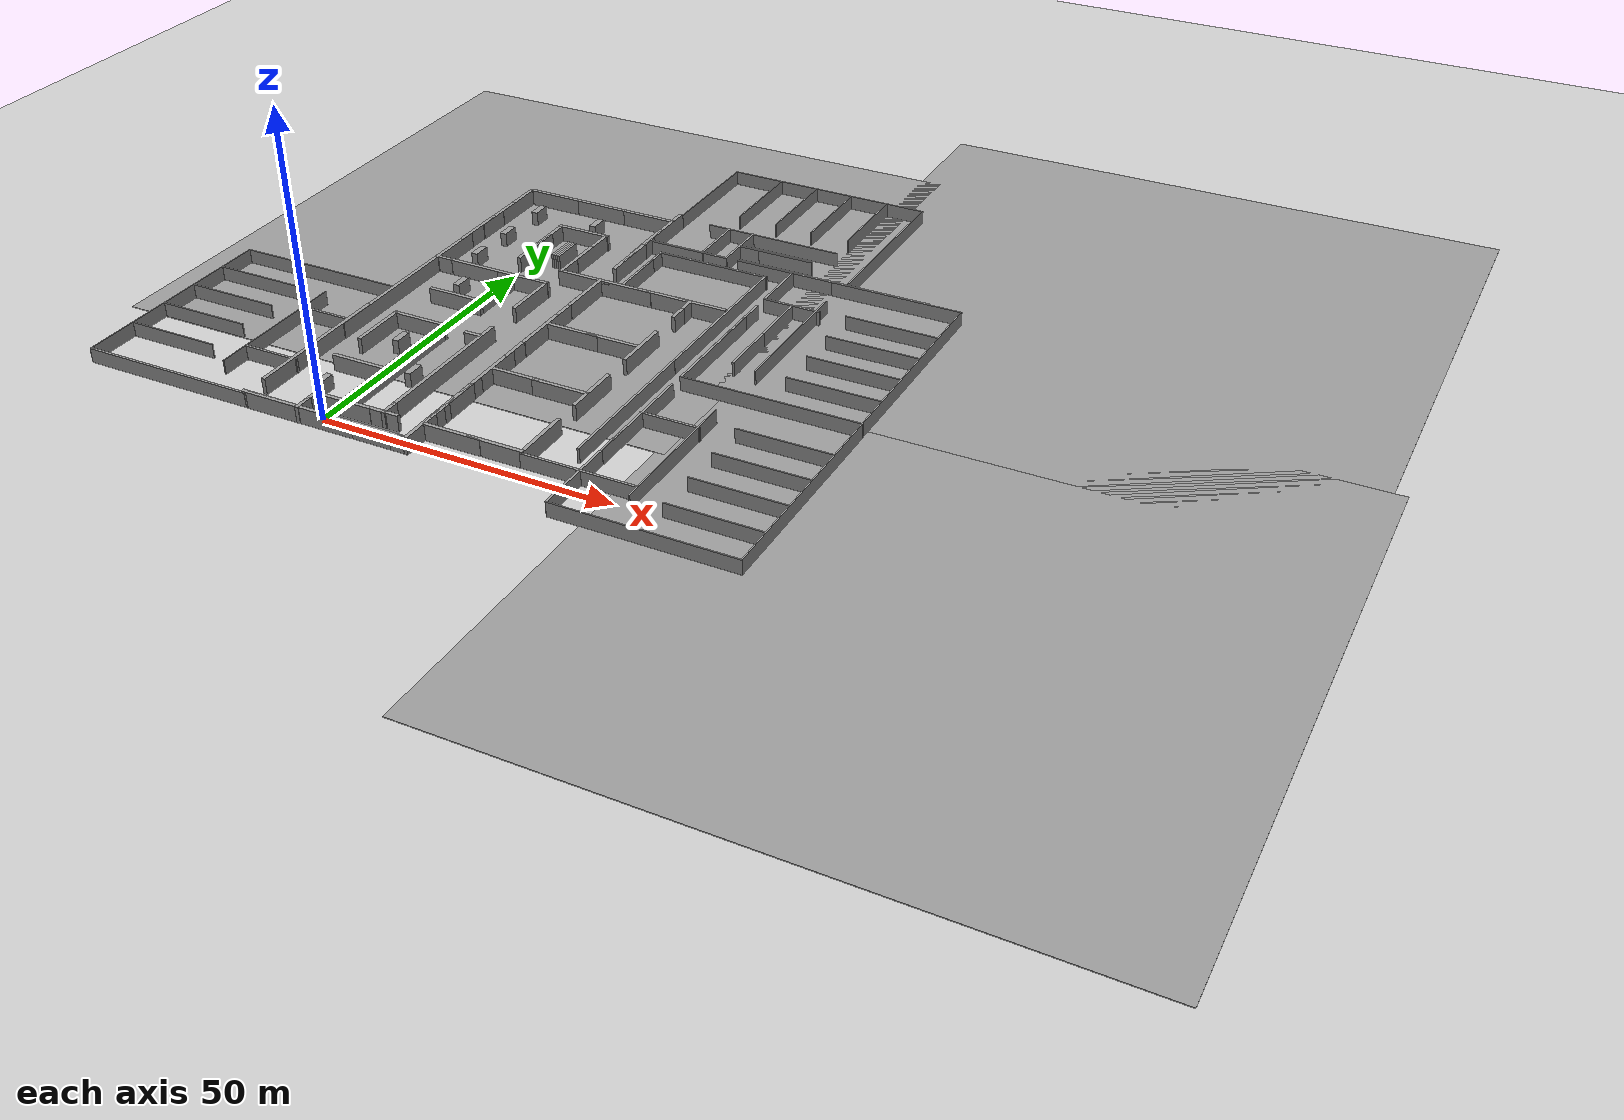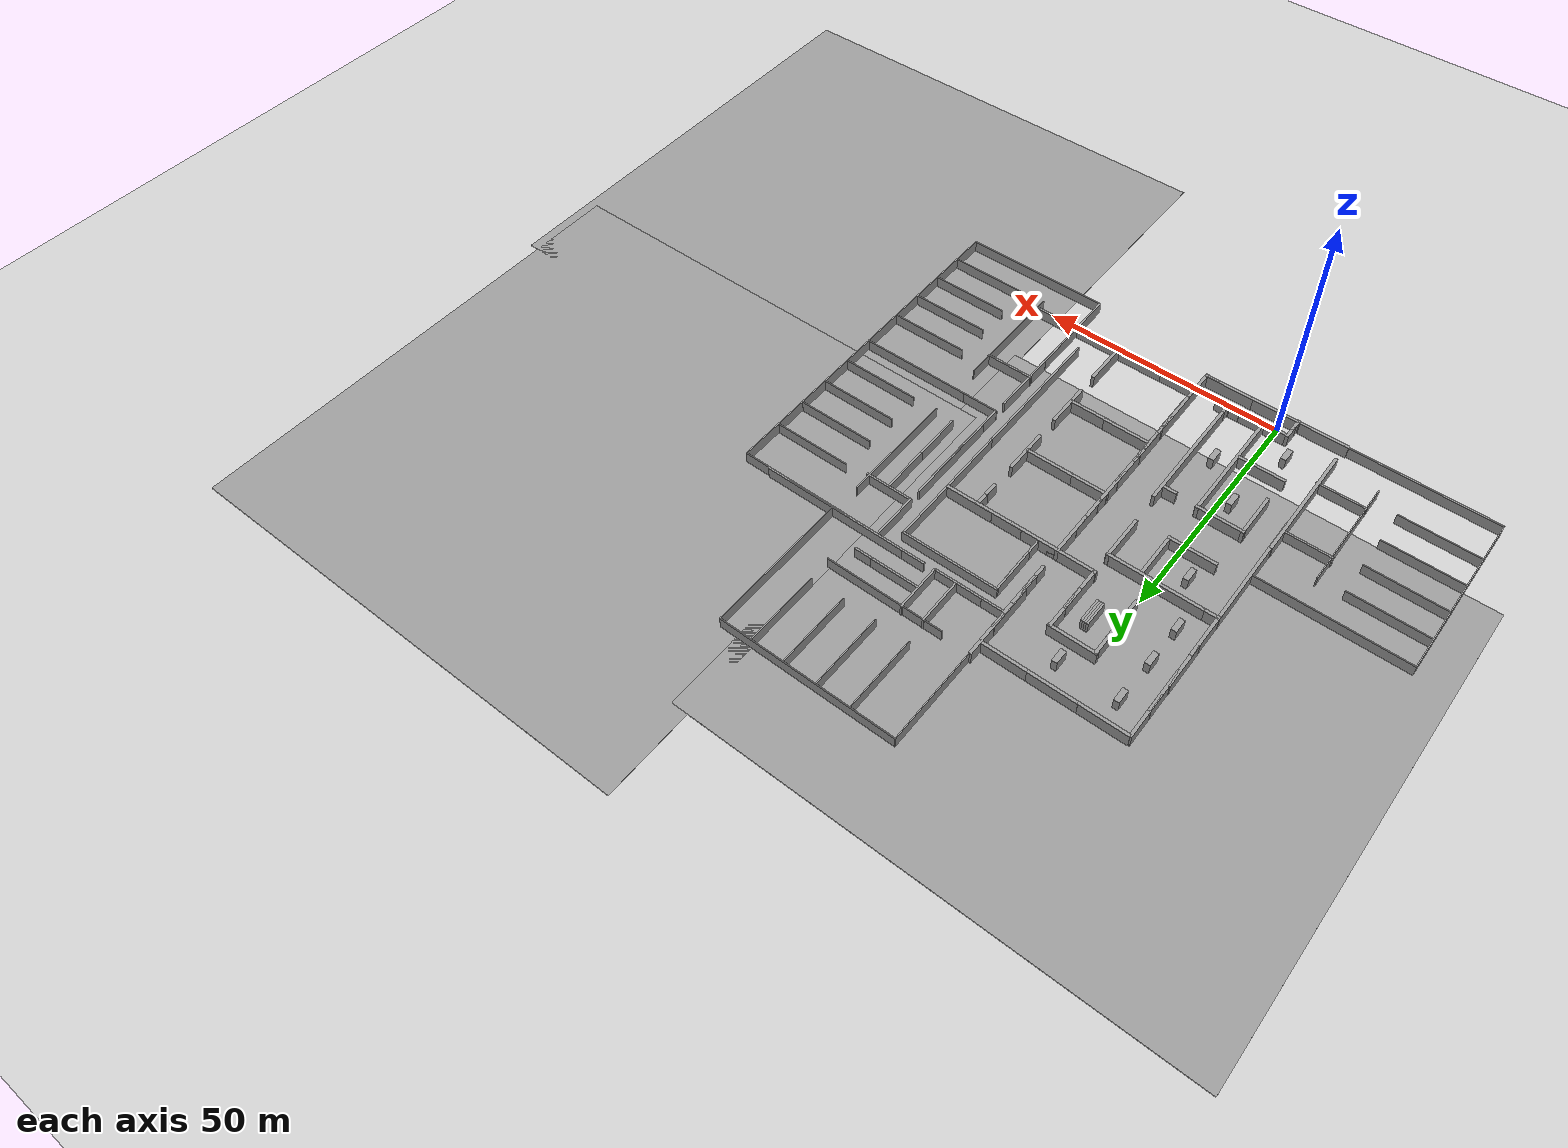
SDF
<sdf version="1.7">
 <world name="default">
  <light name="sun" type="directional">
   <pose>0 0 10 0 -0 0</pose>
   <diffuse>0.8 0.8 0.8 1</diffuse>
   <specular>0.2 0.2 0.2 1</specular>
   <attenuation>
    <range>1000</range>
    <constant>0.9</constant>
    <linear>0.01</linear>
    <quadratic>0.001</quadratic>
   </attenuation>
   <direction>-0.5 0.1 -0.9</direction>
   <spot><inner_angle>0</inner_angle><outer_angle>0</outer_angle><falloff>0</falloff></spot>
  </light>
  <plugin name="ros_interface_plugin" filename="librotors_gazebo_ros_interface_plugin.so"/>
  <model name="ground_plane">
   <static>1</static>
   <link name="link">
    <collision name="collision">
     <geometry><plane><normal>0 0 1</normal><size>100 100</size></plane></geometry>
     <surface><friction><ode><mu>100</mu><mu2>50</mu2></ode></friction></surface>
    </collision>
    <visual name="visual">
     <cast_shadows>0</cast_shadows>
     <geometry><plane><normal>0 0 1</normal><size>100 100</size></plane></geometry>
     <material>
      <script><uri>file://media/materials/scripts/gazebo.material</uri><name>Gazebo/Grey</name></script>
     </material>
    </visual>
   </link>
  </model>
  <gravity>0 0 -9.8</gravity>
  <magnetic_field>6e-06 2.3e-05 -4.2e-05</magnetic_field>
  <atmosphere type="adiabatic"/>
  <physics name="default_physics" default="0" type="ode">
   <max_step_size>0.001</max_step_size>
   <real_time_factor>1</real_time_factor>
   <real_time_update_rate>1000</real_time_update_rate>
  </physics>
  <scene><ambient>0.4 0.4 0.4 1</ambient><background>0.7 0.7 0.7 1</background><shadows>1</shadows></scene>
  <spherical_coordinates>
   <surface_model>EARTH_WGS84</surface_model>
   <latitude_deg>0</latitude_deg>
   <longitude_deg>0</longitude_deg>
   <elevation>0</elevation>
   <heading_deg>0</heading_deg>
  </spherical_coordinates>
  <model name="grey_wall_hou">
   <link name="link">
    <pose>0 0 1.37589 0 -0 0</pose>
    <inertial>
     <inertia><ixx>0</ixx><ixy>0</ixy><ixz>0</ixz><iyy>0</iyy><iyz>0</iyz><izz>0</izz></inertia>
     <mass>0</mass>
    </inertial>
    <visual name="visual">
     <cast_shadows>0</cast_shadows>
     <geometry><box><size>9.82221 0.642976 2.8</size></box></geometry>
     <material>
      <script>
       <uri>model://grey_wall/materials/scripts</uri>
       <uri>model://grey_wall/materials/textures</uri>
       <name>vrc/grey_wall</name>
      </script>
      <shader type="pixel"><normal_map>__default__</normal_map></shader>
      <ambient>1 1 1 1</ambient>
      <diffuse>1 1 1 1</diffuse>
      <specular>0 0 0 1</specular>
      <emissive>0 0 0 1</emissive>
     </material>
    </visual>
    <collision name="collision">
     <geometry><box><size>9.82221 0.642976 2.8</size></box></geometry>
     <surface>
      <friction>
       <ode><mu>1</mu><mu2>1</mu2><fdir1>0 0 0</fdir1><slip1>0</slip1><slip2>0</slip2></ode>
       <torsional>
        <coefficient>1</coefficient>
        <patch_radius>0</patch_radius>
        <surface_radius>0</surface_radius>
        <use_patch_radius>1</use_patch_radius>
        <ode><slip>0</slip></ode>
       </torsional>
      </friction>
      <bounce><restitution_coefficient>0</restitution_coefficient><threshold>1e+06</threshold></bounce>
      <contact>
       <collide_without_contact>0</collide_without_contact>
       <collide_without_contact_bitmask>1</collide_without_contact_bitmask>
       <collide_bitmask>1</collide_bitmask>
       <ode>
        <soft_cfm>0</soft_cfm>
        <soft_erp>0.2</soft_erp>
        <kp>1e+13</kp>
        <kd>1</kd>
        <max_vel>0.01</max_vel>
        <min_depth>0</min_depth>
       </ode>
       <bullet>
        <split_impulse>1</split_impulse>
        <split_impulse_penetration_threshold>-0.01</split_impulse_penetration_threshold>
        <soft_cfm>0</soft_cfm>
        <soft_erp>0.2</soft_erp>
        <kp>1e+13</kp>
        <kd>1</kd>
       </bullet>
      </contact>
     </surface>
    </collision>
   </link>
   <static>1</static>
   <pose>2.05548 -1.91312 0 0 -0 0</pose>
  </model>
  <model name="grey_wall_hou_clone_clone">
   <link name="link">
    <pose>0 0 1.37589 0 -0 0</pose>
    <inertial>
     <inertia><ixx>0</ixx><ixy>0</ixy><ixz>0</ixz><iyy>0</iyy><iyz>0</iyz><izz>0</izz></inertia>
     <mass>0</mass>
    </inertial>
    <visual name="visual">
     <cast_shadows>0</cast_shadows>
     <geometry><box><size>9.82221 0.642976 2.8</size></box></geometry>
     <material>
      <script>
       <uri>model://grey_wall/materials/scripts</uri>
       <uri>model://grey_wall/materials/textures</uri>
       <name>vrc/grey_wall</name>
      </script>
      <shader type="pixel"><normal_map>__default__</normal_map></shader>
      <ambient>1 1 1 1</ambient>
      <diffuse>1 1 1 1</diffuse>
      <specular>0 0 0 1</specular>
      <emissive>0 0 0 1</emissive>
     </material>
    </visual>
    <collision name="collision">
     <geometry><box><size>9.82221 0.642976 2.8</size></box></geometry>
     <surface>
      <friction>
       <ode><mu>1</mu><mu2>1</mu2><fdir1>0 0 0</fdir1><slip1>0</slip1><slip2>0</slip2></ode>
       <torsional>
        <coefficient>1</coefficient>
        <patch_radius>0</patch_radius>
        <surface_radius>0</surface_radius>
        <use_patch_radius>1</use_patch_radius>
        <ode><slip>0</slip></ode>
       </torsional>
      </friction>
      <bounce><restitution_coefficient>0</restitution_coefficient><threshold>1e+06</threshold></bounce>
      <contact>
       <collide_without_contact>0</collide_without_contact>
       <collide_without_contact_bitmask>1</collide_without_contact_bitmask>
       <collide_bitmask>1</collide_bitmask>
       <ode>
        <soft_cfm>0</soft_cfm>
        <soft_erp>0.2</soft_erp>
        <kp>1e+13</kp>
        <kd>1</kd>
        <max_vel>0.01</max_vel>
        <min_depth>0</min_depth>
       </ode>
       <bullet>
        <split_impulse>1</split_impulse>
        <split_impulse_penetration_threshold>-0.01</split_impulse_penetration_threshold>
        <soft_cfm>0</soft_cfm>
        <soft_erp>0.2</soft_erp>
        <kp>1e+13</kp>
        <kd>1</kd>
       </bullet>
      </contact>
     </surface>
    </collision>
   </link>
   <static>1</static>
   <pose>2.12702 2.37014 0 0 -0 0</pose>
  </model>
  <model name="grey_wall_hou_clone_clone_clone_0">
   <link name="link">
    <pose>0 0 1.37589 0 -0 0</pose>
    <inertial>
     <inertia><ixx>0</ixx><ixy>0</ixy><ixz>0</ixz><iyy>0</iyy><iyz>0</iyz><izz>0</izz></inertia>
     <mass>0</mass>
    </inertial>
    <visual name="visual">
     <cast_shadows>0</cast_shadows>
     <geometry><box><size>9.82221 0.642976 2.8</size></box></geometry>
     <material>
      <script>
       <uri>model://grey_wall/materials/scripts</uri>
       <uri>model://grey_wall/materials/textures</uri>
       <name>vrc/grey_wall</name>
      </script>
      <shader type="pixel"><normal_map>__default__</normal_map></shader>
      <ambient>1 1 1 1</ambient>
      <diffuse>1 1 1 1</diffuse>
      <specular>0 0 0 1</specular>
      <emissive>0 0 0 1</emissive>
     </material>
    </visual>
    <collision name="collision">
     <geometry><box><size>9.82221 0.642976 2.8</size></box></geometry>
     <surface>
      <friction>
       <ode><mu>1</mu><mu2>1</mu2><fdir1>0 0 0</fdir1><slip1>0</slip1><slip2>0</slip2></ode>
       <torsional>
        <coefficient>1</coefficient>
        <patch_radius>0</patch_radius>
        <surface_radius>0</surface_radius>
        <use_patch_radius>1</use_patch_radius>
        <ode><slip>0</slip></ode>
       </torsional>
      </friction>
      <bounce><restitution_coefficient>0</restitution_coefficient><threshold>1e+06</threshold></bounce>
      <contact>
       <collide_without_contact>0</collide_without_contact>
       <collide_without_contact_bitmask>1</collide_without_contact_bitmask>
       <collide_bitmask>1</collide_bitmask>
       <ode>
        <soft_cfm>0</soft_cfm>
        <soft_erp>0.2</soft_erp>
        <kp>1e+13</kp>
        <kd>1</kd>
        <max_vel>0.01</max_vel>
        <min_depth>0</min_depth>
       </ode>
       <bullet>
        <split_impulse>1</split_impulse>
        <split_impulse_penetration_threshold>-0.01</split_impulse_penetration_threshold>
        <soft_cfm>0</soft_cfm>
        <soft_erp>0.2</soft_erp>
        <kp>1e+13</kp>
        <kd>1</kd>
       </bullet>
      </contact>
     </surface>
    </collision>
   </link>
   <static>1</static>
   <pose>11.3798 -1.88767 0 0 -0 0</pose>
  </model>
  <model name="grey_wall_short">
   <link name="link">
    <pose>0 0 1.37589 0 -0 0</pose>
    <inertial>
     <inertia><ixx>0</ixx><ixy>0</ixy><ixz>0</ixz><iyy>0</iyy><iyz>0</iyz><izz>0</izz></inertia>
     <mass>0</mass>
    </inertial>
    <visual name="visual">
     <cast_shadows>0</cast_shadows>
     <geometry><box><size>3.01651 0.642976 2.8</size></box></geometry>
     <material>
      <script>
       <uri>model://grey_wall/materials/scripts</uri>
       <uri>model://grey_wall/materials/textures</uri>
       <name>vrc/grey_wall</name>
      </script>
      <shader type="pixel"><normal_map>__default__</normal_map></shader>
      <ambient>1 1 1 1</ambient>
      <diffuse>1 1 1 1</diffuse>
      <specular>0 0 0 1</specular>
      <emissive>0 0 0 1</emissive>
     </material>
    </visual>
    <collision name="collision">
     <geometry><box><size>3.01651 0.642976 2.8</size></box></geometry>
     <surface>
      <friction>
       <ode><mu>1</mu><mu2>1</mu2><fdir1>0 0 0</fdir1><slip1>0</slip1><slip2>0</slip2></ode>
       <torsional>
        <coefficient>1</coefficient>
        <patch_radius>0</patch_radius>
        <surface_radius>0</surface_radius>
        <use_patch_radius>1</use_patch_radius>
        <ode><slip>0</slip></ode>
       </torsional>
      </friction>
      <bounce><restitution_coefficient>0</restitution_coefficient><threshold>1e+06</threshold></bounce>
      <contact>
       <collide_without_contact>0</collide_without_contact>
       <collide_without_contact_bitmask>1</collide_without_contact_bitmask>
       <collide_bitmask>1</collide_bitmask>
       <ode>
        <soft_cfm>0</soft_cfm>
        <soft_erp>0.2</soft_erp>
        <kp>1e+13</kp>
        <kd>1</kd>
        <max_vel>0.01</max_vel>
        <min_depth>0</min_depth>
       </ode>
       <bullet>
        <split_impulse>1</split_impulse>
        <split_impulse_penetration_threshold>-0.01</split_impulse_penetration_threshold>
        <soft_cfm>0</soft_cfm>
        <soft_erp>0.2</soft_erp>
        <kp>1e+13</kp>
        <kd>1</kd>
       </bullet>
      </contact>
     </surface>
    </collision>
   </link>
   <static>1</static>
   <pose>8.42725 2.39613 0 0 -0 0</pose>
  </model>
  <model name="grey_wall_short_clone">
   <link name="link">
    <pose>0 0 1.37589 0 -0 0</pose>
    <inertial>
     <inertia><ixx>0</ixx><ixy>0</ixy><ixz>0</ixz><iyy>0</iyy><iyz>0</iyz><izz>0</izz></inertia>
     <mass>0</mass>
    </inertial>
    <visual name="visual">
     <cast_shadows>0</cast_shadows>
     <geometry><box><size>3.01651 0.642976 2.8</size></box></geometry>
     <material>
      <script>
       <uri>model://grey_wall/materials/scripts</uri>
       <uri>model://grey_wall/materials/textures</uri>
       <name>vrc/grey_wall</name>
      </script>
      <shader type="pixel"><normal_map>__default__</normal_map></shader>
      <ambient>1 1 1 1</ambient>
      <diffuse>1 1 1 1</diffuse>
      <specular>0 0 0 1</specular>
      <emissive>0 0 0 1</emissive>
     </material>
    </visual>
    <collision name="collision">
     <geometry><box><size>3.01651 0.642976 2.8</size></box></geometry>
     <surface>
      <friction>
       <ode><mu>1</mu><mu2>1</mu2><fdir1>0 0 0</fdir1><slip1>0</slip1><slip2>0</slip2></ode>
       <torsional>
        <coefficient>1</coefficient>
        <patch_radius>0</patch_radius>
        <surface_radius>0</surface_radius>
        <use_patch_radius>1</use_patch_radius>
        <ode><slip>0</slip></ode>
       </torsional>
      </friction>
      <bounce><restitution_coefficient>0</restitution_coefficient><threshold>1e+06</threshold></bounce>
      <contact>
       <collide_without_contact>0</collide_without_contact>
       <collide_without_contact_bitmask>1</collide_without_contact_bitmask>
       <collide_bitmask>1</collide_bitmask>
       <ode>
        <soft_cfm>0</soft_cfm>
        <soft_erp>0.2</soft_erp>
        <kp>1e+13</kp>
        <kd>1</kd>
        <max_vel>0.01</max_vel>
        <min_depth>0</min_depth>
       </ode>
       <bullet>
        <split_impulse>1</split_impulse>
        <split_impulse_penetration_threshold>-0.01</split_impulse_penetration_threshold>
        <soft_cfm>0</soft_cfm>
        <soft_erp>0.2</soft_erp>
        <kp>1e+13</kp>
        <kd>1</kd>
       </bullet>
      </contact>
     </surface>
    </collision>
   </link>
   <static>1</static>
   <pose>7.84417 27.1476 0 0 -0 0</pose>
  </model>
  <model name="ground_plane_0">
   <static>1</static>
   <link name="link">
    <collision name="collision">
     <geometry><plane><normal>0 0 1</normal><size>100 100</size></plane></geometry>
     <surface>
      <contact><collide_bitmask>65535</collide_bitmask></contact>
      <friction><ode><mu>100</mu><mu2>50</mu2></ode></friction>
     </surface>
    </collision>
    <visual name="visual">
     <cast_shadows>0</cast_shadows>
     <geometry><plane><normal>0 0 1</normal><size>100 100</size></plane></geometry>
     <material>
      <script><uri>file://media/materials/scripts/gazebo.material</uri><name>Gazebo/Grey</name></script>
     </material>
    </visual>
   </link>
   <pose>98.3802 0.128223 0 0 -0 0</pose>
  </model>
  <model name="ground_plane_1">
   <static>1</static>
   <link name="link">
    <collision name="collision">
     <geometry><plane><normal>0 0 1</normal><size>100 100</size></plane></geometry>
     <surface>
      <contact><collide_bitmask>65535</collide_bitmask></contact>
      <friction><ode><mu>100</mu><mu2>50</mu2></ode></friction>
     </surface>
    </collision>
    <visual name="visual">
     <cast_shadows>0</cast_shadows>
     <geometry><plane><normal>0 0 1</normal><size>100 100</size></plane></geometry>
     <material>
      <script><uri>file://media/materials/scripts/gazebo.material</uri><name>Gazebo/Grey</name></script>
     </material>
    </visual>
   </link>
   <pose>-0.115157 63.9735 0 0 -0 0</pose>
  </model>
  <model name="ground_plane_2">
   <static>1</static>
   <link name="link">
    <collision name="collision">
     <geometry><plane><normal>0 0 1</normal><size>100 100</size></plane></geometry>
     <surface>
      <contact><collide_bitmask>65535</collide_bitmask></contact>
      <friction><ode><mu>100</mu><mu2>50</mu2></ode></friction>
     </surface>
    </collision>
    <visual name="visual">
     <cast_shadows>0</cast_shadows>
     <geometry><plane><normal>0 0 1</normal><size>100 100</size></plane></geometry>
     <material>
      <script><uri>file://media/materials/scripts/gazebo.material</uri><name>Gazebo/Grey</name></script>
     </material>
    </visual>
   </link>
   <pose>96.4085 82.3703 0 0 -0 0</pose>
  </model>
  <model name="grey_wall_hou_clone_clone_clone_5">
   <link name="link">
    <pose>0 0 1.37589 0 -0 0</pose>
    <inertial>
     <inertia><ixx>0</ixx><ixy>0</ixy><ixz>0</ixz><iyy>0</iyy><iyz>0</iyz><izz>0</izz></inertia>
     <mass>0</mass>
    </inertial>
    <visual name="visual">
     <cast_shadows>0</cast_shadows>
     <geometry><box><size>9.82221 0.642976 2.8</size></box></geometry>
     <material>
      <script>
       <uri>model://grey_wall/materials/scripts</uri>
       <uri>model://grey_wall/materials/textures</uri>
       <name>vrc/grey_wall</name>
      </script>
      <shader type="pixel"><normal_map>__default__</normal_map></shader>
      <ambient>1 1 1 1</ambient>
      <diffuse>1 1 1 1</diffuse>
      <specular>0 0 0 1</specular>
      <emissive>0 0 0 1</emissive>
     </material>
    </visual>
    <collision name="collision">
     <geometry><box><size>9.82221 0.642976 2.8</size></box></geometry>
     <surface>
      <friction>
       <ode><mu>1</mu><mu2>1</mu2><fdir1>0 0 0</fdir1><slip1>0</slip1><slip2>0</slip2></ode>
       <torsional>
        <coefficient>1</coefficient>
        <patch_radius>0</patch_radius>
        <surface_radius>0</surface_radius>
        <use_patch_radius>1</use_patch_radius>
        <ode><slip>0</slip></ode>
       </torsional>
      </friction>
      <bounce><restitution_coefficient>0</restitution_coefficient><threshold>1e+06</threshold></bounce>
      <contact>
       <collide_without_contact>0</collide_without_contact>
       <collide_without_contact_bitmask>1</collide_without_contact_bitmask>
       <collide_bitmask>1</collide_bitmask>
       <ode>
        <soft_cfm>0</soft_cfm>
        <soft_erp>0.2</soft_erp>
        <kp>1e+13</kp>
        <kd>1</kd>
        <max_vel>0.01</max_vel>
        <min_depth>0</min_depth>
       </ode>
       <bullet>
        <split_impulse>1</split_impulse>
        <split_impulse_penetration_threshold>-0.01</split_impulse_penetration_threshold>
        <soft_cfm>0</soft_cfm>
        <soft_erp>0.2</soft_erp>
        <kp>1e+13</kp>
        <kd>1</kd>
       </bullet>
      </contact>
     </surface>
    </collision>
   </link>
   <static>1</static>
   <pose>21.5273 2.36287 0 0 -0 0</pose>
  </model>
  <model name="grey_wall_hou_clone_clone_3_clone_4">
   <link name="link">
    <pose>0 0 1.37589 0 -0 0</pose>
    <inertial>
     <inertia><ixx>0</ixx><ixy>0</ixy><ixz>0</ixz><iyy>0</iyy><iyz>0</iyz><izz>0</izz></inertia>
     <mass>0</mass>
    </inertial>
    <visual name="visual">
     <cast_shadows>0</cast_shadows>
     <geometry><box><size>9.82221 0.642976 2.8</size></box></geometry>
     <material>
      <script>
       <uri>model://grey_wall/materials/scripts</uri>
       <uri>model://grey_wall/materials/textures</uri>
       <name>vrc/grey_wall</name>
      </script>
      <shader type="pixel"><normal_map>__default__</normal_map></shader>
      <ambient>1 1 1 1</ambient>
      <diffuse>1 1 1 1</diffuse>
      <specular>0 0 0 1</specular>
      <emissive>0 0 0 1</emissive>
     </material>
    </visual>
    <collision name="collision">
     <geometry><box><size>9.82221 0.642976 2.8</size></box></geometry>
     <surface>
      <friction>
       <ode><mu>1</mu><mu2>1</mu2><fdir1>0 0 0</fdir1><slip1>0</slip1><slip2>0</slip2></ode>
       <torsional>
        <coefficient>1</coefficient>
        <patch_radius>0</patch_radius>
        <surface_radius>0</surface_radius>
        <use_patch_radius>1</use_patch_radius>
        <ode><slip>0</slip></ode>
       </torsional>
      </friction>
      <bounce><restitution_coefficient>0</restitution_coefficient><threshold>1e+06</threshold></bounce>
      <contact>
       <collide_without_contact>0</collide_without_contact>
       <collide_without_contact_bitmask>1</collide_without_contact_bitmask>
       <collide_bitmask>1</collide_bitmask>
       <ode>
        <soft_cfm>0</soft_cfm>
        <soft_erp>0.2</soft_erp>
        <kp>1e+13</kp>
        <kd>1</kd>
        <max_vel>0.01</max_vel>
        <min_depth>0</min_depth>
       </ode>
       <bullet>
        <split_impulse>1</split_impulse>
        <split_impulse_penetration_threshold>-0.01</split_impulse_penetration_threshold>
        <soft_cfm>0</soft_cfm>
        <soft_erp>0.2</soft_erp>
        <kp>1e+13</kp>
        <kd>1</kd>
       </bullet>
      </contact>
     </surface>
    </collision>
   </link>
   <static>1</static>
   <pose>16.3936 20.4757 0 0 0 -1.56855</pose>
  </model>
  <model name="grey_wall_hou_clone_clone_3_clone_0_clone_1">
   <link name="link">
    <pose>0 0 1.37589 0 -0 0</pose>
    <inertial>
     <inertia><ixx>0</ixx><ixy>0</ixy><ixz>0</ixz><iyy>0</iyy><iyz>0</iyz><izz>0</izz></inertia>
     <mass>0</mass>
    </inertial>
    <visual name="visual">
     <cast_shadows>0</cast_shadows>
     <geometry><box><size>9.82221 0.642976 2.8</size></box></geometry>
     <material>
      <script>
       <uri>model://grey_wall/materials/scripts</uri>
       <uri>model://grey_wall/materials/textures</uri>
       <name>vrc/grey_wall</name>
      </script>
      <shader type="pixel"><normal_map>__default__</normal_map></shader>
      <ambient>1 1 1 1</ambient>
      <diffuse>1 1 1 1</diffuse>
      <specular>0 0 0 1</specular>
      <emissive>0 0 0 1</emissive>
     </material>
    </visual>
    <collision name="collision">
     <geometry><box><size>9.82221 0.642976 2.8</size></box></geometry>
     <surface>
      <friction>
       <ode><mu>1</mu><mu2>1</mu2><fdir1>0 0 0</fdir1><slip1>0</slip1><slip2>0</slip2></ode>
       <torsional>
        <coefficient>1</coefficient>
        <patch_radius>0</patch_radius>
        <surface_radius>0</surface_radius>
        <use_patch_radius>1</use_patch_radius>
        <ode><slip>0</slip></ode>
       </torsional>
      </friction>
      <bounce><restitution_coefficient>0</restitution_coefficient><threshold>1e+06</threshold></bounce>
      <contact>
       <collide_without_contact>0</collide_without_contact>
       <collide_without_contact_bitmask>1</collide_without_contact_bitmask>
       <collide_bitmask>1</collide_bitmask>
       <ode>
        <soft_cfm>0</soft_cfm>
        <soft_erp>0.2</soft_erp>
        <kp>1e+13</kp>
        <kd>1</kd>
        <max_vel>0.01</max_vel>
        <min_depth>0</min_depth>
       </ode>
       <bullet>
        <split_impulse>1</split_impulse>
        <split_impulse_penetration_threshold>-0.01</split_impulse_penetration_threshold>
        <soft_cfm>0</soft_cfm>
        <soft_erp>0.2</soft_erp>
        <kp>1e+13</kp>
        <kd>1</kd>
       </bullet>
      </contact>
     </surface>
    </collision>
   </link>
   <static>1</static>
   <pose>33.2826 35.5332 0 0 0 -1.56855</pose>
  </model>
  <model name="grey_wall_hou_clone_clone_clone_6">
   <link name="link">
    <pose>0 0 1.37589 0 -0 0</pose>
    <inertial>
     <inertia><ixx>0</ixx><ixy>0</ixy><ixz>0</ixz><iyy>0</iyy><iyz>0</iyz><izz>0</izz></inertia>
     <mass>0</mass>
    </inertial>
    <visual name="visual">
     <cast_shadows>0</cast_shadows>
     <geometry><box><size>9.82221 0.642976 2.8</size></box></geometry>
     <material>
      <script>
       <uri>model://grey_wall/materials/scripts</uri>
       <uri>model://grey_wall/materials/textures</uri>
       <name>vrc/grey_wall</name>
      </script>
      <shader type="pixel"><normal_map>__default__</normal_map></shader>
      <ambient>1 1 1 1</ambient>
      <diffuse>1 1 1 1</diffuse>
      <specular>0 0 0 1</specular>
      <emissive>0 0 0 1</emissive>
     </material>
    </visual>
    <collision name="collision">
     <geometry><box><size>9.82221 0.642976 2.8</size></box></geometry>
     <surface>
      <friction>
       <ode><mu>1</mu><mu2>1</mu2><fdir1>0 0 0</fdir1><slip1>0</slip1><slip2>0</slip2></ode>
       <torsional>
        <coefficient>1</coefficient>
        <patch_radius>0</patch_radius>
        <surface_radius>0</surface_radius>
        <use_patch_radius>1</use_patch_radius>
        <ode><slip>0</slip></ode>
       </torsional>
      </friction>
      <bounce><restitution_coefficient>0</restitution_coefficient><threshold>1e+06</threshold></bounce>
      <contact>
       <collide_without_contact>0</collide_without_contact>
       <collide_without_contact_bitmask>1</collide_without_contact_bitmask>
       <collide_bitmask>1</collide_bitmask>
       <ode>
        <soft_cfm>0</soft_cfm>
        <soft_erp>0.2</soft_erp>
        <kp>1e+13</kp>
        <kd>1</kd>
        <max_vel>0.01</max_vel>
        <min_depth>0</min_depth>
       </ode>
       <bullet>
        <split_impulse>1</split_impulse>
        <split_impulse_penetration_threshold>-0.01</split_impulse_penetration_threshold>
        <soft_cfm>0</soft_cfm>
        <soft_erp>0.2</soft_erp>
        <kp>1e+13</kp>
        <kd>1</kd>
       </bullet>
      </contact>
     </surface>
    </collision>
   </link>
   <static>1</static>
   <pose>28.8284 2.39593 0 0 -0 0</pose>
  </model>
  <model name="grey_wall_hou_clone_clone_clone_7">
   <link name="link">
    <pose>0 0 1.37589 0 -0 0</pose>
    <inertial>
     <inertia><ixx>0</ixx><ixy>0</ixy><ixz>0</ixz><iyy>0</iyy><iyz>0</iyz><izz>0</izz></inertia>
     <mass>0</mass>
    </inertial>
    <visual name="visual">
     <cast_shadows>0</cast_shadows>
     <geometry><box><size>9.82221 0.642976 2.8</size></box></geometry>
     <material>
      <script>
       <uri>model://grey_wall/materials/scripts</uri>
       <uri>model://grey_wall/materials/textures</uri>
       <name>vrc/grey_wall</name>
      </script>
      <shader type="pixel"><normal_map>__default__</normal_map></shader>
      <ambient>1 1 1 1</ambient>
      <diffuse>1 1 1 1</diffuse>
      <specular>0 0 0 1</specular>
      <emissive>0 0 0 1</emissive>
     </material>
    </visual>
    <collision name="collision">
     <geometry><box><size>9.82221 0.642976 2.8</size></box></geometry>
     <surface>
      <friction>
       <ode><mu>1</mu><mu2>1</mu2><fdir1>0 0 0</fdir1><slip1>0</slip1><slip2>0</slip2></ode>
       <torsional>
        <coefficient>1</coefficient>
        <patch_radius>0</patch_radius>
        <surface_radius>0</surface_radius>
        <use_patch_radius>1</use_patch_radius>
        <ode><slip>0</slip></ode>
       </torsional>
      </friction>
      <bounce><restitution_coefficient>0</restitution_coefficient><threshold>1e+06</threshold></bounce>
      <contact>
       <collide_without_contact>0</collide_without_contact>
       <collide_without_contact_bitmask>1</collide_without_contact_bitmask>
       <collide_bitmask>1</collide_bitmask>
       <ode>
        <soft_cfm>0</soft_cfm>
        <soft_erp>0.2</soft_erp>
        <kp>1e+13</kp>
        <kd>1</kd>
        <max_vel>0.01</max_vel>
        <min_depth>0</min_depth>
       </ode>
       <bullet>
        <split_impulse>1</split_impulse>
        <split_impulse_penetration_threshold>-0.01</split_impulse_penetration_threshold>
        <soft_cfm>0</soft_cfm>
        <soft_erp>0.2</soft_erp>
        <kp>1e+13</kp>
        <kd>1</kd>
       </bullet>
      </contact>
     </surface>
    </collision>
   </link>
   <static>1</static>
   <pose>28.7009 19.7656 0 0 -0 0</pose>
  </model>
  <model name="grey_wall_hou_clone_clone_clone_8">
   <link name="link">
    <pose>0 0 1.37589 0 -0 0</pose>
    <inertial>
     <inertia><ixx>0</ixx><ixy>0</ixy><ixz>0</ixz><iyy>0</iyy><iyz>0</iyz><izz>0</izz></inertia>
     <mass>0</mass>
    </inertial>
    <visual name="visual">
     <cast_shadows>0</cast_shadows>
     <geometry><box><size>9.82221 0.642976 2.8</size></box></geometry>
     <material>
      <script>
       <uri>model://grey_wall/materials/scripts</uri>
       <uri>model://grey_wall/materials/textures</uri>
       <name>vrc/grey_wall</name>
      </script>
      <shader type="pixel"><normal_map>__default__</normal_map></shader>
      <ambient>1 1 1 1</ambient>
      <diffuse>1 1 1 1</diffuse>
      <specular>0 0 0 1</specular>
      <emissive>0 0 0 1</emissive>
     </material>
    </visual>
    <collision name="collision">
     <geometry><box><size>9.82221 0.642976 2.8</size></box></geometry>
     <surface>
      <friction>
       <ode><mu>1</mu><mu2>1</mu2><fdir1>0 0 0</fdir1><slip1>0</slip1><slip2>0</slip2></ode>
       <torsional>
        <coefficient>1</coefficient>
        <patch_radius>0</patch_radius>
        <surface_radius>0</surface_radius>
        <use_patch_radius>1</use_patch_radius>
        <ode><slip>0</slip></ode>
       </torsional>
      </friction>
      <bounce><restitution_coefficient>0</restitution_coefficient><threshold>1e+06</threshold></bounce>
      <contact>
       <collide_without_contact>0</collide_without_contact>
       <collide_without_contact_bitmask>1</collide_without_contact_bitmask>
       <collide_bitmask>1</collide_bitmask>
       <ode>
        <soft_cfm>0</soft_cfm>
        <soft_erp>0.2</soft_erp>
        <kp>1e+13</kp>
        <kd>1</kd>
        <max_vel>0.01</max_vel>
        <min_depth>0</min_depth>
       </ode>
       <bullet>
        <split_impulse>1</split_impulse>
        <split_impulse_penetration_threshold>-0.01</split_impulse_penetration_threshold>
        <soft_cfm>0</soft_cfm>
        <soft_erp>0.2</soft_erp>
        <kp>1e+13</kp>
        <kd>1</kd>
       </bullet>
      </contact>
     </surface>
    </collision>
   </link>
   <static>1</static>
   <pose>21.1249 19.8433 0 0 -0 0</pose>
  </model>
  <model name="grey_wall_hou_clone_clone_clone_9">
   <link name="link">
    <pose>0 0 1.37589 0 -0 0</pose>
    <inertial>
     <inertia><ixx>0</ixx><ixy>0</ixy><ixz>0</ixz><iyy>0</iyy><iyz>0</iyz><izz>0</izz></inertia>
     <mass>0</mass>
    </inertial>
    <visual name="visual">
     <cast_shadows>0</cast_shadows>
     <geometry><box><size>9.82221 0.642976 2.8</size></box></geometry>
     <material>
      <script>
       <uri>model://grey_wall/materials/scripts</uri>
       <uri>model://grey_wall/materials/textures</uri>
       <name>vrc/grey_wall</name>
      </script>
      <shader type="pixel"><normal_map>__default__</normal_map></shader>
      <ambient>1 1 1 1</ambient>
      <diffuse>1 1 1 1</diffuse>
      <specular>0 0 0 1</specular>
      <emissive>0 0 0 1</emissive>
     </material>
    </visual>
    <collision name="collision">
     <geometry><box><size>9.82221 0.642976 2.8</size></box></geometry>
     <surface>
      <friction>
       <ode><mu>1</mu><mu2>1</mu2><fdir1>0 0 0</fdir1><slip1>0</slip1><slip2>0</slip2></ode>
       <torsional>
        <coefficient>1</coefficient>
        <patch_radius>0</patch_radius>
        <surface_radius>0</surface_radius>
        <use_patch_radius>1</use_patch_radius>
        <ode><slip>0</slip></ode>
       </torsional>
      </friction>
      <bounce><restitution_coefficient>0</restitution_coefficient><threshold>1e+06</threshold></bounce>
      <contact>
       <collide_without_contact>0</collide_without_contact>
       <collide_without_contact_bitmask>1</collide_without_contact_bitmask>
       <collide_bitmask>1</collide_bitmask>
       <ode>
        <soft_cfm>0</soft_cfm>
        <soft_erp>0.2</soft_erp>
        <kp>1e+13</kp>
        <kd>1</kd>
        <max_vel>0.01</max_vel>
        <min_depth>0</min_depth>
       </ode>
       <bullet>
        <split_impulse>1</split_impulse>
        <split_impulse_penetration_threshold>-0.01</split_impulse_penetration_threshold>
        <soft_cfm>0</soft_cfm>
        <soft_erp>0.2</soft_erp>
        <kp>1e+13</kp>
        <kd>1</kd>
       </bullet>
      </contact>
     </surface>
    </collision>
   </link>
   <static>1</static>
   <pose>20.8801 35.0651 0 0 -0 0</pose>
  </model>
  <model name="grey_wall_hou_clone_clone_clone_10">
   <link name="link">
    <pose>0 0 1.37589 0 -0 0</pose>
    <inertial>
     <inertia><ixx>0</ixx><ixy>0</ixy><ixz>0</ixz><iyy>0</iyy><iyz>0</iyz><izz>0</izz></inertia>
     <mass>0</mass>
    </inertial>
    <visual name="visual">
     <cast_shadows>0</cast_shadows>
     <geometry><box><size>9.82221 0.642976 2.8</size></box></geometry>
     <material>
      <script>
       <uri>model://grey_wall/materials/scripts</uri>
       <uri>model://grey_wall/materials/textures</uri>
       <name>vrc/grey_wall</name>
      </script>
      <shader type="pixel"><normal_map>__default__</normal_map></shader>
      <ambient>1 1 1 1</ambient>
      <diffuse>1 1 1 1</diffuse>
      <specular>0 0 0 1</specular>
      <emissive>0 0 0 1</emissive>
     </material>
    </visual>
    <collision name="collision">
     <geometry><box><size>9.82221 0.642976 2.8</size></box></geometry>
     <surface>
      <friction>
       <ode><mu>1</mu><mu2>1</mu2><fdir1>0 0 0</fdir1><slip1>0</slip1><slip2>0</slip2></ode>
       <torsional>
        <coefficient>1</coefficient>
        <patch_radius>0</patch_radius>
        <surface_radius>0</surface_radius>
        <use_patch_radius>1</use_patch_radius>
        <ode><slip>0</slip></ode>
       </torsional>
      </friction>
      <bounce><restitution_coefficient>0</restitution_coefficient><threshold>1e+06</threshold></bounce>
      <contact>
       <collide_without_contact>0</collide_without_contact>
       <collide_without_contact_bitmask>1</collide_without_contact_bitmask>
       <collide_bitmask>1</collide_bitmask>
       <ode>
        <soft_cfm>0</soft_cfm>
        <soft_erp>0.2</soft_erp>
        <kp>1e+13</kp>
        <kd>1</kd>
        <max_vel>0.01</max_vel>
        <min_depth>0</min_depth>
       </ode>
       <bullet>
        <split_impulse>1</split_impulse>
        <split_impulse_penetration_threshold>-0.01</split_impulse_penetration_threshold>
        <soft_cfm>0</soft_cfm>
        <soft_erp>0.2</soft_erp>
        <kp>1e+13</kp>
        <kd>1</kd>
       </bullet>
      </contact>
     </surface>
    </collision>
   </link>
   <static>1</static>
   <pose>28.4204 35.0767 0 0 -0 0</pose>
  </model>
  <model name="grey_wall_hou_clone_clone_3_clone_0_clone_1_clone">
   <link name="link">
    <pose>0 0 1.37589 0 -0 0</pose>
    <inertial>
     <inertia><ixx>0</ixx><ixy>0</ixy><ixz>0</ixz><iyy>0</iyy><iyz>0</iyz><izz>0</izz></inertia>
     <mass>0</mass>
    </inertial>
    <visual name="visual">
     <cast_shadows>0</cast_shadows>
     <geometry><box><size>9.82221 0.642976 2.8</size></box></geometry>
     <material>
      <script>
       <uri>model://grey_wall/materials/scripts</uri>
       <uri>model://grey_wall/materials/textures</uri>
       <name>vrc/grey_wall</name>
      </script>
      <shader type="pixel"><normal_map>__default__</normal_map></shader>
      <ambient>1 1 1 1</ambient>
      <diffuse>1 1 1 1</diffuse>
      <specular>0 0 0 1</specular>
      <emissive>0 0 0 1</emissive>
     </material>
    </visual>
    <collision name="collision">
     <geometry><box><size>9.82221 0.642976 2.8</size></box></geometry>
     <surface>
      <friction>
       <ode><mu>1</mu><mu2>1</mu2><fdir1>0 0 0</fdir1><slip1>0</slip1><slip2>0</slip2></ode>
       <torsional>
        <coefficient>1</coefficient>
        <patch_radius>0</patch_radius>
        <surface_radius>0</surface_radius>
        <use_patch_radius>1</use_patch_radius>
        <ode><slip>0</slip></ode>
       </torsional>
      </friction>
      <bounce><restitution_coefficient>0</restitution_coefficient><threshold>1e+06</threshold></bounce>
      <contact>
       <collide_without_contact>0</collide_without_contact>
       <collide_without_contact_bitmask>1</collide_without_contact_bitmask>
       <collide_bitmask>1</collide_bitmask>
       <ode>
        <soft_cfm>0</soft_cfm>
        <soft_erp>0.2</soft_erp>
        <kp>1e+13</kp>
        <kd>1</kd>
        <max_vel>0.01</max_vel>
        <min_depth>0</min_depth>
       </ode>
       <bullet>
        <split_impulse>1</split_impulse>
        <split_impulse_penetration_threshold>-0.01</split_impulse_penetration_threshold>
        <soft_cfm>0</soft_cfm>
        <soft_erp>0.2</soft_erp>
        <kp>1e+13</kp>
        <kd>1</kd>
       </bullet>
      </contact>
     </surface>
    </collision>
   </link>
   <static>1</static>
   <pose>-0.06228 60.209 0 0 0 -1.56855</pose>
  </model>
  <model name="grey_wall_hou_clone_clone_3_clone_0_clone_1_clone_0">
   <link name="link">
    <pose>0 0 1.37589 0 -0 0</pose>
    <inertial>
     <inertia><ixx>0</ixx><ixy>0</ixy><ixz>0</ixz><iyy>0</iyy><iyz>0</iyz><izz>0</izz></inertia>
     <mass>0</mass>
    </inertial>
    <visual name="visual">
     <cast_shadows>0</cast_shadows>
     <geometry><box><size>9.82221 0.642976 2.8</size></box></geometry>
     <material>
      <script>
       <uri>model://grey_wall/materials/scripts</uri>
       <uri>model://grey_wall/materials/textures</uri>
       <name>vrc/grey_wall</name>
      </script>
      <shader type="pixel"><normal_map>__default__</normal_map></shader>
      <ambient>1 1 1 1</ambient>
      <diffuse>1 1 1 1</diffuse>
      <specular>0 0 0 1</specular>
      <emissive>0 0 0 1</emissive>
     </material>
    </visual>
    <collision name="collision">
     <geometry><box><size>9.82221 0.642976 2.8</size></box></geometry>
     <surface>
      <friction>
       <ode><mu>1</mu><mu2>1</mu2><fdir1>0 0 0</fdir1><slip1>0</slip1><slip2>0</slip2></ode>
       <torsional>
        <coefficient>1</coefficient>
        <patch_radius>0</patch_radius>
        <surface_radius>0</surface_radius>
        <use_patch_radius>1</use_patch_radius>
        <ode><slip>0</slip></ode>
       </torsional>
      </friction>
      <bounce><restitution_coefficient>0</restitution_coefficient><threshold>1e+06</threshold></bounce>
      <contact>
       <collide_without_contact>0</collide_without_contact>
       <collide_without_contact_bitmask>1</collide_without_contact_bitmask>
       <collide_bitmask>1</collide_bitmask>
       <ode>
        <soft_cfm>0</soft_cfm>
        <soft_erp>0.2</soft_erp>
        <kp>1e+13</kp>
        <kd>1</kd>
        <max_vel>0.01</max_vel>
        <min_depth>0</min_depth>
       </ode>
       <bullet>
        <split_impulse>1</split_impulse>
        <split_impulse_penetration_threshold>-0.01</split_impulse_penetration_threshold>
        <soft_cfm>0</soft_cfm>
        <soft_erp>0.2</soft_erp>
        <kp>1e+13</kp>
        <kd>1</kd>
       </bullet>
      </contact>
     </surface>
    </collision>
   </link>
   <static>1</static>
   <pose>16.3465 60.2633 0 0 0 -1.56855</pose>
  </model>
  <model name="grey_wall_hou_clone_clone_3_clone_0_clone_1_clone_2">
   <link name="link">
    <pose>0 0 1.37589 0 -0 0</pose>
    <inertial>
     <inertia><ixx>0</ixx><ixy>0</ixy><ixz>0</ixz><iyy>0</iyy><iyz>0</iyz><izz>0</izz></inertia>
     <mass>0</mass>
    </inertial>
    <visual name="visual">
     <cast_shadows>0</cast_shadows>
     <geometry><box><size>9.82221 0.642976 2.8</size></box></geometry>
     <material>
      <script>
       <uri>model://grey_wall/materials/scripts</uri>
       <uri>model://grey_wall/materials/textures</uri>
       <name>vrc/grey_wall</name>
      </script>
      <shader type="pixel"><normal_map>__default__</normal_map></shader>
      <ambient>1 1 1 1</ambient>
      <diffuse>1 1 1 1</diffuse>
      <specular>0 0 0 1</specular>
      <emissive>0 0 0 1</emissive>
     </material>
    </visual>
    <collision name="collision">
     <geometry><box><size>9.82221 0.642976 2.8</size></box></geometry>
     <surface>
      <friction>
       <ode><mu>1</mu><mu2>1</mu2><fdir1>0 0 0</fdir1><slip1>0</slip1><slip2>0</slip2></ode>
       <torsional>
        <coefficient>1</coefficient>
        <patch_radius>0</patch_radius>
        <surface_radius>0</surface_radius>
        <use_patch_radius>1</use_patch_radius>
        <ode><slip>0</slip></ode>
       </torsional>
      </friction>
      <bounce><restitution_coefficient>0</restitution_coefficient><threshold>1e+06</threshold></bounce>
      <contact>
       <collide_without_contact>0</collide_without_contact>
       <collide_without_contact_bitmask>1</collide_without_contact_bitmask>
       <collide_bitmask>1</collide_bitmask>
       <ode>
        <soft_cfm>0</soft_cfm>
        <soft_erp>0.2</soft_erp>
        <kp>1e+13</kp>
        <kd>1</kd>
        <max_vel>0.01</max_vel>
        <min_depth>0</min_depth>
       </ode>
       <bullet>
        <split_impulse>1</split_impulse>
        <split_impulse_penetration_threshold>-0.01</split_impulse_penetration_threshold>
        <soft_cfm>0</soft_cfm>
        <soft_erp>0.2</soft_erp>
        <kp>1e+13</kp>
        <kd>1</kd>
       </bullet>
      </contact>
     </surface>
    </collision>
   </link>
   <static>1</static>
   <pose>16.3889 46.4515 0 0 0 -1.56855</pose>
  </model>
  <model name="grey_wall_hou_clone_clone_clone_4_clone_clone_0_clone">
   <link name="link">
    <pose>0 0 1.37589 0 -0 0</pose>
    <inertial>
     <inertia><ixx>0</ixx><ixy>0</ixy><ixz>0</ixz><iyy>0</iyy><iyz>0</iyz><izz>0</izz></inertia>
     <mass>0</mass>
    </inertial>
    <visual name="visual">
     <cast_shadows>0</cast_shadows>
     <geometry><box><size>9.82221 0.642976 2.8</size></box></geometry>
     <material>
      <script>
       <uri>model://grey_wall/materials/scripts</uri>
       <uri>model://grey_wall/materials/textures</uri>
       <name>vrc/grey_wall</name>
      </script>
      <shader type="pixel"><normal_map>__default__</normal_map></shader>
      <ambient>1 1 1 1</ambient>
      <diffuse>1 1 1 1</diffuse>
      <specular>0 0 0 1</specular>
      <emissive>0 0 0 1</emissive>
     </material>
    </visual>
    <collision name="collision">
     <geometry><box><size>9.82221 0.642976 2.8</size></box></geometry>
     <surface>
      <friction>
       <ode><mu>1</mu><mu2>1</mu2><fdir1>0 0 0</fdir1><slip1>0</slip1><slip2>0</slip2></ode>
       <torsional>
        <coefficient>1</coefficient>
        <patch_radius>0</patch_radius>
        <surface_radius>0</surface_radius>
        <use_patch_radius>1</use_patch_radius>
        <ode><slip>0</slip></ode>
       </torsional>
      </friction>
      <bounce><restitution_coefficient>0</restitution_coefficient><threshold>1e+06</threshold></bounce>
      <contact>
       <collide_without_contact>0</collide_without_contact>
       <collide_without_contact_bitmask>1</collide_without_contact_bitmask>
       <collide_bitmask>1</collide_bitmask>
       <ode>
        <soft_cfm>0</soft_cfm>
        <soft_erp>0.2</soft_erp>
        <kp>1e+13</kp>
        <kd>1</kd>
        <max_vel>0.01</max_vel>
        <min_depth>0</min_depth>
       </ode>
       <bullet>
        <split_impulse>1</split_impulse>
        <split_impulse_penetration_threshold>-0.01</split_impulse_penetration_threshold>
        <soft_cfm>0</soft_cfm>
        <soft_erp>0.2</soft_erp>
        <kp>1e+13</kp>
        <kd>1</kd>
       </bullet>
      </contact>
     </surface>
    </collision>
   </link>
   <static>1</static>
   <pose>21.103 51.0163 0 0 -0 0</pose>
  </model>
  <model name="grey_wall_hou_clone_clone_clone_4_clone_clone_0_clone_0">
   <link name="link">
    <pose>0 0 1.37589 0 -0 0</pose>
    <inertial>
     <inertia><ixx>0</ixx><ixy>0</ixy><ixz>0</ixz><iyy>0</iyy><iyz>0</iyz><izz>0</izz></inertia>
     <mass>0</mass>
    </inertial>
    <visual name="visual">
     <cast_shadows>0</cast_shadows>
     <geometry><box><size>9.82221 0.642976 2.8</size></box></geometry>
     <material>
      <script>
       <uri>model://grey_wall/materials/scripts</uri>
       <uri>model://grey_wall/materials/textures</uri>
       <name>vrc/grey_wall</name>
      </script>
      <shader type="pixel"><normal_map>__default__</normal_map></shader>
      <ambient>1 1 1 1</ambient>
      <diffuse>1 1 1 1</diffuse>
      <specular>0 0 0 1</specular>
      <emissive>0 0 0 1</emissive>
     </material>
    </visual>
    <collision name="collision">
     <geometry><box><size>9.82221 0.642976 2.8</size></box></geometry>
     <surface>
      <friction>
       <ode><mu>1</mu><mu2>1</mu2><fdir1>0 0 0</fdir1><slip1>0</slip1><slip2>0</slip2></ode>
       <torsional>
        <coefficient>1</coefficient>
        <patch_radius>0</patch_radius>
        <surface_radius>0</surface_radius>
        <use_patch_radius>1</use_patch_radius>
        <ode><slip>0</slip></ode>
       </torsional>
      </friction>
      <bounce><restitution_coefficient>0</restitution_coefficient><threshold>1e+06</threshold></bounce>
      <contact>
       <collide_without_contact>0</collide_without_contact>
       <collide_without_contact_bitmask>1</collide_without_contact_bitmask>
       <collide_bitmask>1</collide_bitmask>
       <ode>
        <soft_cfm>0</soft_cfm>
        <soft_erp>0.2</soft_erp>
        <kp>1e+13</kp>
        <kd>1</kd>
        <max_vel>0.01</max_vel>
        <min_depth>0</min_depth>
       </ode>
       <bullet>
        <split_impulse>1</split_impulse>
        <split_impulse_penetration_threshold>-0.01</split_impulse_penetration_threshold>
        <soft_cfm>0</soft_cfm>
        <soft_erp>0.2</soft_erp>
        <kp>1e+13</kp>
        <kd>1</kd>
       </bullet>
      </contact>
     </surface>
    </collision>
   </link>
   <static>1</static>
   <pose>28.6481 51.0553 0 0 -0 0</pose>
  </model>
  <model name="grey_wall_short_clone_0_clone_clone_clone">
   <link name="link">
    <pose>0 0 1.37589 0 -0 0</pose>
    <inertial>
     <inertia><ixx>0</ixx><ixy>0</ixy><ixz>0</ixz><iyy>0</iyy><iyz>0</iyz><izz>0</izz></inertia>
     <mass>0</mass>
    </inertial>
    <visual name="visual">
     <cast_shadows>0</cast_shadows>
     <geometry><box><size>3.01651 0.642976 2.8</size></box></geometry>
     <material>
      <script>
       <uri>model://grey_wall/materials/scripts</uri>
       <uri>model://grey_wall/materials/textures</uri>
       <name>vrc/grey_wall</name>
      </script>
      <shader type="pixel"><normal_map>__default__</normal_map></shader>
      <ambient>1 1 1 1</ambient>
      <diffuse>1 1 1 1</diffuse>
      <specular>0 0 0 1</specular>
      <emissive>0 0 0 1</emissive>
     </material>
    </visual>
    <collision name="collision">
     <geometry><box><size>3.01651 0.642976 2.8</size></box></geometry>
     <surface>
      <friction>
       <ode><mu>1</mu><mu2>1</mu2><fdir1>0 0 0</fdir1><slip1>0</slip1><slip2>0</slip2></ode>
       <torsional>
        <coefficient>1</coefficient>
        <patch_radius>0</patch_radius>
        <surface_radius>0</surface_radius>
        <use_patch_radius>1</use_patch_radius>
        <ode><slip>0</slip></ode>
       </torsional>
      </friction>
      <bounce><restitution_coefficient>0</restitution_coefficient><threshold>1e+06</threshold></bounce>
      <contact>
       <collide_without_contact>0</collide_without_contact>
       <collide_without_contact_bitmask>1</collide_without_contact_bitmask>
       <collide_bitmask>1</collide_bitmask>
       <ode>
        <soft_cfm>0</soft_cfm>
        <soft_erp>0.2</soft_erp>
        <kp>1e+13</kp>
        <kd>1</kd>
        <max_vel>0.01</max_vel>
        <min_depth>0</min_depth>
       </ode>
       <bullet>
        <split_impulse>1</split_impulse>
        <split_impulse_penetration_threshold>-0.01</split_impulse_penetration_threshold>
        <soft_cfm>0</soft_cfm>
        <soft_erp>0.2</soft_erp>
        <kp>1e+13</kp>
        <kd>1</kd>
       </bullet>
      </contact>
     </surface>
    </collision>
   </link>
   <static>1</static>
   <pose>33.2477 49.8517 0 0 0 -1.57149</pose>
  </model>
  <model name="grey_wall_short_0_clone_1">
   <link name="link">
    <pose>0 0 1.37589 0 -0 0</pose>
    <inertial>
     <inertia><ixx>0</ixx><ixy>0</ixy><ixz>0</ixz><iyy>0</iyy><iyz>0</iyz><izz>0</izz></inertia>
     <mass>0</mass>
    </inertial>
    <visual name="visual">
     <cast_shadows>0</cast_shadows>
     <geometry><box><size>3.01651 0.642976 2.8</size></box></geometry>
     <material>
      <script>
       <uri>model://grey_wall/materials/scripts</uri>
       <uri>model://grey_wall/materials/textures</uri>
       <name>vrc/grey_wall</name>
      </script>
      <shader type="pixel"><normal_map>__default__</normal_map></shader>
      <ambient>1 1 1 1</ambient>
      <diffuse>1 1 1 1</diffuse>
      <specular>0 0 0 1</specular>
      <emissive>0 0 0 1</emissive>
     </material>
    </visual>
    <collision name="collision">
     <geometry><box><size>3.01651 0.642976 2.8</size></box></geometry>
     <surface>
      <friction>
       <ode><mu>1</mu><mu2>1</mu2><fdir1>0 0 0</fdir1><slip1>0</slip1><slip2>0</slip2></ode>
       <torsional>
        <coefficient>1</coefficient>
        <patch_radius>0</patch_radius>
        <surface_radius>0</surface_radius>
        <use_patch_radius>1</use_patch_radius>
        <ode><slip>0</slip></ode>
       </torsional>
      </friction>
      <bounce><restitution_coefficient>0</restitution_coefficient><threshold>1e+06</threshold></bounce>
      <contact>
       <collide_without_contact>0</collide_without_contact>
       <collide_without_contact_bitmask>1</collide_without_contact_bitmask>
       <collide_bitmask>1</collide_bitmask>
       <ode>
        <soft_cfm>0</soft_cfm>
        <soft_erp>0.2</soft_erp>
        <kp>1e+13</kp>
        <kd>1</kd>
        <max_vel>0.01</max_vel>
        <min_depth>0</min_depth>
       </ode>
       <bullet>
        <split_impulse>1</split_impulse>
        <split_impulse_penetration_threshold>-0.01</split_impulse_penetration_threshold>
        <soft_cfm>0</soft_cfm>
        <soft_erp>0.2</soft_erp>
        <kp>1e+13</kp>
        <kd>1</kd>
       </bullet>
      </contact>
     </surface>
    </collision>
   </link>
   <static>1</static>
   <pose>9.47315 3.55431 0 0 0 -1.57204</pose>
  </model>
  <model name="grey_wall_short_0_clone_2">
   <link name="link">
    <pose>0 0 1.37589 0 -0 0</pose>
    <inertial>
     <inertia><ixx>0</ixx><ixy>0</ixy><ixz>0</ixz><iyy>0</iyy><iyz>0</iyz><izz>0</izz></inertia>
     <mass>0</mass>
    </inertial>
    <visual name="visual">
     <cast_shadows>0</cast_shadows>
     <geometry><box><size>3.01651 0.642976 2.8</size></box></geometry>
     <material>
      <script>
       <uri>model://grey_wall/materials/scripts</uri>
       <uri>model://grey_wall/materials/textures</uri>
       <name>vrc/grey_wall</name>
      </script>
      <shader type="pixel"><normal_map>__default__</normal_map></shader>
      <ambient>1 1 1 1</ambient>
      <diffuse>1 1 1 1</diffuse>
      <specular>0 0 0 1</specular>
      <emissive>0 0 0 1</emissive>
     </material>
    </visual>
    <collision name="collision">
     <geometry><box><size>3.01651 0.642976 2.8</size></box></geometry>
     <surface>
      <friction>
       <ode><mu>1</mu><mu2>1</mu2><fdir1>0 0 0</fdir1><slip1>0</slip1><slip2>0</slip2></ode>
       <torsional>
        <coefficient>1</coefficient>
        <patch_radius>0</patch_radius>
        <surface_radius>0</surface_radius>
        <use_patch_radius>1</use_patch_radius>
        <ode><slip>0</slip></ode>
       </torsional>
      </friction>
      <bounce><restitution_coefficient>0</restitution_coefficient><threshold>1e+06</threshold></bounce>
      <contact>
       <collide_without_contact>0</collide_without_contact>
       <collide_without_contact_bitmask>1</collide_without_contact_bitmask>
       <collide_bitmask>1</collide_bitmask>
       <ode>
        <soft_cfm>0</soft_cfm>
        <soft_erp>0.2</soft_erp>
        <kp>1e+13</kp>
        <kd>1</kd>
        <max_vel>0.01</max_vel>
        <min_depth>0</min_depth>
       </ode>
       <bullet>
        <split_impulse>1</split_impulse>
        <split_impulse_penetration_threshold>-0.01</split_impulse_penetration_threshold>
        <soft_cfm>0</soft_cfm>
        <soft_erp>0.2</soft_erp>
        <kp>1e+13</kp>
        <kd>1</kd>
       </bullet>
      </contact>
     </surface>
    </collision>
   </link>
   <static>1</static>
   <pose>16.5494 3.563 0 0 0 -1.57204</pose>
  </model>
  <model name="grey_wall_short_0_clone_3">
   <link name="link">
    <pose>0 0 1.37589 0 -0 0</pose>
    <inertial>
     <inertia><ixx>0</ixx><ixy>0</ixy><ixz>0</ixz><iyy>0</iyy><iyz>0</iyz><izz>0</izz></inertia>
     <mass>0</mass>
    </inertial>
    <visual name="visual">
     <cast_shadows>0</cast_shadows>
     <geometry><box><size>3.01651 0.642976 2.8</size></box></geometry>
     <material>
      <script>
       <uri>model://grey_wall/materials/scripts</uri>
       <uri>model://grey_wall/materials/textures</uri>
       <name>vrc/grey_wall</name>
      </script>
      <shader type="pixel"><normal_map>__default__</normal_map></shader>
      <ambient>1 1 1 1</ambient>
      <diffuse>1 1 1 1</diffuse>
      <specular>0 0 0 1</specular>
      <emissive>0 0 0 1</emissive>
     </material>
    </visual>
    <collision name="collision">
     <geometry><box><size>3.01651 0.642976 2.8</size></box></geometry>
     <surface>
      <friction>
       <ode><mu>1</mu><mu2>1</mu2><fdir1>0 0 0</fdir1><slip1>0</slip1><slip2>0</slip2></ode>
       <torsional>
        <coefficient>1</coefficient>
        <patch_radius>0</patch_radius>
        <surface_radius>0</surface_radius>
        <use_patch_radius>1</use_patch_radius>
        <ode><slip>0</slip></ode>
       </torsional>
      </friction>
      <bounce><restitution_coefficient>0</restitution_coefficient><threshold>1e+06</threshold></bounce>
      <contact>
       <collide_without_contact>0</collide_without_contact>
       <collide_without_contact_bitmask>1</collide_without_contact_bitmask>
       <collide_bitmask>1</collide_bitmask>
       <ode>
        <soft_cfm>0</soft_cfm>
        <soft_erp>0.2</soft_erp>
        <kp>1e+13</kp>
        <kd>1</kd>
        <max_vel>0.01</max_vel>
        <min_depth>0</min_depth>
       </ode>
       <bullet>
        <split_impulse>1</split_impulse>
        <split_impulse_penetration_threshold>-0.01</split_impulse_penetration_threshold>
        <soft_cfm>0</soft_cfm>
        <soft_erp>0.2</soft_erp>
        <kp>1e+13</kp>
        <kd>1</kd>
       </bullet>
      </contact>
     </surface>
    </collision>
   </link>
   <static>1</static>
   <pose>16.5374 5.55252 0 0 0 -1.57204</pose>
  </model>
  <model name="grey_wall_short_0_clone_4">
   <link name="link">
    <pose>0 0 1.37589 0 -0 0</pose>
    <inertial>
     <inertia><ixx>0</ixx><ixy>0</ixy><ixz>0</ixz><iyy>0</iyy><iyz>0</iyz><izz>0</izz></inertia>
     <mass>0</mass>
    </inertial>
    <visual name="visual">
     <cast_shadows>0</cast_shadows>
     <geometry><box><size>3.01651 0.642976 2.8</size></box></geometry>
     <material>
      <script>
       <uri>model://grey_wall/materials/scripts</uri>
       <uri>model://grey_wall/materials/textures</uri>
       <name>vrc/grey_wall</name>
      </script>
      <shader type="pixel"><normal_map>__default__</normal_map></shader>
      <ambient>1 1 1 1</ambient>
      <diffuse>1 1 1 1</diffuse>
      <specular>0 0 0 1</specular>
      <emissive>0 0 0 1</emissive>
     </material>
    </visual>
    <collision name="collision">
     <geometry><box><size>3.01651 0.642976 2.8</size></box></geometry>
     <surface>
      <friction>
       <ode><mu>1</mu><mu2>1</mu2><fdir1>0 0 0</fdir1><slip1>0</slip1><slip2>0</slip2></ode>
       <torsional>
        <coefficient>1</coefficient>
        <patch_radius>0</patch_radius>
        <surface_radius>0</surface_radius>
        <use_patch_radius>1</use_patch_radius>
        <ode><slip>0</slip></ode>
       </torsional>
      </friction>
      <bounce><restitution_coefficient>0</restitution_coefficient><threshold>1e+06</threshold></bounce>
      <contact>
       <collide_without_contact>0</collide_without_contact>
       <collide_without_contact_bitmask>1</collide_without_contact_bitmask>
       <collide_bitmask>1</collide_bitmask>
       <ode>
        <soft_cfm>0</soft_cfm>
        <soft_erp>0.2</soft_erp>
        <kp>1e+13</kp>
        <kd>1</kd>
        <max_vel>0.01</max_vel>
        <min_depth>0</min_depth>
       </ode>
       <bullet>
        <split_impulse>1</split_impulse>
        <split_impulse_penetration_threshold>-0.01</split_impulse_penetration_threshold>
        <soft_cfm>0</soft_cfm>
        <soft_erp>0.2</soft_erp>
        <kp>1e+13</kp>
        <kd>1</kd>
       </bullet>
      </contact>
     </surface>
    </collision>
   </link>
   <static>1</static>
   <pose>16.5353 6.8515 0 0 0 -1.57204</pose>
  </model>
  <model name="grey_wall_short_0_clone_5">
   <link name="link">
    <pose>0 0 1.37589 0 -0 0</pose>
    <inertial>
     <inertia><ixx>0</ixx><ixy>0</ixy><ixz>0</ixz><iyy>0</iyy><iyz>0</iyz><izz>0</izz></inertia>
     <mass>0</mass>
    </inertial>
    <visual name="visual">
     <cast_shadows>0</cast_shadows>
     <geometry><box><size>3.01651 0.642976 2.8</size></box></geometry>
     <material>
      <script>
       <uri>model://grey_wall/materials/scripts</uri>
       <uri>model://grey_wall/materials/textures</uri>
       <name>vrc/grey_wall</name>
      </script>
      <shader type="pixel"><normal_map>__default__</normal_map></shader>
      <ambient>1 1 1 1</ambient>
      <diffuse>1 1 1 1</diffuse>
      <specular>0 0 0 1</specular>
      <emissive>0 0 0 1</emissive>
     </material>
    </visual>
    <collision name="collision">
     <geometry><box><size>3.01651 0.642976 2.8</size></box></geometry>
     <surface>
      <friction>
       <ode><mu>1</mu><mu2>1</mu2><fdir1>0 0 0</fdir1><slip1>0</slip1><slip2>0</slip2></ode>
       <torsional>
        <coefficient>1</coefficient>
        <patch_radius>0</patch_radius>
        <surface_radius>0</surface_radius>
        <use_patch_radius>1</use_patch_radius>
        <ode><slip>0</slip></ode>
       </torsional>
      </friction>
      <bounce><restitution_coefficient>0</restitution_coefficient><threshold>1e+06</threshold></bounce>
      <contact>
       <collide_without_contact>0</collide_without_contact>
       <collide_without_contact_bitmask>1</collide_without_contact_bitmask>
       <collide_bitmask>1</collide_bitmask>
       <ode>
        <soft_cfm>0</soft_cfm>
        <soft_erp>0.2</soft_erp>
        <kp>1e+13</kp>
        <kd>1</kd>
        <max_vel>0.01</max_vel>
        <min_depth>0</min_depth>
       </ode>
       <bullet>
        <split_impulse>1</split_impulse>
        <split_impulse_penetration_threshold>-0.01</split_impulse_penetration_threshold>
        <soft_cfm>0</soft_cfm>
        <soft_erp>0.2</soft_erp>
        <kp>1e+13</kp>
        <kd>1</kd>
       </bullet>
      </contact>
     </surface>
    </collision>
   </link>
   <static>1</static>
   <pose>16.4538 12.9881 0 0 0 -1.57204</pose>
  </model>
  <model name="grey_wall_short_0_clone_6">
   <link name="link">
    <pose>0 0 1.37589 0 -0 0</pose>
    <inertial>
     <inertia><ixx>0</ixx><ixy>0</ixy><ixz>0</ixz><iyy>0</iyy><iyz>0</iyz><izz>0</izz></inertia>
     <mass>0</mass>
    </inertial>
    <visual name="visual">
     <cast_shadows>0</cast_shadows>
     <geometry><box><size>3.01651 0.642976 2.8</size></box></geometry>
     <material>
      <script>
       <uri>model://grey_wall/materials/scripts</uri>
       <uri>model://grey_wall/materials/textures</uri>
       <name>vrc/grey_wall</name>
      </script>
      <shader type="pixel"><normal_map>__default__</normal_map></shader>
      <ambient>1 1 1 1</ambient>
      <diffuse>1 1 1 1</diffuse>
      <specular>0 0 0 1</specular>
      <emissive>0 0 0 1</emissive>
     </material>
    </visual>
    <collision name="collision">
     <geometry><box><size>3.01651 0.642976 2.8</size></box></geometry>
     <surface>
      <friction>
       <ode><mu>1</mu><mu2>1</mu2><fdir1>0 0 0</fdir1><slip1>0</slip1><slip2>0</slip2></ode>
       <torsional>
        <coefficient>1</coefficient>
        <patch_radius>0</patch_radius>
        <surface_radius>0</surface_radius>
        <use_patch_radius>1</use_patch_radius>
        <ode><slip>0</slip></ode>
       </torsional>
      </friction>
      <bounce><restitution_coefficient>0</restitution_coefficient><threshold>1e+06</threshold></bounce>
      <contact>
       <collide_without_contact>0</collide_without_contact>
       <collide_without_contact_bitmask>1</collide_without_contact_bitmask>
       <collide_bitmask>1</collide_bitmask>
       <ode>
        <soft_cfm>0</soft_cfm>
        <soft_erp>0.2</soft_erp>
        <kp>1e+13</kp>
        <kd>1</kd>
        <max_vel>0.01</max_vel>
        <min_depth>0</min_depth>
       </ode>
       <bullet>
        <split_impulse>1</split_impulse>
        <split_impulse_penetration_threshold>-0.01</split_impulse_penetration_threshold>
        <soft_cfm>0</soft_cfm>
        <soft_erp>0.2</soft_erp>
        <kp>1e+13</kp>
        <kd>1</kd>
       </bullet>
      </contact>
     </surface>
    </collision>
   </link>
   <static>1</static>
   <pose>16.4413 15.1358 0 0 0 -1.57204</pose>
  </model>
  <model name="grey_wall_hou_clone_clone_0_clone_1">
   <link name="link">
    <pose>0 0 1.37589 0 -0 0</pose>
    <inertial>
     <inertia><ixx>0</ixx><ixy>0</ixy><ixz>0</ixz><iyy>0</iyy><iyz>0</iyz><izz>0</izz></inertia>
     <mass>0</mass>
    </inertial>
    <visual name="visual">
     <cast_shadows>0</cast_shadows>
     <geometry><box><size>9.82221 0.642976 2.8</size></box></geometry>
     <material>
      <script>
       <uri>model://grey_wall/materials/scripts</uri>
       <uri>model://grey_wall/materials/textures</uri>
       <name>vrc/grey_wall</name>
      </script>
      <shader type="pixel"><normal_map>__default__</normal_map></shader>
      <ambient>1 1 1 1</ambient>
      <diffuse>1 1 1 1</diffuse>
      <specular>0 0 0 1</specular>
      <emissive>0 0 0 1</emissive>
     </material>
    </visual>
    <collision name="collision">
     <geometry><box><size>9.82221 0.642976 2.8</size></box></geometry>
     <surface>
      <friction>
       <ode><mu>1</mu><mu2>1</mu2><fdir1>0 0 0</fdir1><slip1>0</slip1><slip2>0</slip2></ode>
       <torsional>
        <coefficient>1</coefficient>
        <patch_radius>0</patch_radius>
        <surface_radius>0</surface_radius>
        <use_patch_radius>1</use_patch_radius>
        <ode><slip>0</slip></ode>
       </torsional>
      </friction>
      <bounce><restitution_coefficient>0</restitution_coefficient><threshold>1e+06</threshold></bounce>
      <contact>
       <collide_without_contact>0</collide_without_contact>
       <collide_without_contact_bitmask>1</collide_without_contact_bitmask>
       <collide_bitmask>1</collide_bitmask>
       <ode>
        <soft_cfm>0</soft_cfm>
        <soft_erp>0.2</soft_erp>
        <kp>1e+13</kp>
        <kd>1</kd>
        <max_vel>0.01</max_vel>
        <min_depth>0</min_depth>
       </ode>
       <bullet>
        <split_impulse>1</split_impulse>
        <split_impulse_penetration_threshold>-0.01</split_impulse_penetration_threshold>
        <soft_cfm>0</soft_cfm>
        <soft_erp>0.2</soft_erp>
        <kp>1e+13</kp>
        <kd>1</kd>
       </bullet>
      </contact>
     </surface>
    </collision>
   </link>
   <static>1</static>
   <pose>8.93321 41.7664 0 0 0 -1.56855</pose>
  </model>
  <model name="grey_wall_hou_clone_clone_clone_4_clone_clone_clone">
   <link name="link">
    <pose>0 0 1.37589 0 -0 0</pose>
    <inertial>
     <inertia><ixx>0</ixx><ixy>0</ixy><ixz>0</ixz><iyy>0</iyy><iyz>0</iyz><izz>0</izz></inertia>
     <mass>0</mass>
    </inertial>
    <visual name="visual">
     <cast_shadows>0</cast_shadows>
     <geometry><box><size>9.82221 0.642976 2.8</size></box></geometry>
     <material>
      <script>
       <uri>model://grey_wall/materials/scripts</uri>
       <uri>model://grey_wall/materials/textures</uri>
       <name>vrc/grey_wall</name>
      </script>
      <shader type="pixel"><normal_map>__default__</normal_map></shader>
      <ambient>1 1 1 1</ambient>
      <diffuse>1 1 1 1</diffuse>
      <specular>0 0 0 1</specular>
      <emissive>0 0 0 1</emissive>
     </material>
    </visual>
    <collision name="collision">
     <geometry><box><size>9.82221 0.642976 2.8</size></box></geometry>
     <surface>
      <friction>
       <ode><mu>1</mu><mu2>1</mu2><fdir1>0 0 0</fdir1><slip1>0</slip1><slip2>0</slip2></ode>
       <torsional>
        <coefficient>1</coefficient>
        <patch_radius>0</patch_radius>
        <surface_radius>0</surface_radius>
        <use_patch_radius>1</use_patch_radius>
        <ode><slip>0</slip></ode>
       </torsional>
      </friction>
      <bounce><restitution_coefficient>0</restitution_coefficient><threshold>1e+06</threshold></bounce>
      <contact>
       <collide_without_contact>0</collide_without_contact>
       <collide_without_contact_bitmask>1</collide_without_contact_bitmask>
       <collide_bitmask>1</collide_bitmask>
       <ode>
        <soft_cfm>0</soft_cfm>
        <soft_erp>0.2</soft_erp>
        <kp>1e+13</kp>
        <kd>1</kd>
        <max_vel>0.01</max_vel>
        <min_depth>0</min_depth>
       </ode>
       <bullet>
        <split_impulse>1</split_impulse>
        <split_impulse_penetration_threshold>-0.01</split_impulse_penetration_threshold>
        <soft_cfm>0</soft_cfm>
        <soft_erp>0.2</soft_erp>
        <kp>1e+13</kp>
        <kd>1</kd>
       </bullet>
      </contact>
     </surface>
    </collision>
   </link>
   <static>1</static>
   <pose>4.39249 46.339 0 0 -0 0</pose>
  </model>
  <model name="grey_wall_hou_clone_clone_clone_4_clone_clone_clone_0">
   <link name="link">
    <pose>0 0 1.37589 0 -0 0</pose>
    <inertial>
     <inertia><ixx>0</ixx><ixy>0</ixy><ixz>0</ixz><iyy>0</iyy><iyz>0</iyz><izz>0</izz></inertia>
     <mass>0</mass>
    </inertial>
    <visual name="visual">
     <cast_shadows>0</cast_shadows>
     <geometry><box><size>9.82221 0.642976 2.8</size></box></geometry>
     <material>
      <script>
       <uri>model://grey_wall/materials/scripts</uri>
       <uri>model://grey_wall/materials/textures</uri>
       <name>vrc/grey_wall</name>
      </script>
      <shader type="pixel"><normal_map>__default__</normal_map></shader>
      <ambient>1 1 1 1</ambient>
      <diffuse>1 1 1 1</diffuse>
      <specular>0 0 0 1</specular>
      <emissive>0 0 0 1</emissive>
     </material>
    </visual>
    <collision name="collision">
     <geometry><box><size>9.82221 0.642976 2.8</size></box></geometry>
     <surface>
      <friction>
       <ode><mu>1</mu><mu2>1</mu2><fdir1>0 0 0</fdir1><slip1>0</slip1><slip2>0</slip2></ode>
       <torsional>
        <coefficient>1</coefficient>
        <patch_radius>0</patch_radius>
        <surface_radius>0</surface_radius>
        <use_patch_radius>1</use_patch_radius>
        <ode><slip>0</slip></ode>
       </torsional>
      </friction>
      <bounce><restitution_coefficient>0</restitution_coefficient><threshold>1e+06</threshold></bounce>
      <contact>
       <collide_without_contact>0</collide_without_contact>
       <collide_without_contact_bitmask>1</collide_without_contact_bitmask>
       <collide_bitmask>1</collide_bitmask>
       <ode>
        <soft_cfm>0</soft_cfm>
        <soft_erp>0.2</soft_erp>
        <kp>1e+13</kp>
        <kd>1</kd>
        <max_vel>0.01</max_vel>
        <min_depth>0</min_depth>
       </ode>
       <bullet>
        <split_impulse>1</split_impulse>
        <split_impulse_penetration_threshold>-0.01</split_impulse_penetration_threshold>
        <soft_cfm>0</soft_cfm>
        <soft_erp>0.2</soft_erp>
        <kp>1e+13</kp>
        <kd>1</kd>
       </bullet>
      </contact>
     </surface>
    </collision>
   </link>
   <static>1</static>
   <pose>-7.74432 74.7859 0 0 -0 0</pose>
  </model>
  <model name="grey_wall_hou_clone_clone_clone_4_clone_clone_0_clone_3_clone">
   <link name="link">
    <pose>0 0 1.37589 0 -0 0</pose>
    <inertial>
     <inertia><ixx>0</ixx><ixy>0</ixy><ixz>0</ixz><iyy>0</iyy><iyz>0</iyz><izz>0</izz></inertia>
     <mass>0</mass>
    </inertial>
    <visual name="visual">
     <cast_shadows>0</cast_shadows>
     <geometry><box><size>9.82221 0.642976 2.8</size></box></geometry>
     <material>
      <script>
       <uri>model://grey_wall/materials/scripts</uri>
       <uri>model://grey_wall/materials/textures</uri>
       <name>vrc/grey_wall</name>
      </script>
      <shader type="pixel"><normal_map>__default__</normal_map></shader>
      <ambient>1 1 1 1</ambient>
      <diffuse>1 1 1 1</diffuse>
      <specular>0 0 0 1</specular>
      <emissive>0 0 0 1</emissive>
     </material>
    </visual>
    <collision name="collision">
     <geometry><box><size>9.82221 0.642976 2.8</size></box></geometry>
     <surface>
      <friction>
       <ode><mu>1</mu><mu2>1</mu2><fdir1>0 0 0</fdir1><slip1>0</slip1><slip2>0</slip2></ode>
       <torsional>
        <coefficient>1</coefficient>
        <patch_radius>0</patch_radius>
        <surface_radius>0</surface_radius>
        <use_patch_radius>1</use_patch_radius>
        <ode><slip>0</slip></ode>
       </torsional>
      </friction>
      <bounce><restitution_coefficient>0</restitution_coefficient><threshold>1e+06</threshold></bounce>
      <contact>
       <collide_without_contact>0</collide_without_contact>
       <collide_without_contact_bitmask>1</collide_without_contact_bitmask>
       <collide_bitmask>1</collide_bitmask>
       <ode>
        <soft_cfm>0</soft_cfm>
        <soft_erp>0.2</soft_erp>
        <kp>1e+13</kp>
        <kd>1</kd>
        <max_vel>0.01</max_vel>
        <min_depth>0</min_depth>
       </ode>
       <bullet>
        <split_impulse>1</split_impulse>
        <split_impulse_penetration_threshold>-0.01</split_impulse_penetration_threshold>
        <soft_cfm>0</soft_cfm>
        <soft_erp>0.2</soft_erp>
        <kp>1e+13</kp>
        <kd>1</kd>
       </bullet>
      </contact>
     </surface>
    </collision>
   </link>
   <static>1</static>
   <pose>-5.13766 46.3635 0 0 -0 0</pose>
  </model>
  <model name="grey_wall_long_clone_0_clone_0">
   <link name="link">
    <pose>0 0 1.37589 0 -0 0</pose>
    <inertial>
     <inertia><ixx>0</ixx><ixy>0</ixy><ixz>0</ixz><iyy>0</iyy><iyz>0</iyz><izz>0</izz></inertia>
     <mass>0</mass>
    </inertial>
    <visual name="visual">
     <cast_shadows>0</cast_shadows>
     <geometry><box><size>25.8815 0.642976 2.8</size></box></geometry>
     <material>
      <script>
       <uri>model://grey_wall/materials/scripts</uri>
       <uri>model://grey_wall/materials/textures</uri>
       <name>vrc/grey_wall</name>
      </script>
      <shader type="pixel"><normal_map>__default__</normal_map></shader>
      <ambient>1 1 1 1</ambient>
      <diffuse>1 1 1 1</diffuse>
      <specular>0 0 0 1</specular>
      <emissive>0 0 0 1</emissive>
     </material>
    </visual>
    <collision name="collision">
     <geometry><box><size>25.8815 0.642976 2.8</size></box></geometry>
     <surface>
      <friction>
       <ode><mu>1</mu><mu2>1</mu2><fdir1>0 0 0</fdir1><slip1>0</slip1><slip2>0</slip2></ode>
       <torsional>
        <coefficient>1</coefficient>
        <patch_radius>0</patch_radius>
        <surface_radius>0</surface_radius>
        <use_patch_radius>1</use_patch_radius>
        <ode><slip>0</slip></ode>
       </torsional>
      </friction>
      <bounce><restitution_coefficient>0</restitution_coefficient><threshold>1e+06</threshold></bounce>
      <contact>
       <collide_without_contact>0</collide_without_contact>
       <collide_without_contact_bitmask>1</collide_without_contact_bitmask>
       <collide_bitmask>1</collide_bitmask>
       <ode>
        <soft_cfm>0</soft_cfm>
        <soft_erp>0.2</soft_erp>
        <kp>1e+13</kp>
        <kd>1</kd>
        <max_vel>0.01</max_vel>
        <min_depth>0</min_depth>
       </ode>
       <bullet>
        <split_impulse>1</split_impulse>
        <split_impulse_penetration_threshold>-0.01</split_impulse_penetration_threshold>
        <soft_cfm>0</soft_cfm>
        <soft_erp>0.2</soft_erp>
        <kp>1e+13</kp>
        <kd>1</kd>
       </bullet>
      </contact>
     </surface>
    </collision>
   </link>
   <static>1</static>
   <pose>-12.6168 14.8725 0 0 0 -1.5658</pose>
  </model>
  <model name="grey_wall_long_clone_0_clone_0_clone">
   <link name="link">
    <pose>0 0 1.37589 0 -0 0</pose>
    <inertial>
     <inertia><ixx>0</ixx><ixy>0</ixy><ixz>0</ixz><iyy>0</iyy><iyz>0</iyz><izz>0</izz></inertia>
     <mass>0</mass>
    </inertial>
    <visual name="visual">
     <cast_shadows>0</cast_shadows>
     <geometry><box><size>25.8815 0.642976 2.8</size></box></geometry>
     <material>
      <script>
       <uri>model://grey_wall/materials/scripts</uri>
       <uri>model://grey_wall/materials/textures</uri>
       <name>vrc/grey_wall</name>
      </script>
      <shader type="pixel"><normal_map>__default__</normal_map></shader>
      <ambient>1 1 1 1</ambient>
      <diffuse>1 1 1 1</diffuse>
      <specular>0 0 0 1</specular>
      <emissive>0 0 0 1</emissive>
     </material>
    </visual>
    <collision name="collision">
     <geometry><box><size>25.8815 0.642976 2.8</size></box></geometry>
     <surface>
      <friction>
       <ode><mu>1</mu><mu2>1</mu2><fdir1>0 0 0</fdir1><slip1>0</slip1><slip2>0</slip2></ode>
       <torsional>
        <coefficient>1</coefficient>
        <patch_radius>0</patch_radius>
        <surface_radius>0</surface_radius>
        <use_patch_radius>1</use_patch_radius>
        <ode><slip>0</slip></ode>
       </torsional>
      </friction>
      <bounce><restitution_coefficient>0</restitution_coefficient><threshold>1e+06</threshold></bounce>
      <contact>
       <collide_without_contact>0</collide_without_contact>
       <collide_without_contact_bitmask>1</collide_without_contact_bitmask>
       <collide_bitmask>1</collide_bitmask>
       <ode>
        <soft_cfm>0</soft_cfm>
        <soft_erp>0.2</soft_erp>
        <kp>1e+13</kp>
        <kd>1</kd>
        <max_vel>0.01</max_vel>
        <min_depth>0</min_depth>
       </ode>
       <bullet>
        <split_impulse>1</split_impulse>
        <split_impulse_penetration_threshold>-0.01</split_impulse_penetration_threshold>
        <soft_cfm>0</soft_cfm>
        <soft_erp>0.2</soft_erp>
        <kp>1e+13</kp>
        <kd>1</kd>
       </bullet>
      </contact>
     </surface>
    </collision>
   </link>
   <static>1</static>
   <pose>9.39866 17.4791 0 0 0 -1.5658</pose>
  </model>
  <model name="grey_wall_hou_clone">
   <link name="link">
    <pose>0 0 1.37589 0 -0 0</pose>
    <inertial>
     <inertia><ixx>0</ixx><ixy>0</ixy><ixz>0</ixz><iyy>0</iyy><iyz>0</iyz><izz>0</izz></inertia>
     <mass>0</mass>
    </inertial>
    <visual name="visual">
     <cast_shadows>0</cast_shadows>
     <geometry><box><size>9.82221 0.642976 2.8</size></box></geometry>
     <material>
      <script>
       <uri>model://grey_wall/materials/scripts</uri>
       <uri>model://grey_wall/materials/textures</uri>
       <name>vrc/grey_wall</name>
      </script>
      <shader type="pixel"><normal_map>__default__</normal_map></shader>
      <ambient>1 1 1 1</ambient>
      <diffuse>1 1 1 1</diffuse>
      <specular>0 0 0 1</specular>
      <emissive>0 0 0 1</emissive>
     </material>
    </visual>
    <collision name="collision">
     <geometry><box><size>9.82221 0.642976 2.8</size></box></geometry>
     <surface>
      <friction>
       <ode><mu>1</mu><mu2>1</mu2><fdir1>0 0 0</fdir1><slip1>0</slip1><slip2>0</slip2></ode>
       <torsional>
        <coefficient>1</coefficient>
        <patch_radius>0</patch_radius>
        <surface_radius>0</surface_radius>
        <use_patch_radius>1</use_patch_radius>
        <ode><slip>0</slip></ode>
       </torsional>
      </friction>
      <bounce><restitution_coefficient>0</restitution_coefficient><threshold>1e+06</threshold></bounce>
      <contact>
       <collide_without_contact>0</collide_without_contact>
       <collide_without_contact_bitmask>1</collide_without_contact_bitmask>
       <collide_bitmask>1</collide_bitmask>
       <ode>
        <soft_cfm>0</soft_cfm>
        <soft_erp>0.2</soft_erp>
        <kp>1e+13</kp>
        <kd>1</kd>
        <max_vel>0.01</max_vel>
        <min_depth>0</min_depth>
       </ode>
       <bullet>
        <split_impulse>1</split_impulse>
        <split_impulse_penetration_threshold>-0.01</split_impulse_penetration_threshold>
        <soft_cfm>0</soft_cfm>
        <soft_erp>0.2</soft_erp>
        <kp>1e+13</kp>
        <kd>1</kd>
       </bullet>
      </contact>
     </surface>
    </collision>
   </link>
   <static>1</static>
   <pose>-7.44149 -1.94811 0 0 -0 0</pose>
  </model>
  <model name="grey_wall_short_0_clone_1_clone_0">
   <link name="link">
    <pose>0 0 1.37589 0 -0 0</pose>
    <inertial>
     <inertia><ixx>0</ixx><ixy>0</ixy><ixz>0</ixz><iyy>0</iyy><iyz>0</iyz><izz>0</izz></inertia>
     <mass>0</mass>
    </inertial>
    <visual name="visual">
     <cast_shadows>0</cast_shadows>
     <geometry><box><size>3.01651 0.642976 2.8</size></box></geometry>
     <material>
      <script>
       <uri>model://grey_wall/materials/scripts</uri>
       <uri>model://grey_wall/materials/textures</uri>
       <name>vrc/grey_wall</name>
      </script>
      <shader type="pixel"><normal_map>__default__</normal_map></shader>
      <ambient>1 1 1 1</ambient>
      <diffuse>1 1 1 1</diffuse>
      <specular>0 0 0 1</specular>
      <emissive>0 0 0 1</emissive>
     </material>
    </visual>
    <collision name="collision">
     <geometry><box><size>3.01651 0.642976 2.8</size></box></geometry>
     <surface>
      <friction>
       <ode><mu>1</mu><mu2>1</mu2><fdir1>0 0 0</fdir1><slip1>0</slip1><slip2>0</slip2></ode>
       <torsional>
        <coefficient>1</coefficient>
        <patch_radius>0</patch_radius>
        <surface_radius>0</surface_radius>
        <use_patch_radius>1</use_patch_radius>
        <ode><slip>0</slip></ode>
       </torsional>
      </friction>
      <bounce><restitution_coefficient>0</restitution_coefficient><threshold>1e+06</threshold></bounce>
      <contact>
       <collide_without_contact>0</collide_without_contact>
       <collide_without_contact_bitmask>1</collide_without_contact_bitmask>
       <collide_bitmask>1</collide_bitmask>
       <ode>
        <soft_cfm>0</soft_cfm>
        <soft_erp>0.2</soft_erp>
        <kp>1e+13</kp>
        <kd>1</kd>
        <max_vel>0.01</max_vel>
        <min_depth>0</min_depth>
       </ode>
       <bullet>
        <split_impulse>1</split_impulse>
        <split_impulse_penetration_threshold>-0.01</split_impulse_penetration_threshold>
        <soft_cfm>0</soft_cfm>
        <soft_erp>0.2</soft_erp>
        <kp>1e+13</kp>
        <kd>1</kd>
       </bullet>
      </contact>
     </surface>
    </collision>
   </link>
   <static>1</static>
   <pose>-2.88969 1.20993 0 0 0 -1.57204</pose>
  </model>
  <model name="grey_wall_short_0_clone_1_clone_1">
   <link name="link">
    <pose>0 0 1.37589 0 -0 0</pose>
    <inertial>
     <inertia><ixx>0</ixx><ixy>0</ixy><ixz>0</ixz><iyy>0</iyy><iyz>0</iyz><izz>0</izz></inertia>
     <mass>0</mass>
    </inertial>
    <visual name="visual">
     <cast_shadows>0</cast_shadows>
     <geometry><box><size>3.01651 0.642976 2.8</size></box></geometry>
     <material>
      <script>
       <uri>model://grey_wall/materials/scripts</uri>
       <uri>model://grey_wall/materials/textures</uri>
       <name>vrc/grey_wall</name>
      </script>
      <shader type="pixel"><normal_map>__default__</normal_map></shader>
      <ambient>1 1 1 1</ambient>
      <diffuse>1 1 1 1</diffuse>
      <specular>0 0 0 1</specular>
      <emissive>0 0 0 1</emissive>
     </material>
    </visual>
    <collision name="collision">
     <geometry><box><size>3.01651 0.642976 2.8</size></box></geometry>
     <surface>
      <friction>
       <ode><mu>1</mu><mu2>1</mu2><fdir1>0 0 0</fdir1><slip1>0</slip1><slip2>0</slip2></ode>
       <torsional>
        <coefficient>1</coefficient>
        <patch_radius>0</patch_radius>
        <surface_radius>0</surface_radius>
        <use_patch_radius>1</use_patch_radius>
        <ode><slip>0</slip></ode>
       </torsional>
      </friction>
      <bounce><restitution_coefficient>0</restitution_coefficient><threshold>1e+06</threshold></bounce>
      <contact>
       <collide_without_contact>0</collide_without_contact>
       <collide_without_contact_bitmask>1</collide_without_contact_bitmask>
       <collide_bitmask>1</collide_bitmask>
       <ode>
        <soft_cfm>0</soft_cfm>
        <soft_erp>0.2</soft_erp>
        <kp>1e+13</kp>
        <kd>1</kd>
        <max_vel>0.01</max_vel>
        <min_depth>0</min_depth>
       </ode>
       <bullet>
        <split_impulse>1</split_impulse>
        <split_impulse_penetration_threshold>-0.01</split_impulse_penetration_threshold>
        <soft_cfm>0</soft_cfm>
        <soft_erp>0.2</soft_erp>
        <kp>1e+13</kp>
        <kd>1</kd>
       </bullet>
      </contact>
     </surface>
    </collision>
   </link>
   <static>1</static>
   <pose>-2.88201 -0.774232 0 0 0 -1.57204</pose>
  </model>
  <model name="grey_wall_long_clone_0_clone_0_clone_clone_0">
   <link name="link">
    <pose>0 0 1.37589 0 -0 0</pose>
    <inertial>
     <inertia><ixx>0</ixx><ixy>0</ixy><ixz>0</ixz><iyy>0</iyy><iyz>0</iyz><izz>0</izz></inertia>
     <mass>0</mass>
    </inertial>
    <visual name="visual">
     <cast_shadows>0</cast_shadows>
     <geometry><box><size>25.8815 0.642976 2.8</size></box></geometry>
     <material>
      <script>
       <uri>model://grey_wall/materials/scripts</uri>
       <uri>model://grey_wall/materials/textures</uri>
       <name>vrc/grey_wall</name>
      </script>
      <shader type="pixel"><normal_map>__default__</normal_map></shader>
      <ambient>1 1 1 1</ambient>
      <diffuse>1 1 1 1</diffuse>
      <specular>0 0 0 1</specular>
      <emissive>0 0 0 1</emissive>
     </material>
    </visual>
    <collision name="collision">
     <geometry><box><size>25.8815 0.642976 2.8</size></box></geometry>
     <surface>
      <friction>
       <ode><mu>1</mu><mu2>1</mu2><fdir1>0 0 0</fdir1><slip1>0</slip1><slip2>0</slip2></ode>
       <torsional>
        <coefficient>1</coefficient>
        <patch_radius>0</patch_radius>
        <surface_radius>0</surface_radius>
        <use_patch_radius>1</use_patch_radius>
        <ode><slip>0</slip></ode>
       </torsional>
      </friction>
      <bounce><restitution_coefficient>0</restitution_coefficient><threshold>1e+06</threshold></bounce>
      <contact>
       <collide_without_contact>0</collide_without_contact>
       <collide_without_contact_bitmask>1</collide_without_contact_bitmask>
       <collide_bitmask>1</collide_bitmask>
       <ode>
        <soft_cfm>0</soft_cfm>
        <soft_erp>0.2</soft_erp>
        <kp>1e+13</kp>
        <kd>1</kd>
        <max_vel>0.01</max_vel>
        <min_depth>0</min_depth>
       </ode>
       <bullet>
        <split_impulse>1</split_impulse>
        <split_impulse_penetration_threshold>-0.01</split_impulse_penetration_threshold>
        <soft_cfm>0</soft_cfm>
        <soft_erp>0.2</soft_erp>
        <kp>1e+13</kp>
        <kd>1</kd>
       </bullet>
      </contact>
     </surface>
    </collision>
   </link>
   <static>1</static>
   <pose>-12.6023 33.7046 0 0 0 -1.5658</pose>
  </model>
  <model name="grey_wall_hou_clone_clone_3_clone_5_clone">
   <link name="link">
    <pose>0 0 1.37589 0 -0 0</pose>
    <inertial>
     <inertia><ixx>0</ixx><ixy>0</ixy><ixz>0</ixz><iyy>0</iyy><iyz>0</iyz><izz>0</izz></inertia>
     <mass>0</mass>
    </inertial>
    <visual name="visual">
     <cast_shadows>0</cast_shadows>
     <geometry><box><size>9.82221 0.642976 2.8</size></box></geometry>
     <material>
      <script>
       <uri>model://grey_wall/materials/scripts</uri>
       <uri>model://grey_wall/materials/textures</uri>
       <name>vrc/grey_wall</name>
      </script>
      <shader type="pixel"><normal_map>__default__</normal_map></shader>
      <ambient>1 1 1 1</ambient>
      <diffuse>1 1 1 1</diffuse>
      <specular>0 0 0 1</specular>
      <emissive>0 0 0 1</emissive>
     </material>
    </visual>
    <collision name="collision">
     <geometry><box><size>9.82221 0.642976 2.8</size></box></geometry>
     <surface>
      <friction>
       <ode><mu>1</mu><mu2>1</mu2><fdir1>0 0 0</fdir1><slip1>0</slip1><slip2>0</slip2></ode>
       <torsional>
        <coefficient>1</coefficient>
        <patch_radius>0</patch_radius>
        <surface_radius>0</surface_radius>
        <use_patch_radius>1</use_patch_radius>
        <ode><slip>0</slip></ode>
       </torsional>
      </friction>
      <bounce><restitution_coefficient>0</restitution_coefficient><threshold>1e+06</threshold></bounce>
      <contact>
       <collide_without_contact>0</collide_without_contact>
       <collide_without_contact_bitmask>1</collide_without_contact_bitmask>
       <collide_bitmask>1</collide_bitmask>
       <ode>
        <soft_cfm>0</soft_cfm>
        <soft_erp>0.2</soft_erp>
        <kp>1e+13</kp>
        <kd>1</kd>
        <max_vel>0.01</max_vel>
        <min_depth>0</min_depth>
       </ode>
       <bullet>
        <split_impulse>1</split_impulse>
        <split_impulse_penetration_threshold>-0.01</split_impulse_penetration_threshold>
        <soft_cfm>0</soft_cfm>
        <soft_erp>0.2</soft_erp>
        <kp>1e+13</kp>
        <kd>1</kd>
       </bullet>
      </contact>
     </surface>
    </collision>
   </link>
   <static>1</static>
   <pose>2.36653 41.3889 0 0 0 -1.56855</pose>
  </model>
  <model name="grey_wall_long_clone_0_clone_0_clone_clone_0_clone">
   <link name="link">
    <pose>0 0 1.37589 0 -0 0</pose>
    <inertial>
     <inertia><ixx>0</ixx><ixy>0</ixy><ixz>0</ixz><iyy>0</iyy><iyz>0</iyz><izz>0</izz></inertia>
     <mass>0</mass>
    </inertial>
    <visual name="visual">
     <cast_shadows>0</cast_shadows>
     <geometry><box><size>25.8815 0.642976 2.8</size></box></geometry>
     <material>
      <script>
       <uri>model://grey_wall/materials/scripts</uri>
       <uri>model://grey_wall/materials/textures</uri>
       <name>vrc/grey_wall</name>
      </script>
      <shader type="pixel"><normal_map>__default__</normal_map></shader>
      <ambient>1 1 1 1</ambient>
      <diffuse>1 1 1 1</diffuse>
      <specular>0 0 0 1</specular>
      <emissive>0 0 0 1</emissive>
     </material>
    </visual>
    <collision name="collision">
     <geometry><box><size>25.8815 0.642976 2.8</size></box></geometry>
     <surface>
      <friction>
       <ode><mu>1</mu><mu2>1</mu2><fdir1>0 0 0</fdir1><slip1>0</slip1><slip2>0</slip2></ode>
       <torsional>
        <coefficient>1</coefficient>
        <patch_radius>0</patch_radius>
        <surface_radius>0</surface_radius>
        <use_patch_radius>1</use_patch_radius>
        <ode><slip>0</slip></ode>
       </torsional>
      </friction>
      <bounce><restitution_coefficient>0</restitution_coefficient><threshold>1e+06</threshold></bounce>
      <contact>
       <collide_without_contact>0</collide_without_contact>
       <collide_without_contact_bitmask>1</collide_without_contact_bitmask>
       <collide_bitmask>1</collide_bitmask>
       <ode>
        <soft_cfm>0</soft_cfm>
        <soft_erp>0.2</soft_erp>
        <kp>1e+13</kp>
        <kd>1</kd>
        <max_vel>0.01</max_vel>
        <min_depth>0</min_depth>
       </ode>
       <bullet>
        <split_impulse>1</split_impulse>
        <split_impulse_penetration_threshold>-0.01</split_impulse_penetration_threshold>
        <soft_cfm>0</soft_cfm>
        <soft_erp>0.2</soft_erp>
        <kp>1e+13</kp>
        <kd>1</kd>
       </bullet>
      </contact>
     </surface>
    </collision>
   </link>
   <static>1</static>
   <pose>1.97329 14.9913 0 0 0 -1.5658</pose>
  </model>
  <model name="grey_wall_hou_clone_clone_clone_4_clone_clone_clone_clone_0">
   <link name="link">
    <pose>0 0 1.37589 0 -0 0</pose>
    <inertial>
     <inertia><ixx>0</ixx><ixy>0</ixy><ixz>0</ixz><iyy>0</iyy><iyz>0</iyz><izz>0</izz></inertia>
     <mass>0</mass>
    </inertial>
    <visual name="visual">
     <cast_shadows>0</cast_shadows>
     <geometry><box><size>9.82221 0.642976 2.8</size></box></geometry>
     <material>
      <script>
       <uri>model://grey_wall/materials/scripts</uri>
       <uri>model://grey_wall/materials/textures</uri>
       <name>vrc/grey_wall</name>
      </script>
      <shader type="pixel"><normal_map>__default__</normal_map></shader>
      <ambient>1 1 1 1</ambient>
      <diffuse>1 1 1 1</diffuse>
      <specular>0 0 0 1</specular>
      <emissive>0 0 0 1</emissive>
     </material>
    </visual>
    <collision name="collision">
     <geometry><box><size>9.82221 0.642976 2.8</size></box></geometry>
     <surface>
      <friction>
       <ode><mu>1</mu><mu2>1</mu2><fdir1>0 0 0</fdir1><slip1>0</slip1><slip2>0</slip2></ode>
       <torsional>
        <coefficient>1</coefficient>
        <patch_radius>0</patch_radius>
        <surface_radius>0</surface_radius>
        <use_patch_radius>1</use_patch_radius>
        <ode><slip>0</slip></ode>
       </torsional>
      </friction>
      <bounce><restitution_coefficient>0</restitution_coefficient><threshold>1e+06</threshold></bounce>
      <contact>
       <collide_without_contact>0</collide_without_contact>
       <collide_without_contact_bitmask>1</collide_without_contact_bitmask>
       <collide_bitmask>1</collide_bitmask>
       <ode>
        <soft_cfm>0</soft_cfm>
        <soft_erp>0.2</soft_erp>
        <kp>1e+13</kp>
        <kd>1</kd>
        <max_vel>0.01</max_vel>
        <min_depth>0</min_depth>
       </ode>
       <bullet>
        <split_impulse>1</split_impulse>
        <split_impulse_penetration_threshold>-0.01</split_impulse_penetration_threshold>
        <soft_cfm>0</soft_cfm>
        <soft_erp>0.2</soft_erp>
        <kp>1e+13</kp>
        <kd>1</kd>
       </bullet>
      </contact>
     </surface>
    </collision>
   </link>
   <static>1</static>
   <pose>-2.78869 12.5468 0 0 -0 0</pose>
  </model>
  <model name="grey_wall_hou_clone_clone_clone_4_clone_clone_clone_clone_1">
   <link name="link">
    <pose>0 0 1.37589 0 -0 0</pose>
    <inertial>
     <inertia><ixx>0</ixx><ixy>0</ixy><ixz>0</ixz><iyy>0</iyy><iyz>0</iyz><izz>0</izz></inertia>
     <mass>0</mass>
    </inertial>
    <visual name="visual">
     <cast_shadows>0</cast_shadows>
     <geometry><box><size>9.82221 0.642976 2.8</size></box></geometry>
     <material>
      <script>
       <uri>model://grey_wall/materials/scripts</uri>
       <uri>model://grey_wall/materials/textures</uri>
       <name>vrc/grey_wall</name>
      </script>
      <shader type="pixel"><normal_map>__default__</normal_map></shader>
      <ambient>1 1 1 1</ambient>
      <diffuse>1 1 1 1</diffuse>
      <specular>0 0 0 1</specular>
      <emissive>0 0 0 1</emissive>
     </material>
    </visual>
    <collision name="collision">
     <geometry><box><size>9.82221 0.642976 2.8</size></box></geometry>
     <surface>
      <friction>
       <ode><mu>1</mu><mu2>1</mu2><fdir1>0 0 0</fdir1><slip1>0</slip1><slip2>0</slip2></ode>
       <torsional>
        <coefficient>1</coefficient>
        <patch_radius>0</patch_radius>
        <surface_radius>0</surface_radius>
        <use_patch_radius>1</use_patch_radius>
        <ode><slip>0</slip></ode>
       </torsional>
      </friction>
      <bounce><restitution_coefficient>0</restitution_coefficient><threshold>1e+06</threshold></bounce>
      <contact>
       <collide_without_contact>0</collide_without_contact>
       <collide_without_contact_bitmask>1</collide_without_contact_bitmask>
       <collide_bitmask>1</collide_bitmask>
       <ode>
        <soft_cfm>0</soft_cfm>
        <soft_erp>0.2</soft_erp>
        <kp>1e+13</kp>
        <kd>1</kd>
        <max_vel>0.01</max_vel>
        <min_depth>0</min_depth>
       </ode>
       <bullet>
        <split_impulse>1</split_impulse>
        <split_impulse_penetration_threshold>-0.01</split_impulse_penetration_threshold>
        <soft_cfm>0</soft_cfm>
        <soft_erp>0.2</soft_erp>
        <kp>1e+13</kp>
        <kd>1</kd>
       </bullet>
      </contact>
     </surface>
    </collision>
   </link>
   <static>1</static>
   <pose>-2.5977 27.5209 0 0 -0 0</pose>
  </model>
  <model name="unit_box_clone_2_clone_0_clone_1_clone_1">
   <pose>-4.8811 6.471 1.23849 1e-06 -1e-06 -0.000348</pose>
   <link name="link">
    <inertial>
     <mass>1</mass>
     <inertia>
      <ixx>0.166667</ixx>
      <ixy>0</ixy>
      <ixz>0</ixz>
      <iyy>0.166667</iyy>
      <iyz>0</iyz>
      <izz>0.166667</izz>
     </inertia>
    </inertial>
    <collision name="collision"><geometry><box><size>1.12952 2.91492 2.47699</size></box></geometry></collision>
    <visual name="visual">
     <geometry><box><size>1.12952 2.91492 2.47699</size></box></geometry>
     <material>
      <script><name>Gazebo/Grey</name><uri>file://media/materials/scripts/gazebo.material</uri></script>
     </material>
    </visual>
   </link>
  </model>
  <model name="unit_box_clone_2_clone_0_clone_1_clone_3">
   <pose>-4.29083 41.1362 1.23849 1e-06 -1e-06 -0.000555</pose>
   <link name="link">
    <inertial>
     <mass>1</mass>
     <inertia>
      <ixx>0.166667</ixx>
      <ixy>0</ixy>
      <ixz>0</ixz>
      <iyy>0.166667</iyy>
      <iyz>0</iyz>
      <izz>0.166667</izz>
     </inertia>
    </inertial>
    <collision name="collision"><geometry><box><size>1.12952 2.91492 2.47699</size></box></geometry></collision>
    <visual name="visual">
     <geometry><box><size>1.12952 2.91492 2.47699</size></box></geometry>
     <material>
      <script><name>Gazebo/Grey</name><uri>file://media/materials/scripts/gazebo.material</uri></script>
     </material>
    </visual>
   </link>
  </model>
  <model name="grey_wall_short_clone_0">
   <link name="link">
    <pose>0 0 1.37589 0 -0 0</pose>
    <inertial>
     <inertia><ixx>0</ixx><ixy>0</ixy><ixz>0</ixz><iyy>0</iyy><iyz>0</iyz><izz>0</izz></inertia>
     <mass>0</mass>
    </inertial>
    <visual name="visual">
     <cast_shadows>0</cast_shadows>
     <geometry><box><size>3.01651 0.642976 2.8</size></box></geometry>
     <material>
      <script>
       <uri>model://grey_wall/materials/scripts</uri>
       <uri>model://grey_wall/materials/textures</uri>
       <name>vrc/grey_wall</name>
      </script>
      <shader type="pixel"><normal_map>__default__</normal_map></shader>
      <ambient>1 1 1 1</ambient>
      <diffuse>1 1 1 1</diffuse>
      <specular>0 0 0 1</specular>
      <emissive>0 0 0 1</emissive>
     </material>
    </visual>
    <collision name="collision">
     <geometry><box><size>3.01651 0.642976 2.8</size></box></geometry>
     <surface>
      <friction>
       <ode><mu>1</mu><mu2>1</mu2><fdir1>0 0 0</fdir1><slip1>0</slip1><slip2>0</slip2></ode>
       <torsional>
        <coefficient>1</coefficient>
        <patch_radius>0</patch_radius>
        <surface_radius>0</surface_radius>
        <use_patch_radius>1</use_patch_radius>
        <ode><slip>0</slip></ode>
       </torsional>
      </friction>
      <bounce><restitution_coefficient>0</restitution_coefficient><threshold>1e+06</threshold></bounce>
      <contact>
       <collide_without_contact>0</collide_without_contact>
       <collide_without_contact_bitmask>1</collide_without_contact_bitmask>
       <collide_bitmask>1</collide_bitmask>
       <ode>
        <soft_cfm>0</soft_cfm>
        <soft_erp>0.2</soft_erp>
        <kp>1e+13</kp>
        <kd>1</kd>
        <max_vel>0.01</max_vel>
        <min_depth>0</min_depth>
       </ode>
       <bullet>
        <split_impulse>1</split_impulse>
        <split_impulse_penetration_threshold>-0.01</split_impulse_penetration_threshold>
        <soft_cfm>0</soft_cfm>
        <soft_erp>0.2</soft_erp>
        <kp>1e+13</kp>
        <kd>1</kd>
       </bullet>
      </contact>
     </surface>
    </collision>
   </link>
   <static>1</static>
   <pose>15.2267 -1.88807 0 0 -0 0</pose>
  </model>
  <model name="grey_wall_hou_clone_clone_3_clone_0_clone_1_clone_0_clone_0">
   <link name="link">
    <pose>0 0 1.37589 0 -0 0</pose>
    <inertial>
     <inertia><ixx>0</ixx><ixy>0</ixy><ixz>0</ixz><iyy>0</iyy><iyz>0</iyz><izz>0</izz></inertia>
     <mass>0</mass>
    </inertial>
    <visual name="visual">
     <cast_shadows>0</cast_shadows>
     <geometry><box><size>9.82221 0.642976 2.8</size></box></geometry>
     <material>
      <script>
       <uri>model://grey_wall/materials/scripts</uri>
       <uri>model://grey_wall/materials/textures</uri>
       <name>vrc/grey_wall</name>
      </script>
      <shader type="pixel"><normal_map>__default__</normal_map></shader>
      <ambient>1 1 1 1</ambient>
      <diffuse>1 1 1 1</diffuse>
      <specular>0 0 0 1</specular>
      <emissive>0 0 0 1</emissive>
     </material>
    </visual>
    <collision name="collision">
     <geometry><box><size>9.82221 0.642976 2.8</size></box></geometry>
     <surface>
      <friction>
       <ode><mu>1</mu><mu2>1</mu2><fdir1>0 0 0</fdir1><slip1>0</slip1><slip2>0</slip2></ode>
       <torsional>
        <coefficient>1</coefficient>
        <patch_radius>0</patch_radius>
        <surface_radius>0</surface_radius>
        <use_patch_radius>1</use_patch_radius>
        <ode><slip>0</slip></ode>
       </torsional>
      </friction>
      <bounce><restitution_coefficient>0</restitution_coefficient><threshold>1e+06</threshold></bounce>
      <contact>
       <collide_without_contact>0</collide_without_contact>
       <collide_without_contact_bitmask>1</collide_without_contact_bitmask>
       <collide_bitmask>1</collide_bitmask>
       <ode>
        <soft_cfm>0</soft_cfm>
        <soft_erp>0.2</soft_erp>
        <kp>1e+13</kp>
        <kd>1</kd>
        <max_vel>0.01</max_vel>
        <min_depth>0</min_depth>
       </ode>
       <bullet>
        <split_impulse>1</split_impulse>
        <split_impulse_penetration_threshold>-0.01</split_impulse_penetration_threshold>
        <soft_cfm>0</soft_cfm>
        <soft_erp>0.2</soft_erp>
        <kp>1e+13</kp>
        <kd>1</kd>
       </bullet>
      </contact>
     </surface>
    </collision>
   </link>
   <static>1</static>
   <pose>-12.6279 64.1583 0 0 0 -1.56855</pose>
  </model>
  <model name="grey_wall_hou_clone_clone_3_clone_0_clone_1_clone_0_clone_1">
   <link name="link">
    <pose>0 0 1.37589 0 -0 0</pose>
    <inertial>
     <inertia><ixx>0</ixx><ixy>0</ixy><ixz>0</ixz><iyy>0</iyy><iyz>0</iyz><izz>0</izz></inertia>
     <mass>0</mass>
    </inertial>
    <visual name="visual">
     <cast_shadows>0</cast_shadows>
     <geometry><box><size>9.82221 0.642976 2.8</size></box></geometry>
     <material>
      <script>
       <uri>model://grey_wall/materials/scripts</uri>
       <uri>model://grey_wall/materials/textures</uri>
       <name>vrc/grey_wall</name>
      </script>
      <shader type="pixel"><normal_map>__default__</normal_map></shader>
      <ambient>1 1 1 1</ambient>
      <diffuse>1 1 1 1</diffuse>
      <specular>0 0 0 1</specular>
      <emissive>0 0 0 1</emissive>
     </material>
    </visual>
    <collision name="collision">
     <geometry><box><size>9.82221 0.642976 2.8</size></box></geometry>
     <surface>
      <friction>
       <ode><mu>1</mu><mu2>1</mu2><fdir1>0 0 0</fdir1><slip1>0</slip1><slip2>0</slip2></ode>
       <torsional>
        <coefficient>1</coefficient>
        <patch_radius>0</patch_radius>
        <surface_radius>0</surface_radius>
        <use_patch_radius>1</use_patch_radius>
        <ode><slip>0</slip></ode>
       </torsional>
      </friction>
      <bounce><restitution_coefficient>0</restitution_coefficient><threshold>1e+06</threshold></bounce>
      <contact>
       <collide_without_contact>0</collide_without_contact>
       <collide_without_contact_bitmask>1</collide_without_contact_bitmask>
       <collide_bitmask>1</collide_bitmask>
       <ode>
        <soft_cfm>0</soft_cfm>
        <soft_erp>0.2</soft_erp>
        <kp>1e+13</kp>
        <kd>1</kd>
        <max_vel>0.01</max_vel>
        <min_depth>0</min_depth>
       </ode>
       <bullet>
        <split_impulse>1</split_impulse>
        <split_impulse_penetration_threshold>-0.01</split_impulse_penetration_threshold>
        <soft_cfm>0</soft_cfm>
        <soft_erp>0.2</soft_erp>
        <kp>1e+13</kp>
        <kd>1</kd>
       </bullet>
      </contact>
     </surface>
    </collision>
   </link>
   <static>1</static>
   <pose>-12.6258 70.0961 0 0 0 -1.56855</pose>
  </model>
  <model name="grey_wall_hou_clone_clone_3_clone_0_clone_1_clone_0_clone_2">
   <link name="link">
    <pose>0 0 1.37589 0 -0 0</pose>
    <inertial>
     <inertia><ixx>0</ixx><ixy>0</ixy><ixz>0</ixz><iyy>0</iyy><iyz>0</iyz><izz>0</izz></inertia>
     <mass>0</mass>
    </inertial>
    <visual name="visual">
     <cast_shadows>0</cast_shadows>
     <geometry><box><size>9.82221 0.642976 2.8</size></box></geometry>
     <material>
      <script>
       <uri>model://grey_wall/materials/scripts</uri>
       <uri>model://grey_wall/materials/textures</uri>
       <name>vrc/grey_wall</name>
      </script>
      <shader type="pixel"><normal_map>__default__</normal_map></shader>
      <ambient>1 1 1 1</ambient>
      <diffuse>1 1 1 1</diffuse>
      <specular>0 0 0 1</specular>
      <emissive>0 0 0 1</emissive>
     </material>
    </visual>
    <collision name="collision">
     <geometry><box><size>9.82221 0.642976 2.8</size></box></geometry>
     <surface>
      <friction>
       <ode><mu>1</mu><mu2>1</mu2><fdir1>0 0 0</fdir1><slip1>0</slip1><slip2>0</slip2></ode>
       <torsional>
        <coefficient>1</coefficient>
        <patch_radius>0</patch_radius>
        <surface_radius>0</surface_radius>
        <use_patch_radius>1</use_patch_radius>
        <ode><slip>0</slip></ode>
       </torsional>
      </friction>
      <bounce><restitution_coefficient>0</restitution_coefficient><threshold>1e+06</threshold></bounce>
      <contact>
       <collide_without_contact>0</collide_without_contact>
       <collide_without_contact_bitmask>1</collide_without_contact_bitmask>
       <collide_bitmask>1</collide_bitmask>
       <ode>
        <soft_cfm>0</soft_cfm>
        <soft_erp>0.2</soft_erp>
        <kp>1e+13</kp>
        <kd>1</kd>
        <max_vel>0.01</max_vel>
        <min_depth>0</min_depth>
       </ode>
       <bullet>
        <split_impulse>1</split_impulse>
        <split_impulse_penetration_threshold>-0.01</split_impulse_penetration_threshold>
        <soft_cfm>0</soft_cfm>
        <soft_erp>0.2</soft_erp>
        <kp>1e+13</kp>
        <kd>1</kd>
       </bullet>
      </contact>
     </surface>
    </collision>
   </link>
   <static>1</static>
   <pose>8.83379 60.3561 0 0 0 -1.56855</pose>
  </model>
  <model name="grey_wall_hou_clone_clone_3_clone_0_clone_1_clone_0_clone_3">
   <link name="link">
    <pose>0 0 1.37589 0 -0 0</pose>
    <inertial>
     <inertia><ixx>0</ixx><ixy>0</ixy><ixz>0</ixz><iyy>0</iyy><iyz>0</iyz><izz>0</izz></inertia>
     <mass>0</mass>
    </inertial>
    <visual name="visual">
     <cast_shadows>0</cast_shadows>
     <geometry><box><size>9.82221 0.642976 2.8</size></box></geometry>
     <material>
      <script>
       <uri>model://grey_wall/materials/scripts</uri>
       <uri>model://grey_wall/materials/textures</uri>
       <name>vrc/grey_wall</name>
      </script>
      <shader type="pixel"><normal_map>__default__</normal_map></shader>
      <ambient>1 1 1 1</ambient>
      <diffuse>1 1 1 1</diffuse>
      <specular>0 0 0 1</specular>
      <emissive>0 0 0 1</emissive>
     </material>
    </visual>
    <collision name="collision">
     <geometry><box><size>9.82221 0.642976 2.8</size></box></geometry>
     <surface>
      <friction>
       <ode><mu>1</mu><mu2>1</mu2><fdir1>0 0 0</fdir1><slip1>0</slip1><slip2>0</slip2></ode>
       <torsional>
        <coefficient>1</coefficient>
        <patch_radius>0</patch_radius>
        <surface_radius>0</surface_radius>
        <use_patch_radius>1</use_patch_radius>
        <ode><slip>0</slip></ode>
       </torsional>
      </friction>
      <bounce><restitution_coefficient>0</restitution_coefficient><threshold>1e+06</threshold></bounce>
      <contact>
       <collide_without_contact>0</collide_without_contact>
       <collide_without_contact_bitmask>1</collide_without_contact_bitmask>
       <collide_bitmask>1</collide_bitmask>
       <ode>
        <soft_cfm>0</soft_cfm>
        <soft_erp>0.2</soft_erp>
        <kp>1e+13</kp>
        <kd>1</kd>
        <max_vel>0.01</max_vel>
        <min_depth>0</min_depth>
       </ode>
       <bullet>
        <split_impulse>1</split_impulse>
        <split_impulse_penetration_threshold>-0.01</split_impulse_penetration_threshold>
        <soft_cfm>0</soft_cfm>
        <soft_erp>0.2</soft_erp>
        <kp>1e+13</kp>
        <kd>1</kd>
       </bullet>
      </contact>
     </surface>
    </collision>
   </link>
   <static>1</static>
   <pose>-12.6316 50.8458 0 0 0 -1.56855</pose>
  </model>
  <model name="grey_wall_hou_clone_clone_clone_4_clone_clone_clone_0_clone_0">
   <link name="link">
    <pose>0 0 1.37589 0 -0 0</pose>
    <inertial>
     <inertia><ixx>0</ixx><ixy>0</ixy><ixz>0</ixz><iyy>0</iyy><iyz>0</iyz><izz>0</izz></inertia>
     <mass>0</mass>
    </inertial>
    <visual name="visual">
     <cast_shadows>0</cast_shadows>
     <geometry><box><size>9.82221 0.642976 2.8</size></box></geometry>
     <material>
      <script>
       <uri>model://grey_wall/materials/scripts</uri>
       <uri>model://grey_wall/materials/textures</uri>
       <name>vrc/grey_wall</name>
      </script>
      <shader type="pixel"><normal_map>__default__</normal_map></shader>
      <ambient>1 1 1 1</ambient>
      <diffuse>1 1 1 1</diffuse>
      <specular>0 0 0 1</specular>
      <emissive>0 0 0 1</emissive>
     </material>
    </visual>
    <collision name="collision">
     <geometry><box><size>9.82221 0.642976 2.8</size></box></geometry>
     <surface>
      <friction>
       <ode><mu>1</mu><mu2>1</mu2><fdir1>0 0 0</fdir1><slip1>0</slip1><slip2>0</slip2></ode>
       <torsional>
        <coefficient>1</coefficient>
        <patch_radius>0</patch_radius>
        <surface_radius>0</surface_radius>
        <use_patch_radius>1</use_patch_radius>
        <ode><slip>0</slip></ode>
       </torsional>
      </friction>
      <bounce><restitution_coefficient>0</restitution_coefficient><threshold>1e+06</threshold></bounce>
      <contact>
       <collide_without_contact>0</collide_without_contact>
       <collide_without_contact_bitmask>1</collide_without_contact_bitmask>
       <collide_bitmask>1</collide_bitmask>
       <ode>
        <soft_cfm>0</soft_cfm>
        <soft_erp>0.2</soft_erp>
        <kp>1e+13</kp>
        <kd>1</kd>
        <max_vel>0.01</max_vel>
        <min_depth>0</min_depth>
       </ode>
       <bullet>
        <split_impulse>1</split_impulse>
        <split_impulse_penetration_threshold>-0.01</split_impulse_penetration_threshold>
        <soft_cfm>0</soft_cfm>
        <soft_erp>0.2</soft_erp>
        <kp>1e+13</kp>
        <kd>1</kd>
       </bullet>
      </contact>
     </surface>
    </collision>
   </link>
   <static>1</static>
   <pose>1.94759 74.8061 0 0 -0 0</pose>
  </model>
  <model name="grey_wall_hou_clone_clone_clone_4_clone_clone_clone_0_clone_1">
   <link name="link">
    <pose>0 0 1.37589 0 -0 0</pose>
    <inertial>
     <inertia><ixx>0</ixx><ixy>0</ixy><ixz>0</ixz><iyy>0</iyy><iyz>0</iyz><izz>0</izz></inertia>
     <mass>0</mass>
    </inertial>
    <visual name="visual">
     <cast_shadows>0</cast_shadows>
     <geometry><box><size>9.82221 0.642976 2.8</size></box></geometry>
     <material>
      <script>
       <uri>model://grey_wall/materials/scripts</uri>
       <uri>model://grey_wall/materials/textures</uri>
       <name>vrc/grey_wall</name>
      </script>
      <shader type="pixel"><normal_map>__default__</normal_map></shader>
      <ambient>1 1 1 1</ambient>
      <diffuse>1 1 1 1</diffuse>
      <specular>0 0 0 1</specular>
      <emissive>0 0 0 1</emissive>
     </material>
    </visual>
    <collision name="collision">
     <geometry><box><size>9.82221 0.642976 2.8</size></box></geometry>
     <surface>
      <friction>
       <ode><mu>1</mu><mu2>1</mu2><fdir1>0 0 0</fdir1><slip1>0</slip1><slip2>0</slip2></ode>
       <torsional>
        <coefficient>1</coefficient>
        <patch_radius>0</patch_radius>
        <surface_radius>0</surface_radius>
        <use_patch_radius>1</use_patch_radius>
        <ode><slip>0</slip></ode>
       </torsional>
      </friction>
      <bounce><restitution_coefficient>0</restitution_coefficient><threshold>1e+06</threshold></bounce>
      <contact>
       <collide_without_contact>0</collide_without_contact>
       <collide_without_contact_bitmask>1</collide_without_contact_bitmask>
       <collide_bitmask>1</collide_bitmask>
       <ode>
        <soft_cfm>0</soft_cfm>
        <soft_erp>0.2</soft_erp>
        <kp>1e+13</kp>
        <kd>1</kd>
        <max_vel>0.01</max_vel>
        <min_depth>0</min_depth>
       </ode>
       <bullet>
        <split_impulse>1</split_impulse>
        <split_impulse_penetration_threshold>-0.01</split_impulse_penetration_threshold>
        <soft_cfm>0</soft_cfm>
        <soft_erp>0.2</soft_erp>
        <kp>1e+13</kp>
        <kd>1</kd>
       </bullet>
      </contact>
     </surface>
    </collision>
   </link>
   <static>1</static>
   <pose>11.4874 74.8034 0 0 -0 0</pose>
  </model>
  <model name="grey_wall_hou_clone_clone_clone_4_clone_clone_clone_0_clone_2">
   <link name="link">
    <pose>0 0 1.37589 0 -0 0</pose>
    <inertial>
     <inertia><ixx>0</ixx><ixy>0</ixy><ixz>0</ixz><iyy>0</iyy><iyz>0</iyz><izz>0</izz></inertia>
     <mass>0</mass>
    </inertial>
    <visual name="visual">
     <cast_shadows>0</cast_shadows>
     <geometry><box><size>9.82221 0.642976 2.8</size></box></geometry>
     <material>
      <script>
       <uri>model://grey_wall/materials/scripts</uri>
       <uri>model://grey_wall/materials/textures</uri>
       <name>vrc/grey_wall</name>
      </script>
      <shader type="pixel"><normal_map>__default__</normal_map></shader>
      <ambient>1 1 1 1</ambient>
      <diffuse>1 1 1 1</diffuse>
      <specular>0 0 0 1</specular>
      <emissive>0 0 0 1</emissive>
     </material>
    </visual>
    <collision name="collision">
     <geometry><box><size>9.82221 0.642976 2.8</size></box></geometry>
     <surface>
      <friction>
       <ode><mu>1</mu><mu2>1</mu2><fdir1>0 0 0</fdir1><slip1>0</slip1><slip2>0</slip2></ode>
       <torsional>
        <coefficient>1</coefficient>
        <patch_radius>0</patch_radius>
        <surface_radius>0</surface_radius>
        <use_patch_radius>1</use_patch_radius>
        <ode><slip>0</slip></ode>
       </torsional>
      </friction>
      <bounce><restitution_coefficient>0</restitution_coefficient><threshold>1e+06</threshold></bounce>
      <contact>
       <collide_without_contact>0</collide_without_contact>
       <collide_without_contact_bitmask>1</collide_without_contact_bitmask>
       <collide_bitmask>1</collide_bitmask>
       <ode>
        <soft_cfm>0</soft_cfm>
        <soft_erp>0.2</soft_erp>
        <kp>1e+13</kp>
        <kd>1</kd>
        <max_vel>0.01</max_vel>
        <min_depth>0</min_depth>
       </ode>
       <bullet>
        <split_impulse>1</split_impulse>
        <split_impulse_penetration_threshold>-0.01</split_impulse_penetration_threshold>
        <soft_cfm>0</soft_cfm>
        <soft_erp>0.2</soft_erp>
        <kp>1e+13</kp>
        <kd>1</kd>
       </bullet>
      </contact>
     </surface>
    </collision>
   </link>
   <static>1</static>
   <pose>4.39315 64.9818 0 0 -0 0</pose>
  </model>
  <model name="grey_wall_hou_clone_clone_3_clone_0_clone_1_clone_2_clone">
   <link name="link">
    <pose>0 0 1.37589 0 -0 0</pose>
    <inertial>
     <inertia><ixx>0</ixx><ixy>0</ixy><ixz>0</ixz><iyy>0</iyy><iyz>0</iyz><izz>0</izz></inertia>
     <mass>0</mass>
    </inertial>
    <visual name="visual">
     <cast_shadows>0</cast_shadows>
     <geometry><box><size>9.82221 0.642976 2.8</size></box></geometry>
     <material>
      <script>
       <uri>model://grey_wall/materials/scripts</uri>
       <uri>model://grey_wall/materials/textures</uri>
       <name>vrc/grey_wall</name>
      </script>
      <shader type="pixel"><normal_map>__default__</normal_map></shader>
      <ambient>1 1 1 1</ambient>
      <diffuse>1 1 1 1</diffuse>
      <specular>0 0 0 1</specular>
      <emissive>0 0 0 1</emissive>
     </material>
    </visual>
    <collision name="collision">
     <geometry><box><size>9.82221 0.642976 2.8</size></box></geometry>
     <surface>
      <friction>
       <ode><mu>1</mu><mu2>1</mu2><fdir1>0 0 0</fdir1><slip1>0</slip1><slip2>0</slip2></ode>
       <torsional>
        <coefficient>1</coefficient>
        <patch_radius>0</patch_radius>
        <surface_radius>0</surface_radius>
        <use_patch_radius>1</use_patch_radius>
        <ode><slip>0</slip></ode>
       </torsional>
      </friction>
      <bounce><restitution_coefficient>0</restitution_coefficient><threshold>1e+06</threshold></bounce>
      <contact>
       <collide_without_contact>0</collide_without_contact>
       <collide_without_contact_bitmask>1</collide_without_contact_bitmask>
       <collide_bitmask>1</collide_bitmask>
       <ode>
        <soft_cfm>0</soft_cfm>
        <soft_erp>0.2</soft_erp>
        <kp>1e+13</kp>
        <kd>1</kd>
        <max_vel>0.01</max_vel>
        <min_depth>0</min_depth>
       </ode>
       <bullet>
        <split_impulse>1</split_impulse>
        <split_impulse_penetration_threshold>-0.01</split_impulse_penetration_threshold>
        <soft_cfm>0</soft_cfm>
        <soft_erp>0.2</soft_erp>
        <kp>1e+13</kp>
        <kd>1</kd>
       </bullet>
      </contact>
     </surface>
    </collision>
   </link>
   <static>1</static>
   <pose>16.3827 33.2449 0 0 0 -1.56855</pose>
  </model>
  <model name="grey_wall_hou_clone_clone_clone_4_clone_clone_clone_clone_1_clone">
   <link name="link">
    <pose>0 0 1.37589 0 -0 0</pose>
    <inertial>
     <inertia><ixx>0</ixx><ixy>0</ixy><ixz>0</ixz><iyy>0</iyy><iyz>0</iyz><izz>0</izz></inertia>
     <mass>0</mass>
    </inertial>
    <visual name="visual">
     <cast_shadows>0</cast_shadows>
     <geometry><box><size>9.82221 0.642976 2.8</size></box></geometry>
     <material>
      <script>
       <uri>model://grey_wall/materials/scripts</uri>
       <uri>model://grey_wall/materials/textures</uri>
       <name>vrc/grey_wall</name>
      </script>
      <shader type="pixel"><normal_map>__default__</normal_map></shader>
      <ambient>1 1 1 1</ambient>
      <diffuse>1 1 1 1</diffuse>
      <specular>0 0 0 1</specular>
      <emissive>0 0 0 1</emissive>
     </material>
    </visual>
    <collision name="collision">
     <geometry><box><size>9.82221 0.642976 2.8</size></box></geometry>
     <surface>
      <friction>
       <ode><mu>1</mu><mu2>1</mu2><fdir1>0 0 0</fdir1><slip1>0</slip1><slip2>0</slip2></ode>
       <torsional>
        <coefficient>1</coefficient>
        <patch_radius>0</patch_radius>
        <surface_radius>0</surface_radius>
        <use_patch_radius>1</use_patch_radius>
        <ode><slip>0</slip></ode>
       </torsional>
      </friction>
      <bounce><restitution_coefficient>0</restitution_coefficient><threshold>1e+06</threshold></bounce>
      <contact>
       <collide_without_contact>0</collide_without_contact>
       <collide_without_contact_bitmask>1</collide_without_contact_bitmask>
       <collide_bitmask>1</collide_bitmask>
       <ode>
        <soft_cfm>0</soft_cfm>
        <soft_erp>0.2</soft_erp>
        <kp>1e+13</kp>
        <kd>1</kd>
        <max_vel>0.01</max_vel>
        <min_depth>0</min_depth>
       </ode>
       <bullet>
        <split_impulse>1</split_impulse>
        <split_impulse_penetration_threshold>-0.01</split_impulse_penetration_threshold>
        <soft_cfm>0</soft_cfm>
        <soft_erp>0.2</soft_erp>
        <kp>1e+13</kp>
        <kd>1</kd>
       </bullet>
      </contact>
     </surface>
    </collision>
   </link>
   <static>1</static>
   <pose>-2.18954 36.6329 0 0 -0 0</pose>
  </model>
  <model name="grey_wall_hou_clone_clone_3_clone_5_clone_clone">
   <link name="link">
    <pose>0 0 1.37589 0 -0 0</pose>
    <inertial>
     <inertia><ixx>0</ixx><ixy>0</ixy><ixz>0</ixz><iyy>0</iyy><iyz>0</iyz><izz>0</izz></inertia>
     <mass>0</mass>
    </inertial>
    <visual name="visual">
     <cast_shadows>0</cast_shadows>
     <geometry><box><size>9.82221 0.642976 2.8</size></box></geometry>
     <material>
      <script>
       <uri>model://grey_wall/materials/scripts</uri>
       <uri>model://grey_wall/materials/textures</uri>
       <name>vrc/grey_wall</name>
      </script>
      <shader type="pixel"><normal_map>__default__</normal_map></shader>
      <ambient>1 1 1 1</ambient>
      <diffuse>1 1 1 1</diffuse>
      <specular>0 0 0 1</specular>
      <emissive>0 0 0 1</emissive>
     </material>
    </visual>
    <collision name="collision">
     <geometry><box><size>9.82221 0.642976 2.8</size></box></geometry>
     <surface>
      <friction>
       <ode><mu>1</mu><mu2>1</mu2><fdir1>0 0 0</fdir1><slip1>0</slip1><slip2>0</slip2></ode>
       <torsional>
        <coefficient>1</coefficient>
        <patch_radius>0</patch_radius>
        <surface_radius>0</surface_radius>
        <use_patch_radius>1</use_patch_radius>
        <ode><slip>0</slip></ode>
       </torsional>
      </friction>
      <bounce><restitution_coefficient>0</restitution_coefficient><threshold>1e+06</threshold></bounce>
      <contact>
       <collide_without_contact>0</collide_without_contact>
       <collide_without_contact_bitmask>1</collide_without_contact_bitmask>
       <collide_bitmask>1</collide_bitmask>
       <ode>
        <soft_cfm>0</soft_cfm>
        <soft_erp>0.2</soft_erp>
        <kp>1e+13</kp>
        <kd>1</kd>
        <max_vel>0.01</max_vel>
        <min_depth>0</min_depth>
       </ode>
       <bullet>
        <split_impulse>1</split_impulse>
        <split_impulse_penetration_threshold>-0.01</split_impulse_penetration_threshold>
        <soft_cfm>0</soft_cfm>
        <soft_erp>0.2</soft_erp>
        <kp>1e+13</kp>
        <kd>1</kd>
       </bullet>
      </contact>
     </surface>
    </collision>
   </link>
   <static>1</static>
   <pose>-7.13768 22.9928 0 0 0 -1.56855</pose>
  </model>
  <model name="unit_box_clone_2_clone_0_clone_1_clone_3_clone">
   <pose>-2.13338 21.9395 1.23849 1e-06 -1e-06 -0.000461</pose>
   <link name="link">
    <inertial>
     <mass>1</mass>
     <inertia>
      <ixx>0.166667</ixx>
      <ixy>0</ixy>
      <ixz>0</ixz>
      <iyy>0.166667</iyy>
      <iyz>0</iyz>
      <izz>0.166667</izz>
     </inertia>
    </inertial>
    <collision name="collision"><geometry><box><size>1.12952 2.91492 2.47699</size></box></geometry></collision>
    <visual name="visual">
     <geometry><box><size>1.12952 2.91492 2.47699</size></box></geometry>
     <material>
      <script><name>Gazebo/Grey</name><uri>file://media/materials/scripts/gazebo.material</uri></script>
     </material>
    </visual>
   </link>
  </model>
  <model name="grey_wall_short_clone_clone">
   <link name="link">
    <pose>0 0 1.37589 0 -0 0</pose>
    <inertial>
     <inertia><ixx>0</ixx><ixy>0</ixy><ixz>0</ixz><iyy>0</iyy><iyz>0</iyz><izz>0</izz></inertia>
     <mass>0</mass>
    </inertial>
    <visual name="visual">
     <cast_shadows>0</cast_shadows>
     <geometry><box><size>3.01651 0.642976 2.8</size></box></geometry>
     <material>
      <script>
       <uri>model://grey_wall/materials/scripts</uri>
       <uri>model://grey_wall/materials/textures</uri>
       <name>vrc/grey_wall</name>
      </script>
      <shader type="pixel"><normal_map>__default__</normal_map></shader>
      <ambient>1 1 1 1</ambient>
      <diffuse>1 1 1 1</diffuse>
      <specular>0 0 0 1</specular>
      <emissive>0 0 0 1</emissive>
     </material>
    </visual>
    <collision name="collision">
     <geometry><box><size>3.01651 0.642976 2.8</size></box></geometry>
     <surface>
      <friction>
       <ode><mu>1</mu><mu2>1</mu2><fdir1>0 0 0</fdir1><slip1>0</slip1><slip2>0</slip2></ode>
       <torsional>
        <coefficient>1</coefficient>
        <patch_radius>0</patch_radius>
        <surface_radius>0</surface_radius>
        <use_patch_radius>1</use_patch_radius>
        <ode><slip>0</slip></ode>
       </torsional>
      </friction>
      <bounce><restitution_coefficient>0</restitution_coefficient><threshold>1e+06</threshold></bounce>
      <contact>
       <collide_without_contact>0</collide_without_contact>
       <collide_without_contact_bitmask>1</collide_without_contact_bitmask>
       <collide_bitmask>1</collide_bitmask>
       <ode>
        <soft_cfm>0</soft_cfm>
        <soft_erp>0.2</soft_erp>
        <kp>1e+13</kp>
        <kd>1</kd>
        <max_vel>0.01</max_vel>
        <min_depth>0</min_depth>
       </ode>
       <bullet>
        <split_impulse>1</split_impulse>
        <split_impulse_penetration_threshold>-0.01</split_impulse_penetration_threshold>
        <soft_cfm>0</soft_cfm>
        <soft_erp>0.2</soft_erp>
        <kp>1e+13</kp>
        <kd>1</kd>
       </bullet>
      </contact>
     </surface>
    </collision>
   </link>
   <static>1</static>
   <pose>-11.1512 46.3458 0 0 -0 0</pose>
  </model>
  <model name="unit_box_clone_2_clone_0_clone_1_clone_3_clone_0">
   <pose>-7.51486 69.1298 1.23849 -1e-06 -1e-06 0.00803</pose>
   <link name="link">
    <inertial>
     <mass>1</mass>
     <inertia>
      <ixx>0.166667</ixx>
      <ixy>0</ixy>
      <ixz>0</ixz>
      <iyy>0.166667</iyy>
      <iyz>0</iyz>
      <izz>0.166667</izz>
     </inertia>
    </inertial>
    <collision name="collision"><geometry><box><size>1.12952 2.91492 2.47699</size></box></geometry></collision>
    <visual name="visual">
     <geometry><box><size>1.12952 2.91492 2.47699</size></box></geometry>
     <material>
      <script><name>Gazebo/Grey</name><uri>file://media/materials/scripts/gazebo.material</uri></script>
     </material>
    </visual>
   </link>
  </model>
  <model name="unit_box_clone_2_clone_0_clone_1_clone_3_clone_1">
   <pose>-7.84064 59.9558 1.23849 -1e-06 -1e-06 0.002103</pose>
   <link name="link">
    <inertial>
     <mass>1</mass>
     <inertia>
      <ixx>0.166667</ixx>
      <ixy>0</ixy>
      <ixz>0</ixz>
      <iyy>0.166667</iyy>
      <iyz>0</iyz>
      <izz>0.166667</izz>
     </inertia>
    </inertial>
    <collision name="collision"><geometry><box><size>1.12952 2.91492 2.47699</size></box></geometry></collision>
    <visual name="visual">
     <geometry><box><size>1.12952 2.91492 2.47699</size></box></geometry>
     <material>
      <script><name>Gazebo/Grey</name><uri>file://media/materials/scripts/gazebo.material</uri></script>
     </material>
    </visual>
   </link>
  </model>
  <model name="unit_box_clone_2_clone_0_clone_1_clone_3_clone_2">
   <pose>-7.95802 51.5782 1.23849 1e-06 -1e-06 0.003618</pose>
   <link name="link">
    <inertial>
     <mass>1</mass>
     <inertia>
      <ixx>0.166667</ixx>
      <ixy>0</ixy>
      <ixz>0</ixz>
      <iyy>0.166667</iyy>
      <iyz>0</iyz>
      <izz>0.166667</izz>
     </inertia>
    </inertial>
    <collision name="collision"><geometry><box><size>1.12952 2.91492 2.47699</size></box></geometry></collision>
    <visual name="visual">
     <geometry><box><size>1.12952 2.91492 2.47699</size></box></geometry>
     <material>
      <script><name>Gazebo/Grey</name><uri>file://media/materials/scripts/gazebo.material</uri></script>
     </material>
    </visual>
   </link>
  </model>
  <model name="unit_box_clone_2_clone_0_clone_1_clone_3_clone_4">
   <pose>5.59249 14.598 1.23849 1e-06 -1e-06 0.002149</pose>
   <link name="link">
    <inertial>
     <mass>1</mass>
     <inertia>
      <ixx>0.166667</ixx>
      <ixy>0</ixy>
      <ixz>0</ixz>
      <iyy>0.166667</iyy>
      <iyz>0</iyz>
      <izz>0.166667</izz>
     </inertia>
    </inertial>
    <collision name="collision"><geometry><box><size>1.12952 2.91492 2.47699</size></box></geometry></collision>
    <visual name="visual">
     <geometry><box><size>1.12952 2.91492 2.47699</size></box></geometry>
     <material>
      <script><name>Gazebo/Grey</name><uri>file://media/materials/scripts/gazebo.material</uri></script>
     </material>
    </visual>
   </link>
  </model>
  <model name="unit_box_clone_2_clone_0_clone_1_clone_3_clone_5">
   <pose>4.44406 69.01 1.23849 1e-06 -1e-06 -0.000557</pose>
   <link name="link">
    <inertial>
     <mass>1</mass>
     <inertia>
      <ixx>0.166667</ixx>
      <ixy>0</ixy>
      <ixz>0</ixz>
      <iyy>0.166667</iyy>
      <iyz>0</iyz>
      <izz>0.166667</izz>
     </inertia>
    </inertial>
    <collision name="collision"><geometry><box><size>1.12952 2.91492 2.47699</size></box></geometry></collision>
    <visual name="visual">
     <geometry><box><size>1.12952 2.91492 2.47699</size></box></geometry>
     <material>
      <script><name>Gazebo/Grey</name><uri>file://media/materials/scripts/gazebo.material</uri></script>
     </material>
    </visual>
   </link>
  </model>
  <model name="grey_wall_short_clone_0_clone_clone_clone_clone">
   <link name="link">
    <pose>0 0 1.37589 0 -0 0</pose>
    <inertial>
     <inertia><ixx>0</ixx><ixy>0</ixy><ixz>0</ixz><iyy>0</iyy><iyz>0</iyz><izz>0</izz></inertia>
     <mass>0</mass>
    </inertial>
    <visual name="visual">
     <cast_shadows>0</cast_shadows>
     <geometry><box><size>3.01651 0.642976 2.8</size></box></geometry>
     <material>
      <script>
       <uri>model://grey_wall/materials/scripts</uri>
       <uri>model://grey_wall/materials/textures</uri>
       <name>vrc/grey_wall</name>
      </script>
      <shader type="pixel"><normal_map>__default__</normal_map></shader>
      <ambient>1 1 1 1</ambient>
      <diffuse>1 1 1 1</diffuse>
      <specular>0 0 0 1</specular>
      <emissive>0 0 0 1</emissive>
     </material>
    </visual>
    <collision name="collision">
     <geometry><box><size>3.01651 0.642976 2.8</size></box></geometry>
     <surface>
      <friction>
       <ode><mu>1</mu><mu2>1</mu2><fdir1>0 0 0</fdir1><slip1>0</slip1><slip2>0</slip2></ode>
       <torsional>
        <coefficient>1</coefficient>
        <patch_radius>0</patch_radius>
        <surface_radius>0</surface_radius>
        <use_patch_radius>1</use_patch_radius>
        <ode><slip>0</slip></ode>
       </torsional>
      </friction>
      <bounce><restitution_coefficient>0</restitution_coefficient><threshold>1e+06</threshold></bounce>
      <contact>
       <collide_without_contact>0</collide_without_contact>
       <collide_without_contact_bitmask>1</collide_without_contact_bitmask>
       <collide_bitmask>1</collide_bitmask>
       <ode>
        <soft_cfm>0</soft_cfm>
        <soft_erp>0.2</soft_erp>
        <kp>1e+13</kp>
        <kd>1</kd>
        <max_vel>0.01</max_vel>
        <min_depth>0</min_depth>
       </ode>
       <bullet>
        <split_impulse>1</split_impulse>
        <split_impulse_penetration_threshold>-0.01</split_impulse_penetration_threshold>
        <soft_cfm>0</soft_cfm>
        <soft_erp>0.2</soft_erp>
        <kp>1e+13</kp>
        <kd>1</kd>
       </bullet>
      </contact>
     </surface>
    </collision>
   </link>
   <static>1</static>
   <pose>33.2766 46.9831 0 0 0 -1.57149</pose>
  </model>
  <model name="grey_wall_hou_clone_clone_3_clone_0_clone_1_clone_2_clone_clone">
   <link name="link">
    <pose>0 0 1.37589 0 -0 0</pose>
    <inertial>
     <inertia><ixx>0</ixx><ixy>0</ixy><ixz>0</ixz><iyy>0</iyy><iyz>0</iyz><izz>0</izz></inertia>
     <mass>0</mass>
    </inertial>
    <visual name="visual">
     <cast_shadows>0</cast_shadows>
     <geometry><box><size>9.82221 0.642976 2.8</size></box></geometry>
     <material>
      <script>
       <uri>model://grey_wall/materials/scripts</uri>
       <uri>model://grey_wall/materials/textures</uri>
       <name>vrc/grey_wall</name>
      </script>
      <shader type="pixel"><normal_map>__default__</normal_map></shader>
      <ambient>1 1 1 1</ambient>
      <diffuse>1 1 1 1</diffuse>
      <specular>0 0 0 1</specular>
      <emissive>0 0 0 1</emissive>
     </material>
    </visual>
    <collision name="collision">
     <geometry><box><size>9.82221 0.642976 2.8</size></box></geometry>
     <surface>
      <friction>
       <ode><mu>1</mu><mu2>1</mu2><fdir1>0 0 0</fdir1><slip1>0</slip1><slip2>0</slip2></ode>
       <torsional>
        <coefficient>1</coefficient>
        <patch_radius>0</patch_radius>
        <surface_radius>0</surface_radius>
        <use_patch_radius>1</use_patch_radius>
        <ode><slip>0</slip></ode>
       </torsional>
      </friction>
      <bounce><restitution_coefficient>0</restitution_coefficient><threshold>1e+06</threshold></bounce>
      <contact>
       <collide_without_contact>0</collide_without_contact>
       <collide_without_contact_bitmask>1</collide_without_contact_bitmask>
       <collide_bitmask>1</collide_bitmask>
       <ode>
        <soft_cfm>0</soft_cfm>
        <soft_erp>0.2</soft_erp>
        <kp>1e+13</kp>
        <kd>1</kd>
        <max_vel>0.01</max_vel>
        <min_depth>0</min_depth>
       </ode>
       <bullet>
        <split_impulse>1</split_impulse>
        <split_impulse_penetration_threshold>-0.01</split_impulse_penetration_threshold>
        <soft_cfm>0</soft_cfm>
        <soft_erp>0.2</soft_erp>
        <kp>1e+13</kp>
        <kd>1</kd>
       </bullet>
      </contact>
     </surface>
    </collision>
   </link>
   <static>1</static>
   <pose>16.3875 40.3418 0 0 0 -1.56855</pose>
  </model>
  <model name="grey_wall_hou_clone_clone_3_clone_0_clone_1_clone_2_clone_clone_0">
   <link name="link">
    <pose>0 0 1.37589 0 -0 0</pose>
    <inertial>
     <inertia><ixx>0</ixx><ixy>0</ixy><ixz>0</ixz><iyy>0</iyy><iyz>0</iyz><izz>0</izz></inertia>
     <mass>0</mass>
    </inertial>
    <visual name="visual">
     <cast_shadows>0</cast_shadows>
     <geometry><box><size>9.82221 0.642976 2.8</size></box></geometry>
     <material>
      <script>
       <uri>model://grey_wall/materials/scripts</uri>
       <uri>model://grey_wall/materials/textures</uri>
       <name>vrc/grey_wall</name>
      </script>
      <shader type="pixel"><normal_map>__default__</normal_map></shader>
      <ambient>1 1 1 1</ambient>
      <diffuse>1 1 1 1</diffuse>
      <specular>0 0 0 1</specular>
      <emissive>0 0 0 1</emissive>
     </material>
    </visual>
    <collision name="collision">
     <geometry><box><size>9.82221 0.642976 2.8</size></box></geometry>
     <surface>
      <friction>
       <ode><mu>1</mu><mu2>1</mu2><fdir1>0 0 0</fdir1><slip1>0</slip1><slip2>0</slip2></ode>
       <torsional>
        <coefficient>1</coefficient>
        <patch_radius>0</patch_radius>
        <surface_radius>0</surface_radius>
        <use_patch_radius>1</use_patch_radius>
        <ode><slip>0</slip></ode>
       </torsional>
      </friction>
      <bounce><restitution_coefficient>0</restitution_coefficient><threshold>1e+06</threshold></bounce>
      <contact>
       <collide_without_contact>0</collide_without_contact>
       <collide_without_contact_bitmask>1</collide_without_contact_bitmask>
       <collide_bitmask>1</collide_bitmask>
       <ode>
        <soft_cfm>0</soft_cfm>
        <soft_erp>0.2</soft_erp>
        <kp>1e+13</kp>
        <kd>1</kd>
        <max_vel>0.01</max_vel>
        <min_depth>0</min_depth>
       </ode>
       <bullet>
        <split_impulse>1</split_impulse>
        <split_impulse_penetration_threshold>-0.01</split_impulse_penetration_threshold>
        <soft_cfm>0</soft_cfm>
        <soft_erp>0.2</soft_erp>
        <kp>1e+13</kp>
        <kd>1</kd>
       </bullet>
      </contact>
     </surface>
    </collision>
   </link>
   <static>1</static>
   <pose>16.3685 26.5475 0 0 0 -1.56855</pose>
  </model>
  <model name="grey_wall_hou_clone_clone_3_clone_0_clone_1_clone_2_clone_clone_1">
   <link name="link">
    <pose>0 0 1.37589 0 -0 0</pose>
    <inertial>
     <inertia><ixx>0</ixx><ixy>0</ixy><ixz>0</ixz><iyy>0</iyy><iyz>0</iyz><izz>0</izz></inertia>
     <mass>0</mass>
    </inertial>
    <visual name="visual">
     <cast_shadows>0</cast_shadows>
     <geometry><box><size>9.82221 0.642976 2.8</size></box></geometry>
     <material>
      <script>
       <uri>model://grey_wall/materials/scripts</uri>
       <uri>model://grey_wall/materials/textures</uri>
       <name>vrc/grey_wall</name>
      </script>
      <shader type="pixel"><normal_map>__default__</normal_map></shader>
      <ambient>1 1 1 1</ambient>
      <diffuse>1 1 1 1</diffuse>
      <specular>0 0 0 1</specular>
      <emissive>0 0 0 1</emissive>
     </material>
    </visual>
    <collision name="collision">
     <geometry><box><size>9.82221 0.642976 2.8</size></box></geometry>
     <surface>
      <friction>
       <ode><mu>1</mu><mu2>1</mu2><fdir1>0 0 0</fdir1><slip1>0</slip1><slip2>0</slip2></ode>
       <torsional>
        <coefficient>1</coefficient>
        <patch_radius>0</patch_radius>
        <surface_radius>0</surface_radius>
        <use_patch_radius>1</use_patch_radius>
        <ode><slip>0</slip></ode>
       </torsional>
      </friction>
      <bounce><restitution_coefficient>0</restitution_coefficient><threshold>1e+06</threshold></bounce>
      <contact>
       <collide_without_contact>0</collide_without_contact>
       <collide_without_contact_bitmask>1</collide_without_contact_bitmask>
       <collide_bitmask>1</collide_bitmask>
       <ode>
        <soft_cfm>0</soft_cfm>
        <soft_erp>0.2</soft_erp>
        <kp>1e+13</kp>
        <kd>1</kd>
        <max_vel>0.01</max_vel>
        <min_depth>0</min_depth>
       </ode>
       <bullet>
        <split_impulse>1</split_impulse>
        <split_impulse_penetration_threshold>-0.01</split_impulse_penetration_threshold>
        <soft_cfm>0</soft_cfm>
        <soft_erp>0.2</soft_erp>
        <kp>1e+13</kp>
        <kd>1</kd>
       </bullet>
      </contact>
     </surface>
    </collision>
   </link>
   <static>1</static>
   <pose>16.5159 9.63373 0 0 0 -1.56855</pose>
  </model>
  <model name="grey_wall_hou_clone_clone_3_clone_0_clone_1_clone_1">
   <link name="link">
    <pose>0 0 1.37589 0 -0 0</pose>
    <inertial>
     <inertia><ixx>0</ixx><ixy>0</ixy><ixz>0</ixz><iyy>0</iyy><iyz>0</iyz><izz>0</izz></inertia>
     <mass>0</mass>
    </inertial>
    <visual name="visual">
     <cast_shadows>0</cast_shadows>
     <geometry><box><size>9.82221 0.642976 2.8</size></box></geometry>
     <material>
      <script>
       <uri>model://grey_wall/materials/scripts</uri>
       <uri>model://grey_wall/materials/textures</uri>
       <name>vrc/grey_wall</name>
      </script>
      <shader type="pixel"><normal_map>__default__</normal_map></shader>
      <ambient>1 1 1 1</ambient>
      <diffuse>1 1 1 1</diffuse>
      <specular>0 0 0 1</specular>
      <emissive>0 0 0 1</emissive>
     </material>
    </visual>
    <collision name="collision">
     <geometry><box><size>9.82221 0.642976 2.8</size></box></geometry>
     <surface>
      <friction>
       <ode><mu>1</mu><mu2>1</mu2><fdir1>0 0 0</fdir1><slip1>0</slip1><slip2>0</slip2></ode>
       <torsional>
        <coefficient>1</coefficient>
        <patch_radius>0</patch_radius>
        <surface_radius>0</surface_radius>
        <use_patch_radius>1</use_patch_radius>
        <ode><slip>0</slip></ode>
       </torsional>
      </friction>
      <bounce><restitution_coefficient>0</restitution_coefficient><threshold>1e+06</threshold></bounce>
      <contact>
       <collide_without_contact>0</collide_without_contact>
       <collide_without_contact_bitmask>1</collide_without_contact_bitmask>
       <collide_bitmask>1</collide_bitmask>
       <ode>
        <soft_cfm>0</soft_cfm>
        <soft_erp>0.2</soft_erp>
        <kp>1e+13</kp>
        <kd>1</kd>
        <max_vel>0.01</max_vel>
        <min_depth>0</min_depth>
       </ode>
       <bullet>
        <split_impulse>1</split_impulse>
        <split_impulse_penetration_threshold>-0.01</split_impulse_penetration_threshold>
        <soft_cfm>0</soft_cfm>
        <soft_erp>0.2</soft_erp>
        <kp>1e+13</kp>
        <kd>1</kd>
       </bullet>
      </contact>
     </surface>
    </collision>
   </link>
   <static>1</static>
   <pose>33.416 21.0315 0 0 0 -1.56855</pose>
  </model>
  <model name="grey_wall_hou_clone_clone_3_clone_0_clone_1_clone_1_clone">
   <link name="link">
    <pose>0 0 1.37589 0 -0 0</pose>
    <inertial>
     <inertia><ixx>0</ixx><ixy>0</ixy><ixz>0</ixz><iyy>0</iyy><iyz>0</iyz><izz>0</izz></inertia>
     <mass>0</mass>
    </inertial>
    <visual name="visual">
     <cast_shadows>0</cast_shadows>
     <geometry><box><size>9.82221 0.642976 2.8</size></box></geometry>
     <material>
      <script>
       <uri>model://grey_wall/materials/scripts</uri>
       <uri>model://grey_wall/materials/textures</uri>
       <name>vrc/grey_wall</name>
      </script>
      <shader type="pixel"><normal_map>__default__</normal_map></shader>
      <ambient>1 1 1 1</ambient>
      <diffuse>1 1 1 1</diffuse>
      <specular>0 0 0 1</specular>
      <emissive>0 0 0 1</emissive>
     </material>
    </visual>
    <collision name="collision">
     <geometry><box><size>9.82221 0.642976 2.8</size></box></geometry>
     <surface>
      <friction>
       <ode><mu>1</mu><mu2>1</mu2><fdir1>0 0 0</fdir1><slip1>0</slip1><slip2>0</slip2></ode>
       <torsional>
        <coefficient>1</coefficient>
        <patch_radius>0</patch_radius>
        <surface_radius>0</surface_radius>
        <use_patch_radius>1</use_patch_radius>
        <ode><slip>0</slip></ode>
       </torsional>
      </friction>
      <bounce><restitution_coefficient>0</restitution_coefficient><threshold>1e+06</threshold></bounce>
      <contact>
       <collide_without_contact>0</collide_without_contact>
       <collide_without_contact_bitmask>1</collide_without_contact_bitmask>
       <collide_bitmask>1</collide_bitmask>
       <ode>
        <soft_cfm>0</soft_cfm>
        <soft_erp>0.2</soft_erp>
        <kp>1e+13</kp>
        <kd>1</kd>
        <max_vel>0.01</max_vel>
        <min_depth>0</min_depth>
       </ode>
       <bullet>
        <split_impulse>1</split_impulse>
        <split_impulse_penetration_threshold>-0.01</split_impulse_penetration_threshold>
        <soft_cfm>0</soft_cfm>
        <soft_erp>0.2</soft_erp>
        <kp>1e+13</kp>
        <kd>1</kd>
       </bullet>
      </contact>
     </surface>
    </collision>
   </link>
   <static>1</static>
   <pose>33.5286 7.09799 0 0 0 -1.56855</pose>
  </model>
  <model name="grey_wall_hou_clone_clone_3_clone_0_clone_1_clone_0_clone_2_clone">
   <link name="link">
    <pose>0 0 1.37589 0 -0 0</pose>
    <inertial>
     <inertia><ixx>0</ixx><ixy>0</ixy><ixz>0</ixz><iyy>0</iyy><iyz>0</iyz><izz>0</izz></inertia>
     <mass>0</mass>
    </inertial>
    <visual name="visual">
     <cast_shadows>0</cast_shadows>
     <geometry><box><size>9.82221 0.642976 2.8</size></box></geometry>
     <material>
      <script>
       <uri>model://grey_wall/materials/scripts</uri>
       <uri>model://grey_wall/materials/textures</uri>
       <name>vrc/grey_wall</name>
      </script>
      <shader type="pixel"><normal_map>__default__</normal_map></shader>
      <ambient>1 1 1 1</ambient>
      <diffuse>1 1 1 1</diffuse>
      <specular>0 0 0 1</specular>
      <emissive>0 0 0 1</emissive>
     </material>
    </visual>
    <collision name="collision">
     <geometry><box><size>9.82221 0.642976 2.8</size></box></geometry>
     <surface>
      <friction>
       <ode><mu>1</mu><mu2>1</mu2><fdir1>0 0 0</fdir1><slip1>0</slip1><slip2>0</slip2></ode>
       <torsional>
        <coefficient>1</coefficient>
        <patch_radius>0</patch_radius>
        <surface_radius>0</surface_radius>
        <use_patch_radius>1</use_patch_radius>
        <ode><slip>0</slip></ode>
       </torsional>
      </friction>
      <bounce><restitution_coefficient>0</restitution_coefficient><threshold>1e+06</threshold></bounce>
      <contact>
       <collide_without_contact>0</collide_without_contact>
       <collide_without_contact_bitmask>1</collide_without_contact_bitmask>
       <collide_bitmask>1</collide_bitmask>
       <ode>
        <soft_cfm>0</soft_cfm>
        <soft_erp>0.2</soft_erp>
        <kp>1e+13</kp>
        <kd>1</kd>
        <max_vel>0.01</max_vel>
        <min_depth>0</min_depth>
       </ode>
       <bullet>
        <split_impulse>1</split_impulse>
        <split_impulse_penetration_threshold>-0.01</split_impulse_penetration_threshold>
        <soft_cfm>0</soft_cfm>
        <soft_erp>0.2</soft_erp>
        <kp>1e+13</kp>
        <kd>1</kd>
       </bullet>
      </contact>
     </surface>
    </collision>
   </link>
   <static>1</static>
   <pose>8.83053 55.7325 0 0 0 -1.56855</pose>
  </model>
  <model name="grey_wall_hou_clone_clone_3_clone_0_clone_1_clone_0_clone_2_clone_0">
   <link name="link">
    <pose>0 0 1.37589 0 -0 0</pose>
    <inertial>
     <inertia><ixx>0</ixx><ixy>0</ixy><ixz>0</ixz><iyy>0</iyy><iyz>0</iyz><izz>0</izz></inertia>
     <mass>0</mass>
    </inertial>
    <visual name="visual">
     <cast_shadows>0</cast_shadows>
     <geometry><box><size>9.82221 0.642976 2.8</size></box></geometry>
     <material>
      <script>
       <uri>model://grey_wall/materials/scripts</uri>
       <uri>model://grey_wall/materials/textures</uri>
       <name>vrc/grey_wall</name>
      </script>
      <shader type="pixel"><normal_map>__default__</normal_map></shader>
      <ambient>1 1 1 1</ambient>
      <diffuse>1 1 1 1</diffuse>
      <specular>0 0 0 1</specular>
      <emissive>0 0 0 1</emissive>
     </material>
    </visual>
    <collision name="collision">
     <geometry><box><size>9.82221 0.642976 2.8</size></box></geometry>
     <surface>
      <friction>
       <ode><mu>1</mu><mu2>1</mu2><fdir1>0 0 0</fdir1><slip1>0</slip1><slip2>0</slip2></ode>
       <torsional>
        <coefficient>1</coefficient>
        <patch_radius>0</patch_radius>
        <surface_radius>0</surface_radius>
        <use_patch_radius>1</use_patch_radius>
        <ode><slip>0</slip></ode>
       </torsional>
      </friction>
      <bounce><restitution_coefficient>0</restitution_coefficient><threshold>1e+06</threshold></bounce>
      <contact>
       <collide_without_contact>0</collide_without_contact>
       <collide_without_contact_bitmask>1</collide_without_contact_bitmask>
       <collide_bitmask>1</collide_bitmask>
       <ode>
        <soft_cfm>0</soft_cfm>
        <soft_erp>0.2</soft_erp>
        <kp>1e+13</kp>
        <kd>1</kd>
        <max_vel>0.01</max_vel>
        <min_depth>0</min_depth>
       </ode>
       <bullet>
        <split_impulse>1</split_impulse>
        <split_impulse_penetration_threshold>-0.01</split_impulse_penetration_threshold>
        <soft_cfm>0</soft_cfm>
        <soft_erp>0.2</soft_erp>
        <kp>1e+13</kp>
        <kd>1</kd>
       </bullet>
      </contact>
     </surface>
    </collision>
   </link>
   <static>1</static>
   <pose>-0.03275 56.5977 0 0 0 -1.56855</pose>
  </model>
  <model name="grey_wall_short_clone_1">
   <link name="link">
    <pose>0 0 1.37589 0 -0 0</pose>
    <inertial>
     <inertia><ixx>0</ixx><ixy>0</ixy><ixz>0</ixz><iyy>0</iyy><iyz>0</iyz><izz>0</izz></inertia>
     <mass>0</mass>
    </inertial>
    <visual name="visual">
     <cast_shadows>0</cast_shadows>
     <geometry><box><size>3.01651 0.642976 2.8</size></box></geometry>
     <material>
      <script>
       <uri>model://grey_wall/materials/scripts</uri>
       <uri>model://grey_wall/materials/textures</uri>
       <name>vrc/grey_wall</name>
      </script>
      <shader type="pixel"><normal_map>__default__</normal_map></shader>
      <ambient>1 1 1 1</ambient>
      <diffuse>1 1 1 1</diffuse>
      <specular>0 0 0 1</specular>
      <emissive>0 0 0 1</emissive>
     </material>
    </visual>
    <collision name="collision">
     <geometry><box><size>3.01651 0.642976 2.8</size></box></geometry>
     <surface>
      <friction>
       <ode><mu>1</mu><mu2>1</mu2><fdir1>0 0 0</fdir1><slip1>0</slip1><slip2>0</slip2></ode>
       <torsional>
        <coefficient>1</coefficient>
        <patch_radius>0</patch_radius>
        <surface_radius>0</surface_radius>
        <use_patch_radius>1</use_patch_radius>
        <ode><slip>0</slip></ode>
       </torsional>
      </friction>
      <bounce><restitution_coefficient>0</restitution_coefficient><threshold>1e+06</threshold></bounce>
      <contact>
       <collide_without_contact>0</collide_without_contact>
       <collide_without_contact_bitmask>1</collide_without_contact_bitmask>
       <collide_bitmask>1</collide_bitmask>
       <ode>
        <soft_cfm>0</soft_cfm>
        <soft_erp>0.2</soft_erp>
        <kp>1e+13</kp>
        <kd>1</kd>
        <max_vel>0.01</max_vel>
        <min_depth>0</min_depth>
       </ode>
       <bullet>
        <split_impulse>1</split_impulse>
        <split_impulse_penetration_threshold>-0.01</split_impulse_penetration_threshold>
        <soft_cfm>0</soft_cfm>
        <soft_erp>0.2</soft_erp>
        <kp>1e+13</kp>
        <kd>1</kd>
       </bullet>
      </contact>
     </surface>
    </collision>
   </link>
   <static>1</static>
   <pose>10.5041 2.44328 0 0 -0 0</pose>
  </model>
  <model name="area7_clone">
   <pose>23.032 83.9467 0 0 -0 3.13818</pose>
   <link name="Wall_12">
    <collision name="Wall_12_Collision">
     <geometry><box><size>30.5 0.2 2.5</size></box></geometry>
     <pose>0 0 1.25 0 -0 0</pose>
    </collision>
    <visual name="Wall_12_Visual">
     <pose>0 0 1.25 0 -0 0</pose>
     <geometry><box><size>30.5 0.2 2.5</size></box></geometry>
     <material>
      <script><uri>file://media/materials/scripts/gazebo.material</uri><name>Gazebo/Grey</name></script>
      <ambient>1 1 1 1</ambient>
     </material>
     <meta><layer>0</layer></meta>
    </visual>
    <pose>-30.2634 1.15551 0 0 -0 -1.5708</pose>
   </link>
   <link name="Wall_14">
    <collision name="Wall_14_Collision">
     <geometry><box><size>37.0498 0.2 2.5</size></box></geometry>
     <pose>0 0 1.25 0 -0 0</pose>
    </collision>
    <visual name="Wall_14_Visual">
     <pose>0 0 1.25 0 -0 0</pose>
     <geometry><box><size>37.0498 0.2 2.5</size></box></geometry>
     <material>
      <script><uri>file://media/materials/scripts/gazebo.material</uri><name>Gazebo/Grey</name></script>
      <ambient>1 1 1 1</ambient>
     </material>
     <meta><layer>0</layer></meta>
    </visual>
    <pose>-11.8146 -14.0155 0 0 -0 0</pose>
   </link>
   <link name="Wall_16">
    <collision name="Wall_16_Collision">
     <geometry><box><size>23 0.2 2.5</size></box></geometry>
     <pose>0 0 1.25 0 -0 0</pose>
    </collision>
    <visual name="Wall_16_Visual">
     <pose>0 0 1.25 0 -0 0</pose>
     <geometry><box><size>23 0.2 2.5</size></box></geometry>
     <material>
      <script><uri>file://media/materials/scripts/gazebo.material</uri><name>Gazebo/Grey</name></script>
      <ambient>1 1 1 1</ambient>
     </material>
     <meta><layer>0</layer></meta>
    </visual>
    <pose>6.61045 -2.61551 0 0 -0 1.5708</pose>
   </link>
   <link name="Wall_20">
    <collision name="Wall_20_Collision">
     <geometry><box><size>16 0.2 2.5</size></box></geometry>
     <pose>0 0 1.25 0 -0 0</pose>
    </collision>
    <visual name="Wall_20_Visual">
     <pose>0 0 1.25 0 -0 0</pose>
     <geometry><box><size>16 0.2 2.5</size></box></geometry>
     <material>
      <script><uri>file://media/materials/scripts/gazebo.material</uri><name>Gazebo/Grey</name></script>
      <ambient>1 1 1 1</ambient>
     </material>
     <meta><layer>0</layer></meta>
    </visual>
    <pose>-23.4471 -6.04432 0 0 -0 1.5708</pose>
   </link>
   <link name="Wall_22">
    <collision name="Wall_22_Collision">
     <geometry><box><size>16.0502 0.2 2.5</size></box></geometry>
     <pose>0 0 1.25 0 -0 0</pose>
    </collision>
    <visual name="Wall_22_Visual">
     <pose>0 0 1.25 0 -0 0</pose>
     <geometry><box><size>16.0502 0.2 2.5</size></box></geometry>
     <material>
      <script><uri>file://media/materials/scripts/gazebo.material</uri><name>Gazebo/Grey</name></script>
      <ambient>1 1 1 1</ambient>
     </material>
     <meta><layer>0</layer></meta>
    </visual>
    <pose>-16.5135 -6.02351 0 0 -0 1.5708</pose>
   </link>
   <link name="Wall_24">
    <collision name="Wall_24_Collision">
     <geometry><box><size>16.0502 0.2 2.5</size></box></geometry>
     <pose>0 0 1.25 0 -0 0</pose>
    </collision>
    <visual name="Wall_24_Visual">
     <pose>0 0 1.25 0 -0 0</pose>
     <geometry><box><size>16.0502 0.2 2.5</size></box></geometry>
     <material>
      <script><uri>file://media/materials/scripts/gazebo.material</uri><name>Gazebo/Grey</name></script>
      <ambient>1 1 1 1</ambient>
     </material>
     <meta><layer>0</layer></meta>
    </visual>
    <pose>-9.62755 -6.02351 0 0 -0 1.5708</pose>
   </link>
   <link name="Wall_26">
    <collision name="Wall_26_Collision">
     <geometry><box><size>16.0497 0.2 2.5</size></box></geometry>
     <pose>0 0 1.25 0 -0 0</pose>
    </collision>
    <visual name="Wall_26_Visual">
     <pose>0 0 1.25 0 -0 0</pose>
     <geometry><box><size>16.0497 0.2 2.5</size></box></geometry>
     <material>
      <script><uri>file://media/materials/scripts/gazebo.material</uri><name>Gazebo/Grey</name></script>
      <ambient>1 1 1 1</ambient>
     </material>
     <meta><layer>0</layer></meta>
    </visual>
    <pose>-2.55655 -5.97651 0 0 -0 1.5708</pose>
   </link>
   <link name="Wall_28">
    <collision name="Wall_28_Collision">
     <geometry><box><size>24.55 0.2 2.5</size></box></geometry>
     <pose>0 0 1.25 0 -0 0</pose>
    </collision>
    <visual name="Wall_28_Visual">
     <pose>0 0 1.25 0 -0 0</pose>
     <geometry><box><size>24.55 0.2 2.5</size></box></geometry>
     <material>
      <script><uri>file://media/materials/scripts/gazebo.material</uri><name>Gazebo/Grey</name></script>
      <ambient>1 1 1 1</ambient>
     </material>
     <meta><layer>0</layer></meta>
    </visual>
    <pose>-11.6836 6.93349 0 0 -0 3.14159</pose>
   </link>
   <static>1</static>
  </model>
  <model name="30m_0.4_clone_0">
   <pose>52.9643 74.2252 0 0 -0 0</pose>
   <link name="Wall_44">
    <collision name="Wall_44_Collision">
     <geometry><box><size>30.25 0.4 2.5</size></box></geometry>
     <pose>0 0 1.25 0 -0 0</pose>
    </collision>
    <visual name="Wall_44_Visual">
     <pose>0 0 1.25 0 -0 0</pose>
     <geometry><box><size>30.25 0.4 2.5</size></box></geometry>
     <material>
      <script><uri>file://media/materials/scripts/gazebo.material</uri><name>Gazebo/Grey</name></script>
      <ambient>1 1 1 1</ambient>
     </material>
     <meta><layer>0</layer></meta>
    </visual>
    <pose>0 -6.73551 0 0 -0 0</pose>
   </link>
   <static>1</static>
  </model>
  <model name="grey_wall_hou_clone_clone_3_clone_0_clone_1_clone_0_clone">
   <link name="link">
    <pose>0 0 1.37589 0 -0 0</pose>
    <inertial>
     <inertia><ixx>0</ixx><ixy>0</ixy><ixz>0</ixz><iyy>0</iyy><iyz>0</iyz><izz>0</izz></inertia>
     <mass>0</mass>
    </inertial>
    <visual name="visual">
     <cast_shadows>0</cast_shadows>
     <geometry><box><size>9.82221 0.642976 2.8</size></box></geometry>
     <material>
      <script>
       <uri>model://grey_wall/materials/scripts</uri>
       <uri>model://grey_wall/materials/textures</uri>
       <name>vrc/grey_wall</name>
      </script>
      <shader type="pixel"><normal_map>__default__</normal_map></shader>
      <ambient>1 1 1 1</ambient>
      <diffuse>1 1 1 1</diffuse>
      <specular>0 0 0 1</specular>
      <emissive>0 0 0 1</emissive>
     </material>
    </visual>
    <collision name="collision">
     <geometry><box><size>9.82221 0.642976 2.8</size></box></geometry>
     <surface>
      <friction>
       <ode><mu>1</mu><mu2>1</mu2><fdir1>0 0 0</fdir1><slip1>0</slip1><slip2>0</slip2></ode>
       <torsional>
        <coefficient>1</coefficient>
        <patch_radius>0</patch_radius>
        <surface_radius>0</surface_radius>
        <use_patch_radius>1</use_patch_radius>
        <ode><slip>0</slip></ode>
       </torsional>
      </friction>
      <bounce><restitution_coefficient>0</restitution_coefficient><threshold>1e+06</threshold></bounce>
      <contact>
       <collide_without_contact>0</collide_without_contact>
       <collide_without_contact_bitmask>1</collide_without_contact_bitmask>
       <collide_bitmask>1</collide_bitmask>
       <ode>
        <soft_cfm>0</soft_cfm>
        <soft_erp>0.2</soft_erp>
        <kp>1e+13</kp>
        <kd>1</kd>
        <max_vel>0.01</max_vel>
        <min_depth>0</min_depth>
       </ode>
       <bullet>
        <split_impulse>1</split_impulse>
        <split_impulse_penetration_threshold>-0.01</split_impulse_penetration_threshold>
        <soft_cfm>0</soft_cfm>
        <soft_erp>0.2</soft_erp>
        <kp>1e+13</kp>
        <kd>1</kd>
       </bullet>
      </contact>
     </surface>
    </collision>
   </link>
   <static>1</static>
   <pose>16.3324 62.9166 0 0 0 -1.56855</pose>
  </model>
  <model name="10m_0.4">
   <pose>41.429 62.3503 0 0 -0 1.57508</pose>
   <link name="Wall_0">
    <collision name="Wall_0_Collision">
     <geometry><box><size>10 0.4 2.5</size></box></geometry>
     <pose>0 0 1.25 0 -0 0</pose>
    </collision>
    <visual name="Wall_0_Visual">
     <pose>0 0 1.25 0 -0 0</pose>
     <geometry><box><size>10 0.4 2.5</size></box></geometry>
     <material>
      <script><uri>file://media/materials/scripts/gazebo.material</uri><name>Gazebo/Grey</name></script>
      <ambient>1 1 1 1</ambient>
     </material>
     <meta><layer>0</layer></meta>
    </visual>
    <pose>-0 -1.915 0 0 -0 0</pose>
   </link>
   <static>1</static>
  </model>
  <model name="10m_0.4_clone">
   <pose>24.4003 72.1372 0 0 -0 1.57508</pose>
   <link name="Wall_0">
    <collision name="Wall_0_Collision">
     <geometry><box><size>10 0.4 2.5</size></box></geometry>
     <pose>0 0 1.25 0 -0 0</pose>
    </collision>
    <visual name="Wall_0_Visual">
     <pose>0 0 1.25 0 -0 0</pose>
     <geometry><box><size>10 0.4 2.5</size></box></geometry>
     <material>
      <script><uri>file://media/materials/scripts/gazebo.material</uri><name>Gazebo/Grey</name></script>
      <ambient>1 1 1 1</ambient>
     </material>
     <meta><layer>0</layer></meta>
    </visual>
    <pose>-0 -1.915 0 0 -0 0</pose>
   </link>
   <static>1</static>
  </model>
  <model name="grey_wall_hou_clone_clone_3_clone_0_clone_1_clone_0_clone_5">
   <link name="link">
    <pose>0 0 1.37589 0 -0 0</pose>
    <inertial>
     <inertia><ixx>0</ixx><ixy>0</ixy><ixz>0</ixz><iyy>0</iyy><iyz>0</iyz><izz>0</izz></inertia>
     <mass>0</mass>
    </inertial>
    <visual name="visual">
     <cast_shadows>0</cast_shadows>
     <geometry><box><size>9.82221 0.642976 2.8</size></box></geometry>
     <material>
      <script>
       <uri>model://grey_wall/materials/scripts</uri>
       <uri>model://grey_wall/materials/textures</uri>
       <name>vrc/grey_wall</name>
      </script>
      <shader type="pixel"><normal_map>__default__</normal_map></shader>
      <ambient>1 1 1 1</ambient>
      <diffuse>1 1 1 1</diffuse>
      <specular>0 0 0 1</specular>
      <emissive>0 0 0 1</emissive>
     </material>
    </visual>
    <collision name="collision">
     <geometry><box><size>9.82221 0.642976 2.8</size></box></geometry>
     <surface>
      <friction>
       <ode><mu>1</mu><mu2>1</mu2><fdir1>0 0 0</fdir1><slip1>0</slip1><slip2>0</slip2></ode>
       <torsional>
        <coefficient>1</coefficient>
        <patch_radius>0</patch_radius>
        <surface_radius>0</surface_radius>
        <use_patch_radius>1</use_patch_radius>
        <ode><slip>0</slip></ode>
       </torsional>
      </friction>
      <bounce><restitution_coefficient>0</restitution_coefficient><threshold>1e+06</threshold></bounce>
      <contact>
       <collide_without_contact>0</collide_without_contact>
       <collide_without_contact_bitmask>1</collide_without_contact_bitmask>
       <collide_bitmask>1</collide_bitmask>
       <ode>
        <soft_cfm>0</soft_cfm>
        <soft_erp>0.2</soft_erp>
        <kp>1e+13</kp>
        <kd>1</kd>
        <max_vel>0.01</max_vel>
        <min_depth>0</min_depth>
       </ode>
       <bullet>
        <split_impulse>1</split_impulse>
        <split_impulse_penetration_threshold>-0.01</split_impulse_penetration_threshold>
        <soft_cfm>0</soft_cfm>
        <soft_erp>0.2</soft_erp>
        <kp>1e+13</kp>
        <kd>1</kd>
       </bullet>
      </contact>
     </surface>
    </collision>
   </link>
   <static>1</static>
   <pose>16.1715 66.3438 0 0 0 -1.56855</pose>
  </model>
  <model name="area7_clone_0">
   <pose>59.5452 60.7497 0 0 -0 1.5705</pose>
   <link name="Wall_12">
    <collision name="Wall_12_Collision">
     <geometry><box><size>30.5 0.2 2.5</size></box></geometry>
     <pose>0 0 1.25 0 -0 0</pose>
    </collision>
    <visual name="Wall_12_Visual">
     <pose>0 0 1.25 0 -0 0</pose>
     <geometry><box><size>30.5 0.2 2.5</size></box></geometry>
     <material>
      <script><uri>file://media/materials/scripts/gazebo.material</uri><name>Gazebo/Grey</name></script>
      <ambient>1 1 1 1</ambient>
     </material>
     <meta><layer>0</layer></meta>
    </visual>
    <pose>-30.2634 1.15551 0 0 -0 -1.5708</pose>
   </link>
   <link name="Wall_14">
    <collision name="Wall_14_Collision">
     <geometry><box><size>37.0498 0.2 2.5</size></box></geometry>
     <pose>0 0 1.25 0 -0 0</pose>
    </collision>
    <visual name="Wall_14_Visual">
     <pose>0 0 1.25 0 -0 0</pose>
     <geometry><box><size>37.0498 0.2 2.5</size></box></geometry>
     <material>
      <script><uri>file://media/materials/scripts/gazebo.material</uri><name>Gazebo/Grey</name></script>
      <ambient>1 1 1 1</ambient>
     </material>
     <meta><layer>0</layer></meta>
    </visual>
    <pose>-11.8146 -14.0155 0 0 -0 0</pose>
   </link>
   <link name="Wall_16">
    <collision name="Wall_16_Collision">
     <geometry><box><size>23 0.2 2.5</size></box></geometry>
     <pose>0 0 1.25 0 -0 0</pose>
    </collision>
    <visual name="Wall_16_Visual">
     <pose>0 0 1.25 0 -0 0</pose>
     <geometry><box><size>23 0.2 2.5</size></box></geometry>
     <material>
      <script><uri>file://media/materials/scripts/gazebo.material</uri><name>Gazebo/Grey</name></script>
      <ambient>1 1 1 1</ambient>
     </material>
     <meta><layer>0</layer></meta>
    </visual>
    <pose>6.61045 -2.61551 0 0 -0 1.5708</pose>
   </link>
   <link name="Wall_20">
    <collision name="Wall_20_Collision">
     <geometry><box><size>16 0.2 2.5</size></box></geometry>
     <pose>0 0 1.25 0 -0 0</pose>
    </collision>
    <visual name="Wall_20_Visual">
     <pose>0 0 1.25 0 -0 0</pose>
     <geometry><box><size>16 0.2 2.5</size></box></geometry>
     <material>
      <script><uri>file://media/materials/scripts/gazebo.material</uri><name>Gazebo/Grey</name></script>
      <ambient>1 1 1 1</ambient>
     </material>
     <meta><layer>0</layer></meta>
    </visual>
    <pose>-23.4471 -6.04432 0 0 -0 1.5708</pose>
   </link>
   <link name="Wall_22">
    <collision name="Wall_22_Collision">
     <geometry><box><size>16.0502 0.2 2.5</size></box></geometry>
     <pose>0 0 1.25 0 -0 0</pose>
    </collision>
    <visual name="Wall_22_Visual">
     <pose>0 0 1.25 0 -0 0</pose>
     <geometry><box><size>16.0502 0.2 2.5</size></box></geometry>
     <material>
      <script><uri>file://media/materials/scripts/gazebo.material</uri><name>Gazebo/Grey</name></script>
      <ambient>1 1 1 1</ambient>
     </material>
     <meta><layer>0</layer></meta>
    </visual>
    <pose>-16.5135 -6.02351 0 0 -0 1.5708</pose>
   </link>
   <link name="Wall_24">
    <collision name="Wall_24_Collision">
     <geometry><box><size>16.0502 0.2 2.5</size></box></geometry>
     <pose>0 0 1.25 0 -0 0</pose>
    </collision>
    <visual name="Wall_24_Visual">
     <pose>0 0 1.25 0 -0 0</pose>
     <geometry><box><size>16.0502 0.2 2.5</size></box></geometry>
     <material>
      <script><uri>file://media/materials/scripts/gazebo.material</uri><name>Gazebo/Grey</name></script>
      <ambient>1 1 1 1</ambient>
     </material>
     <meta><layer>0</layer></meta>
    </visual>
    <pose>-9.62755 -6.02351 0 0 -0 1.5708</pose>
   </link>
   <link name="Wall_26">
    <collision name="Wall_26_Collision">
     <geometry><box><size>16.0497 0.2 2.5</size></box></geometry>
     <pose>0 0 1.25 0 -0 0</pose>
    </collision>
    <visual name="Wall_26_Visual">
     <pose>0 0 1.25 0 -0 0</pose>
     <geometry><box><size>16.0497 0.2 2.5</size></box></geometry>
     <material>
      <script><uri>file://media/materials/scripts/gazebo.material</uri><name>Gazebo/Grey</name></script>
      <ambient>1 1 1 1</ambient>
     </material>
     <meta><layer>0</layer></meta>
    </visual>
    <pose>-2.55655 -5.97651 0 0 -0 1.5708</pose>
   </link>
   <link name="Wall_28">
    <collision name="Wall_28_Collision">
     <geometry><box><size>24.55 0.2 2.5</size></box></geometry>
     <pose>0 0 1.25 0 -0 0</pose>
    </collision>
    <visual name="Wall_28_Visual">
     <pose>0 0 1.25 0 -0 0</pose>
     <geometry><box><size>24.55 0.2 2.5</size></box></geometry>
     <material>
      <script><uri>file://media/materials/scripts/gazebo.material</uri><name>Gazebo/Grey</name></script>
      <ambient>1 1 1 1</ambient>
     </material>
     <meta><layer>0</layer></meta>
    </visual>
    <pose>-11.6836 6.93349 0 0 -0 3.14159</pose>
   </link>
   <static>1</static>
  </model>
  <model name="20m_0.4">
   <pose>30.0351 66.5047 0 0 -0 0</pose>
   <link name="Wall_2">
    <collision name="Wall_2_Collision">
     <geometry><box><size>20.25 0.4 2.5</size></box></geometry>
     <pose>0 0 1.25 0 -0 0</pose>
    </collision>
    <visual name="Wall_2_Visual">
     <pose>0 0 1.25 0 -0 0</pose>
     <geometry><box><size>20.25 0.4 2.5</size></box></geometry>
     <material>
      <script><uri>file://media/materials/scripts/gazebo.material</uri><name>Gazebo/Grey</name></script>
      <ambient>1 1 1 1</ambient>
     </material>
     <meta><layer>0</layer></meta>
    </visual>
    <pose>-0 -2.255 0 0 -0 0</pose>
   </link>
   <static>1</static>
  </model>
  <model name="10m_0.4_clone_clone">
   <pose>18.2503 59.2862 0 0 -0 1.57508</pose>
   <link name="Wall_0">
    <collision name="Wall_0_Collision">
     <geometry><box><size>10 0.4 2.5</size></box></geometry>
     <pose>0 0 1.25 0 -0 0</pose>
    </collision>
    <visual name="Wall_0_Visual">
     <pose>0 0 1.25 0 -0 0</pose>
     <geometry><box><size>10 0.4 2.5</size></box></geometry>
     <material>
      <script><uri>file://media/materials/scripts/gazebo.material</uri><name>Gazebo/Grey</name></script>
      <ambient>1 1 1 1</ambient>
     </material>
     <meta><layer>0</layer></meta>
    </visual>
    <pose>-0 -1.915 0 0 -0 0</pose>
   </link>
   <static>1</static>
  </model>
  <model name="10m_0.4_clone_clone_0">
   <pose>18.2793 56.2743 0 0 -0 1.57508</pose>
   <link name="Wall_0">
    <collision name="Wall_0_Collision">
     <geometry><box><size>10 0.4 2.5</size></box></geometry>
     <pose>0 0 1.25 0 -0 0</pose>
    </collision>
    <visual name="Wall_0_Visual">
     <pose>0 0 1.25 0 -0 0</pose>
     <geometry><box><size>10 0.4 2.5</size></box></geometry>
     <material>
      <script><uri>file://media/materials/scripts/gazebo.material</uri><name>Gazebo/Grey</name></script>
      <ambient>1 1 1 1</ambient>
     </material>
     <meta><layer>0</layer></meta>
    </visual>
    <pose>-0 -1.915 0 0 -0 0</pose>
   </link>
   <static>1</static>
  </model>
  <model name="20m_0.4_clone_clone_clone">
   <pose>45.5776 44.9751 0 0 0 -1.56998</pose>
   <link name="Wall_2">
    <collision name="Wall_2_Collision">
     <geometry><box><size>20.25 0.4 2.5</size></box></geometry>
     <pose>0 0 1.25 0 -0 0</pose>
    </collision>
    <visual name="Wall_2_Visual">
     <pose>0 0 1.25 0 -0 0</pose>
     <geometry><box><size>20.25 0.4 2.5</size></box></geometry>
     <material>
      <script><uri>file://media/materials/scripts/gazebo.material</uri><name>Gazebo/Grey</name></script>
      <ambient>1 1 1 1</ambient>
     </material>
     <meta><layer>0</layer></meta>
    </visual>
    <pose>-0 -2.255 0 0 -0 0</pose>
   </link>
   <static>1</static>
  </model>
  <model name="30m_0.4_clone_3_clone_clone">
   <pose>46.6529 49.1378 0 0 0 -1.56734</pose>
   <link name="Wall_44">
    <collision name="Wall_44_Collision">
     <geometry><box><size>30.25 0.4 2.5</size></box></geometry>
     <pose>0 0 1.25 0 -0 0</pose>
    </collision>
    <visual name="Wall_44_Visual">
     <pose>0 0 1.25 0 -0 0</pose>
     <geometry><box><size>30.25 0.4 2.5</size></box></geometry>
     <material>
      <script><uri>file://media/materials/scripts/gazebo.material</uri><name>Gazebo/Grey</name></script>
      <ambient>1 1 1 1</ambient>
     </material>
     <meta><layer>0</layer></meta>
    </visual>
    <pose>0 -6.73551 0 0 -0 0</pose>
   </link>
   <static>1</static>
  </model>
  <model name="10m_0.4_0">
   <pose>48.2403 59.4657 0 0 -0 0</pose>
   <link name="Wall_0">
    <collision name="Wall_0_Collision">
     <geometry><box><size>10 0.4 2.5</size></box></geometry>
     <pose>0 0 1.25 0 -0 0</pose>
    </collision>
    <visual name="Wall_0_Visual">
     <pose>0 0 1.25 0 -0 0</pose>
     <geometry><box><size>10 0.4 2.5</size></box></geometry>
     <material>
      <script><uri>file://media/materials/scripts/gazebo.material</uri><name>Gazebo/Grey</name></script>
      <ambient>1 1 1 1</ambient>
     </material>
     <meta><layer>0</layer></meta>
    </visual>
    <pose>-0 -1.915 0 0 -0 0</pose>
   </link>
   <static>1</static>
  </model>
  <model name="20m_0.4_clone_clone_clone_0">
   <pose>45.6115 40.6951 0 0 0 -1.56998</pose>
   <link name="Wall_2">
    <collision name="Wall_2_Collision">
     <geometry><box><size>20.25 0.4 2.5</size></box></geometry>
     <pose>0 0 1.25 0 -0 0</pose>
    </collision>
    <visual name="Wall_2_Visual">
     <pose>0 0 1.25 0 -0 0</pose>
     <geometry><box><size>20.25 0.4 2.5</size></box></geometry>
     <material>
      <script><uri>file://media/materials/scripts/gazebo.material</uri><name>Gazebo/Grey</name></script>
      <ambient>1 1 1 1</ambient>
     </material>
     <meta><layer>0</layer></meta>
    </visual>
    <pose>-0 -2.255 0 0 -0 0</pose>
   </link>
   <static>1</static>
  </model>
  <model name="area7_clone_0_clone">
   <pose>59.5612 23.8802 0 0 -0 1.5705</pose>
   <link name="Wall_12">
    <collision name="Wall_12_Collision">
     <geometry><box><size>30.5 0.2 2.5</size></box></geometry>
     <pose>0 0 1.25 0 -0 0</pose>
    </collision>
    <visual name="Wall_12_Visual">
     <pose>0 0 1.25 0 -0 0</pose>
     <geometry><box><size>30.5 0.2 2.5</size></box></geometry>
     <material>
      <script><uri>file://media/materials/scripts/gazebo.material</uri><name>Gazebo/Grey</name></script>
      <ambient>1 1 1 1</ambient>
     </material>
     <meta><layer>0</layer></meta>
    </visual>
    <pose>-30.2634 1.15551 0 0 -0 -1.5708</pose>
   </link>
   <link name="Wall_14">
    <collision name="Wall_14_Collision">
     <geometry><box><size>37.0498 0.2 2.5</size></box></geometry>
     <pose>0 0 1.25 0 -0 0</pose>
    </collision>
    <visual name="Wall_14_Visual">
     <pose>0 0 1.25 0 -0 0</pose>
     <geometry><box><size>37.0498 0.2 2.5</size></box></geometry>
     <material>
      <script><uri>file://media/materials/scripts/gazebo.material</uri><name>Gazebo/Grey</name></script>
      <ambient>1 1 1 1</ambient>
     </material>
     <meta><layer>0</layer></meta>
    </visual>
    <pose>-11.8146 -14.0155 0 0 -0 0</pose>
   </link>
   <link name="Wall_16">
    <collision name="Wall_16_Collision">
     <geometry><box><size>23 0.2 2.5</size></box></geometry>
     <pose>0 0 1.25 0 -0 0</pose>
    </collision>
    <visual name="Wall_16_Visual">
     <pose>0 0 1.25 0 -0 0</pose>
     <geometry><box><size>23 0.2 2.5</size></box></geometry>
     <material>
      <script><uri>file://media/materials/scripts/gazebo.material</uri><name>Gazebo/Grey</name></script>
      <ambient>1 1 1 1</ambient>
     </material>
     <meta><layer>0</layer></meta>
    </visual>
    <pose>6.61045 -2.61551 0 0 -0 1.5708</pose>
   </link>
   <link name="Wall_20">
    <collision name="Wall_20_Collision">
     <geometry><box><size>16 0.2 2.5</size></box></geometry>
     <pose>0 0 1.25 0 -0 0</pose>
    </collision>
    <visual name="Wall_20_Visual">
     <pose>0 0 1.25 0 -0 0</pose>
     <geometry><box><size>16 0.2 2.5</size></box></geometry>
     <material>
      <script><uri>file://media/materials/scripts/gazebo.material</uri><name>Gazebo/Grey</name></script>
      <ambient>1 1 1 1</ambient>
     </material>
     <meta><layer>0</layer></meta>
    </visual>
    <pose>-23.4471 -6.04432 0 0 -0 1.5708</pose>
   </link>
   <link name="Wall_22">
    <collision name="Wall_22_Collision">
     <geometry><box><size>16.0502 0.2 2.5</size></box></geometry>
     <pose>0 0 1.25 0 -0 0</pose>
    </collision>
    <visual name="Wall_22_Visual">
     <pose>0 0 1.25 0 -0 0</pose>
     <geometry><box><size>16.0502 0.2 2.5</size></box></geometry>
     <material>
      <script><uri>file://media/materials/scripts/gazebo.material</uri><name>Gazebo/Grey</name></script>
      <ambient>1 1 1 1</ambient>
     </material>
     <meta><layer>0</layer></meta>
    </visual>
    <pose>-16.5135 -6.02351 0 0 -0 1.5708</pose>
   </link>
   <link name="Wall_24">
    <collision name="Wall_24_Collision">
     <geometry><box><size>16.0502 0.2 2.5</size></box></geometry>
     <pose>0 0 1.25 0 -0 0</pose>
    </collision>
    <visual name="Wall_24_Visual">
     <pose>0 0 1.25 0 -0 0</pose>
     <geometry><box><size>16.0502 0.2 2.5</size></box></geometry>
     <material>
      <script><uri>file://media/materials/scripts/gazebo.material</uri><name>Gazebo/Grey</name></script>
      <ambient>1 1 1 1</ambient>
     </material>
     <meta><layer>0</layer></meta>
    </visual>
    <pose>-9.62755 -6.02351 0 0 -0 1.5708</pose>
   </link>
   <link name="Wall_26">
    <collision name="Wall_26_Collision">
     <geometry><box><size>16.0497 0.2 2.5</size></box></geometry>
     <pose>0 0 1.25 0 -0 0</pose>
    </collision>
    <visual name="Wall_26_Visual">
     <pose>0 0 1.25 0 -0 0</pose>
     <geometry><box><size>16.0497 0.2 2.5</size></box></geometry>
     <material>
      <script><uri>file://media/materials/scripts/gazebo.material</uri><name>Gazebo/Grey</name></script>
      <ambient>1 1 1 1</ambient>
     </material>
     <meta><layer>0</layer></meta>
    </visual>
    <pose>-2.55655 -5.97651 0 0 -0 1.5708</pose>
   </link>
   <link name="Wall_28">
    <collision name="Wall_28_Collision">
     <geometry><box><size>24.55 0.2 2.5</size></box></geometry>
     <pose>0 0 1.25 0 -0 0</pose>
    </collision>
    <visual name="Wall_28_Visual">
     <pose>0 0 1.25 0 -0 0</pose>
     <geometry><box><size>24.55 0.2 2.5</size></box></geometry>
     <material>
      <script><uri>file://media/materials/scripts/gazebo.material</uri><name>Gazebo/Grey</name></script>
      <ambient>1 1 1 1</ambient>
     </material>
     <meta><layer>0</layer></meta>
    </visual>
    <pose>-11.6836 6.93349 0 0 -0 3.14159</pose>
   </link>
   <static>1</static>
  </model>
  <model name="20m_0.4_clone_clone_clone_0_clone">
   <pose>45.493 17.921 0 0 0 -1.56998</pose>
   <link name="Wall_2">
    <collision name="Wall_2_Collision">
     <geometry><box><size>20.25 0.4 2.5</size></box></geometry>
     <pose>0 0 1.25 0 -0 0</pose>
    </collision>
    <visual name="Wall_2_Visual">
     <pose>0 0 1.25 0 -0 0</pose>
     <geometry><box><size>20.25 0.4 2.5</size></box></geometry>
     <material>
      <script><uri>file://media/materials/scripts/gazebo.material</uri><name>Gazebo/Grey</name></script>
      <ambient>1 1 1 1</ambient>
     </material>
     <meta><layer>0</layer></meta>
    </visual>
    <pose>-0 -2.255 0 0 -0 0</pose>
   </link>
   <static>1</static>
  </model>
  <model name="10m_0.4_0_clone">
   <pose>47.8981 21.075 0 0 -0 0</pose>
   <link name="Wall_0">
    <collision name="Wall_0_Collision">
     <geometry><box><size>10 0.4 2.5</size></box></geometry>
     <pose>0 0 1.25 0 -0 0</pose>
    </collision>
    <visual name="Wall_0_Visual">
     <pose>0 0 1.25 0 -0 0</pose>
     <geometry><box><size>10 0.4 2.5</size></box></geometry>
     <material>
      <script><uri>file://media/materials/scripts/gazebo.material</uri><name>Gazebo/Grey</name></script>
      <ambient>1 1 1 1</ambient>
     </material>
     <meta><layer>0</layer></meta>
    </visual>
    <pose>-0 -1.915 0 0 -0 0</pose>
   </link>
   <static>1</static>
  </model>
  <model name="20m_0.4_clone_clone_clone_0_clone_clone">
   <pose>45.4945 3.74715 0 0 0 -1.56998</pose>
   <link name="Wall_2">
    <collision name="Wall_2_Collision">
     <geometry><box><size>20.25 0.4 2.5</size></box></geometry>
     <pose>0 0 1.25 0 -0 0</pose>
    </collision>
    <visual name="Wall_2_Visual">
     <pose>0 0 1.25 0 -0 0</pose>
     <geometry><box><size>20.25 0.4 2.5</size></box></geometry>
     <material>
      <script><uri>file://media/materials/scripts/gazebo.material</uri><name>Gazebo/Grey</name></script>
      <ambient>1 1 1 1</ambient>
     </material>
     <meta><layer>0</layer></meta>
    </visual>
    <pose>-0 -2.255 0 0 -0 0</pose>
   </link>
   <static>1</static>
  </model>
  <model name="30m_0.4_clone_3_clone_clone_clone">
   <pose>46.727 21.9049 0 0 0 -1.56734</pose>
   <link name="Wall_44">
    <collision name="Wall_44_Collision">
     <geometry><box><size>30.25 0.4 2.5</size></box></geometry>
     <pose>0 0 1.25 0 -0 0</pose>
    </collision>
    <visual name="Wall_44_Visual">
     <pose>0 0 1.25 0 -0 0</pose>
     <geometry><box><size>30.25 0.4 2.5</size></box></geometry>
     <material>
      <script><uri>file://media/materials/scripts/gazebo.material</uri><name>Gazebo/Grey</name></script>
      <ambient>1 1 1 1</ambient>
     </material>
     <meta><layer>0</layer></meta>
    </visual>
    <pose>0 -6.73551 0 0 -0 0</pose>
   </link>
   <static>1</static>
  </model>
  <model name="10m_0.4_0_clone_0">
   <pose>38.2346 4.16378 0 0 -0 0</pose>
   <link name="Wall_0">
    <collision name="Wall_0_Collision">
     <geometry><box><size>10 0.4 2.5</size></box></geometry>
     <pose>0 0 1.25 0 -0 0</pose>
    </collision>
    <visual name="Wall_0_Visual">
     <pose>0 0 1.25 0 -0 0</pose>
     <geometry><box><size>10 0.4 2.5</size></box></geometry>
     <material>
      <script><uri>file://media/materials/scripts/gazebo.material</uri><name>Gazebo/Grey</name></script>
      <ambient>1 1 1 1</ambient>
     </material>
     <meta><layer>0</layer></meta>
    </visual>
    <pose>-0 -1.915 0 0 -0 0</pose>
   </link>
   <static>1</static>
  </model>
  <model name="grey_wall_hou_clone_clone_clone_4_clone_clone_0_clone_0_clone">
   <link name="link">
    <pose>0 0 1.37589 0 -0 0</pose>
    <inertial>
     <inertia><ixx>0</ixx><ixy>0</ixy><ixz>0</ixz><iyy>0</iyy><iyz>0</iyz><izz>0</izz></inertia>
     <mass>0</mass>
    </inertial>
    <visual name="visual">
     <cast_shadows>0</cast_shadows>
     <geometry><box><size>9.82221 0.642976 2.8</size></box></geometry>
     <material>
      <script>
       <uri>model://grey_wall/materials/scripts</uri>
       <uri>model://grey_wall/materials/textures</uri>
       <name>vrc/grey_wall</name>
      </script>
      <shader type="pixel"><normal_map>__default__</normal_map></shader>
      <ambient>1 1 1 1</ambient>
      <diffuse>1 1 1 1</diffuse>
      <specular>0 0 0 1</specular>
      <emissive>0 0 0 1</emissive>
     </material>
    </visual>
    <collision name="collision">
     <geometry><box><size>9.82221 0.642976 2.8</size></box></geometry>
     <surface>
      <friction>
       <ode><mu>1</mu><mu2>1</mu2><fdir1>0 0 0</fdir1><slip1>0</slip1><slip2>0</slip2></ode>
       <torsional>
        <coefficient>1</coefficient>
        <patch_radius>0</patch_radius>
        <surface_radius>0</surface_radius>
        <use_patch_radius>1</use_patch_radius>
        <ode><slip>0</slip></ode>
       </torsional>
      </friction>
      <bounce><restitution_coefficient>0</restitution_coefficient><threshold>1e+06</threshold></bounce>
      <contact>
       <collide_without_contact>0</collide_without_contact>
       <collide_without_contact_bitmask>1</collide_without_contact_bitmask>
       <collide_bitmask>1</collide_bitmask>
       <ode>
        <soft_cfm>0</soft_cfm>
        <soft_erp>0.2</soft_erp>
        <kp>1e+13</kp>
        <kd>1</kd>
        <max_vel>0.01</max_vel>
        <min_depth>0</min_depth>
       </ode>
       <bullet>
        <split_impulse>1</split_impulse>
        <split_impulse_penetration_threshold>-0.01</split_impulse_penetration_threshold>
        <soft_cfm>0</soft_cfm>
        <soft_erp>0.2</soft_erp>
        <kp>1e+13</kp>
        <kd>1</kd>
       </bullet>
      </contact>
     </surface>
    </collision>
   </link>
   <static>1</static>
   <pose>34.9193 51.1014 0 0 -0 0</pose>
  </model>
  <model name="grey_wall_long_clone_0_clone_0_clone_0">
   <link name="link">
    <pose>0 0 1.37589 0 -0 0</pose>
    <inertial>
     <inertia><ixx>0</ixx><ixy>0</ixy><ixz>0</ixz><iyy>0</iyy><iyz>0</iyz><izz>0</izz></inertia>
     <mass>0</mass>
    </inertial>
    <visual name="visual">
     <cast_shadows>0</cast_shadows>
     <geometry><box><size>25.8815 0.642976 2.8</size></box></geometry>
     <material>
      <script>
       <uri>model://grey_wall/materials/scripts</uri>
       <uri>model://grey_wall/materials/textures</uri>
       <name>vrc/grey_wall</name>
      </script>
      <shader type="pixel"><normal_map>__default__</normal_map></shader>
      <ambient>1 1 1 1</ambient>
      <diffuse>1 1 1 1</diffuse>
      <specular>0 0 0 1</specular>
      <emissive>0 0 0 1</emissive>
     </material>
    </visual>
    <collision name="collision">
     <geometry><box><size>25.8815 0.642976 2.8</size></box></geometry>
     <surface>
      <friction>
       <ode><mu>1</mu><mu2>1</mu2><fdir1>0 0 0</fdir1><slip1>0</slip1><slip2>0</slip2></ode>
       <torsional>
        <coefficient>1</coefficient>
        <patch_radius>0</patch_radius>
        <surface_radius>0</surface_radius>
        <use_patch_radius>1</use_patch_radius>
        <ode><slip>0</slip></ode>
       </torsional>
      </friction>
      <bounce><restitution_coefficient>0</restitution_coefficient><threshold>1e+06</threshold></bounce>
      <contact>
       <collide_without_contact>0</collide_without_contact>
       <collide_without_contact_bitmask>1</collide_without_contact_bitmask>
       <collide_bitmask>1</collide_bitmask>
       <ode>
        <soft_cfm>0</soft_cfm>
        <soft_erp>0.2</soft_erp>
        <kp>1e+13</kp>
        <kd>1</kd>
        <max_vel>0.01</max_vel>
        <min_depth>0</min_depth>
       </ode>
       <bullet>
        <split_impulse>1</split_impulse>
        <split_impulse_penetration_threshold>-0.01</split_impulse_penetration_threshold>
        <soft_cfm>0</soft_cfm>
        <soft_erp>0.2</soft_erp>
        <kp>1e+13</kp>
        <kd>1</kd>
       </bullet>
      </contact>
     </surface>
    </collision>
   </link>
   <static>1</static>
   <pose>16.4305 10.694 0 0 0 -1.5658</pose>
  </model>
  <model name="area7_0">
   <pose>-28.8531 4.45392 0 0 0 -1.5702</pose>
   <link name="Wall_12">
    <collision name="Wall_12_Collision">
     <geometry><box><size>30.5 0.2 2.5</size></box></geometry>
     <pose>0 0 1.25 0 -0 0</pose>
    </collision>
    <visual name="Wall_12_Visual">
     <pose>0 0 1.25 0 -0 0</pose>
     <geometry><box><size>30.5 0.2 2.5</size></box></geometry>
     <material>
      <script><uri>file://media/materials/scripts/gazebo.material</uri><name>Gazebo/Grey</name></script>
      <ambient>1 1 1 1</ambient>
     </material>
     <meta><layer>0</layer></meta>
    </visual>
    <pose>-30.2634 1.15551 0 0 -0 -1.5708</pose>
   </link>
   <link name="Wall_14">
    <collision name="Wall_14_Collision">
     <geometry><box><size>37.0498 0.2 2.5</size></box></geometry>
     <pose>0 0 1.25 0 -0 0</pose>
    </collision>
    <visual name="Wall_14_Visual">
     <pose>0 0 1.25 0 -0 0</pose>
     <geometry><box><size>37.0498 0.2 2.5</size></box></geometry>
     <material>
      <script><uri>file://media/materials/scripts/gazebo.material</uri><name>Gazebo/Grey</name></script>
      <ambient>1 1 1 1</ambient>
     </material>
     <meta><layer>0</layer></meta>
    </visual>
    <pose>-11.8146 -14.0155 0 0 -0 0</pose>
   </link>
   <link name="Wall_16">
    <collision name="Wall_16_Collision">
     <geometry><box><size>23 0.2 2.5</size></box></geometry>
     <pose>0 0 1.25 0 -0 0</pose>
    </collision>
    <visual name="Wall_16_Visual">
     <pose>0 0 1.25 0 -0 0</pose>
     <geometry><box><size>23 0.2 2.5</size></box></geometry>
     <material>
      <script><uri>file://media/materials/scripts/gazebo.material</uri><name>Gazebo/Grey</name></script>
      <ambient>1 1 1 1</ambient>
     </material>
     <meta><layer>0</layer></meta>
    </visual>
    <pose>6.61045 -2.61551 0 0 -0 1.5708</pose>
   </link>
   <link name="Wall_20">
    <collision name="Wall_20_Collision">
     <geometry><box><size>16 0.2 2.5</size></box></geometry>
     <pose>0 0 1.25 0 -0 0</pose>
    </collision>
    <visual name="Wall_20_Visual">
     <pose>0 0 1.25 0 -0 0</pose>
     <geometry><box><size>16 0.2 2.5</size></box></geometry>
     <material>
      <script><uri>file://media/materials/scripts/gazebo.material</uri><name>Gazebo/Grey</name></script>
      <ambient>1 1 1 1</ambient>
     </material>
     <meta><layer>0</layer></meta>
    </visual>
    <pose>-23.4471 -6.04432 0 0 -0 1.5708</pose>
   </link>
   <link name="Wall_22">
    <collision name="Wall_22_Collision">
     <geometry><box><size>16.0502 0.2 2.5</size></box></geometry>
     <pose>0 0 1.25 0 -0 0</pose>
    </collision>
    <visual name="Wall_22_Visual">
     <pose>0 0 1.25 0 -0 0</pose>
     <geometry><box><size>16.0502 0.2 2.5</size></box></geometry>
     <material>
      <script><uri>file://media/materials/scripts/gazebo.material</uri><name>Gazebo/Grey</name></script>
      <ambient>1 1 1 1</ambient>
     </material>
     <meta><layer>0</layer></meta>
    </visual>
    <pose>-16.5135 -6.02351 0 0 -0 1.5708</pose>
   </link>
   <link name="Wall_24">
    <collision name="Wall_24_Collision">
     <geometry><box><size>16.0502 0.2 2.5</size></box></geometry>
     <pose>0 0 1.25 0 -0 0</pose>
    </collision>
    <visual name="Wall_24_Visual">
     <pose>0 0 1.25 0 -0 0</pose>
     <geometry><box><size>16.0502 0.2 2.5</size></box></geometry>
     <material>
      <script><uri>file://media/materials/scripts/gazebo.material</uri><name>Gazebo/Grey</name></script>
      <ambient>1 1 1 1</ambient>
     </material>
     <meta><layer>0</layer></meta>
    </visual>
    <pose>-9.62755 -6.02351 0 0 -0 1.5708</pose>
   </link>
   <link name="Wall_26">
    <collision name="Wall_26_Collision">
     <geometry><box><size>16.0497 0.2 2.5</size></box></geometry>
     <pose>0 0 1.25 0 -0 0</pose>
    </collision>
    <visual name="Wall_26_Visual">
     <pose>0 0 1.25 0 -0 0</pose>
     <geometry><box><size>16.0497 0.2 2.5</size></box></geometry>
     <material>
      <script><uri>file://media/materials/scripts/gazebo.material</uri><name>Gazebo/Grey</name></script>
      <ambient>1 1 1 1</ambient>
     </material>
     <meta><layer>0</layer></meta>
    </visual>
    <pose>-2.55655 -5.97651 0 0 -0 1.5708</pose>
   </link>
   <link name="Wall_28">
    <collision name="Wall_28_Collision">
     <geometry><box><size>24.55 0.2 2.5</size></box></geometry>
     <pose>0 0 1.25 0 -0 0</pose>
    </collision>
    <visual name="Wall_28_Visual">
     <pose>0 0 1.25 0 -0 0</pose>
     <geometry><box><size>24.55 0.2 2.5</size></box></geometry>
     <material>
      <script><uri>file://media/materials/scripts/gazebo.material</uri><name>Gazebo/Grey</name></script>
      <ambient>1 1 1 1</ambient>
     </material>
     <meta><layer>0</layer></meta>
    </visual>
    <pose>-11.6836 6.93349 0 0 -0 3.14159</pose>
   </link>
   <static>1</static>
  </model>
  <model name="30m_0.4_clone_4">
   <pose>-27.8227 4.66699 0 0 -0 0</pose>
   <link name="Wall_44">
    <collision name="Wall_44_Collision">
     <geometry><box><size>30.25 0.4 2.5</size></box></geometry>
     <pose>0 0 1.25 0 -0 0</pose>
    </collision>
    <visual name="Wall_44_Visual">
     <pose>0 0 1.25 0 -0 0</pose>
     <geometry><box><size>30.25 0.4 2.5</size></box></geometry>
     <material>
      <script><uri>file://media/materials/scripts/gazebo.material</uri><name>Gazebo/Grey</name></script>
      <ambient>1 1 1 1</ambient>
     </material>
     <meta><layer>0</layer></meta>
    </visual>
    <pose>0 -6.73551 0 0 -0 0</pose>
   </link>
   <static>1</static>
  </model>
  <model name="grey_wall_hou_clone_clone_0">
   <link name="link">
    <pose>0 0 1.37589 0 -0 0</pose>
    <inertial>
     <inertia><ixx>0</ixx><ixy>0</ixy><ixz>0</ixz><iyy>0</iyy><iyz>0</iyz><izz>0</izz></inertia>
     <mass>0</mass>
    </inertial>
    <visual name="visual">
     <cast_shadows>0</cast_shadows>
     <geometry><box><size>9.82221 0.642976 2.8</size></box></geometry>
     <material>
      <script>
       <uri>model://grey_wall/materials/scripts</uri>
       <uri>model://grey_wall/materials/textures</uri>
       <name>vrc/grey_wall</name>
      </script>
      <shader type="pixel"><normal_map>__default__</normal_map></shader>
      <ambient>1 1 1 1</ambient>
      <diffuse>1 1 1 1</diffuse>
      <specular>0 0 0 1</specular>
      <emissive>0 0 0 1</emissive>
     </material>
    </visual>
    <collision name="collision">
     <geometry><box><size>9.82221 0.642976 2.8</size></box></geometry>
     <surface>
      <friction>
       <ode><mu>1</mu><mu2>1</mu2><fdir1>0 0 0</fdir1><slip1>0</slip1><slip2>0</slip2></ode>
       <torsional>
        <coefficient>1</coefficient>
        <patch_radius>0</patch_radius>
        <surface_radius>0</surface_radius>
        <use_patch_radius>1</use_patch_radius>
        <ode><slip>0</slip></ode>
       </torsional>
      </friction>
      <bounce><restitution_coefficient>0</restitution_coefficient><threshold>1e+06</threshold></bounce>
      <contact>
       <collide_without_contact>0</collide_without_contact>
       <collide_without_contact_bitmask>1</collide_without_contact_bitmask>
       <collide_bitmask>1</collide_bitmask>
       <ode>
        <soft_cfm>0</soft_cfm>
        <soft_erp>0.2</soft_erp>
        <kp>1e+13</kp>
        <kd>1</kd>
        <max_vel>0.01</max_vel>
        <min_depth>0</min_depth>
       </ode>
       <bullet>
        <split_impulse>1</split_impulse>
        <split_impulse_penetration_threshold>-0.01</split_impulse_penetration_threshold>
        <soft_cfm>0</soft_cfm>
        <soft_erp>0.2</soft_erp>
        <kp>1e+13</kp>
        <kd>1</kd>
       </bullet>
      </contact>
     </surface>
    </collision>
   </link>
   <static>1</static>
   <pose>-8.27605 -1.92648 0 0 -0 0</pose>
  </model>
  <model name="10m_0.4_0_clone_1">
   <pose>-17.0903 11.0258 0 0 -0 0</pose>
   <link name="Wall_0">
    <collision name="Wall_0_Collision">
     <geometry><box><size>10 0.4 2.5</size></box></geometry>
     <pose>0 0 1.25 0 -0 0</pose>
    </collision>
    <visual name="Wall_0_Visual">
     <pose>0 0 1.25 0 -0 0</pose>
     <geometry><box><size>10 0.4 2.5</size></box></geometry>
     <material>
      <script><uri>file://media/materials/scripts/gazebo.material</uri><name>Gazebo/Grey</name></script>
      <ambient>1 1 1 1</ambient>
     </material>
     <meta><layer>0</layer></meta>
    </visual>
    <pose>-0 -1.915 0 0 -0 0</pose>
   </link>
   <static>1</static>
  </model>
  <model name="grey_wall_hou_clone_clone_3_clone_0_clone_1_clone_0_clone_clone">
   <link name="link">
    <pose>0 0 1.37589 0 -0 0</pose>
    <inertial>
     <inertia><ixx>0</ixx><ixy>0</ixy><ixz>0</ixz><iyy>0</iyy><iyz>0</iyz><izz>0</izz></inertia>
     <mass>0</mass>
    </inertial>
    <visual name="visual">
     <cast_shadows>0</cast_shadows>
     <geometry><box><size>9.82221 0.642976 2.8</size></box></geometry>
     <material>
      <script>
       <uri>model://grey_wall/materials/scripts</uri>
       <uri>model://grey_wall/materials/textures</uri>
       <name>vrc/grey_wall</name>
      </script>
      <shader type="pixel"><normal_map>__default__</normal_map></shader>
      <ambient>1 1 1 1</ambient>
      <diffuse>1 1 1 1</diffuse>
      <specular>0 0 0 1</specular>
      <emissive>0 0 0 1</emissive>
     </material>
    </visual>
    <collision name="collision">
     <geometry><box><size>9.82221 0.642976 2.8</size></box></geometry>
     <surface>
      <friction>
       <ode><mu>1</mu><mu2>1</mu2><fdir1>0 0 0</fdir1><slip1>0</slip1><slip2>0</slip2></ode>
       <torsional>
        <coefficient>1</coefficient>
        <patch_radius>0</patch_radius>
        <surface_radius>0</surface_radius>
        <use_patch_radius>1</use_patch_radius>
        <ode><slip>0</slip></ode>
       </torsional>
      </friction>
      <bounce><restitution_coefficient>0</restitution_coefficient><threshold>1e+06</threshold></bounce>
      <contact>
       <collide_without_contact>0</collide_without_contact>
       <collide_without_contact_bitmask>1</collide_without_contact_bitmask>
       <collide_bitmask>1</collide_bitmask>
       <ode>
        <soft_cfm>0</soft_cfm>
        <soft_erp>0.2</soft_erp>
        <kp>1e+13</kp>
        <kd>1</kd>
        <max_vel>0.01</max_vel>
        <min_depth>0</min_depth>
       </ode>
       <bullet>
        <split_impulse>1</split_impulse>
        <split_impulse_penetration_threshold>-0.01</split_impulse_penetration_threshold>
        <soft_cfm>0</soft_cfm>
        <soft_erp>0.2</soft_erp>
        <kp>1e+13</kp>
        <kd>1</kd>
       </bullet>
      </contact>
     </surface>
    </collision>
   </link>
   <static>1</static>
   <pose>16.225 72.9399 0 0 0 -1.56855</pose>
  </model>
  <model name="grey_wall_hou_clone_clone_3_clone_0_clone_1_clone_0_clone_clone_0">
   <link name="link">
    <pose>0 0 1.37589 0 -0 0</pose>
    <inertial>
     <inertia><ixx>0</ixx><ixy>0</ixy><ixz>0</ixz><iyy>0</iyy><iyz>0</iyz><izz>0</izz></inertia>
     <mass>0</mass>
    </inertial>
    <visual name="visual">
     <cast_shadows>0</cast_shadows>
     <geometry><box><size>9.82221 0.642976 2.8</size></box></geometry>
     <material>
      <script>
       <uri>model://grey_wall/materials/scripts</uri>
       <uri>model://grey_wall/materials/textures</uri>
       <name>vrc/grey_wall</name>
      </script>
      <shader type="pixel"><normal_map>__default__</normal_map></shader>
      <ambient>1 1 1 1</ambient>
      <diffuse>1 1 1 1</diffuse>
      <specular>0 0 0 1</specular>
      <emissive>0 0 0 1</emissive>
     </material>
    </visual>
    <collision name="collision">
     <geometry><box><size>9.82221 0.642976 2.8</size></box></geometry>
     <surface>
      <friction>
       <ode><mu>1</mu><mu2>1</mu2><fdir1>0 0 0</fdir1><slip1>0</slip1><slip2>0</slip2></ode>
       <torsional>
        <coefficient>1</coefficient>
        <patch_radius>0</patch_radius>
        <surface_radius>0</surface_radius>
        <use_patch_radius>1</use_patch_radius>
        <ode><slip>0</slip></ode>
       </torsional>
      </friction>
      <bounce><restitution_coefficient>0</restitution_coefficient><threshold>1e+06</threshold></bounce>
      <contact>
       <collide_without_contact>0</collide_without_contact>
       <collide_without_contact_bitmask>1</collide_without_contact_bitmask>
       <collide_bitmask>1</collide_bitmask>
       <ode>
        <soft_cfm>0</soft_cfm>
        <soft_erp>0.2</soft_erp>
        <kp>1e+13</kp>
        <kd>1</kd>
        <max_vel>0.01</max_vel>
        <min_depth>0</min_depth>
       </ode>
       <bullet>
        <split_impulse>1</split_impulse>
        <split_impulse_penetration_threshold>-0.01</split_impulse_penetration_threshold>
        <soft_cfm>0</soft_cfm>
        <soft_erp>0.2</soft_erp>
        <kp>1e+13</kp>
        <kd>1</kd>
       </bullet>
      </contact>
     </surface>
    </collision>
   </link>
   <static>1</static>
   <pose>-12.6964 58.1599 0 0 0 -1.56855</pose>
  </model>
  <model name="10m_0.4_clone_clone_1">
   <pose>46.4098 52.4113 0 0 -0 1.57508</pose>
   <link name="Wall_0">
    <collision name="Wall_0_Collision">
     <geometry><box><size>10 0.4 2.5</size></box></geometry>
     <pose>0 0 1.25 0 -0 0</pose>
    </collision>
    <visual name="Wall_0_Visual">
     <pose>0 0 1.25 0 -0 0</pose>
     <geometry><box><size>10 0.4 2.5</size></box></geometry>
     <material>
      <script><uri>file://media/materials/scripts/gazebo.material</uri><name>Gazebo/Grey</name></script>
      <ambient>1 1 1 1</ambient>
     </material>
     <meta><layer>0</layer></meta>
    </visual>
    <pose>-0 -1.915 0 0 -0 0</pose>
   </link>
   <static>1</static>
  </model>
  <model name="10m_0.4_clone_clone_2">
   <pose>46.4582 42.5179 0 0 -0 1.57508</pose>
   <link name="Wall_0">
    <collision name="Wall_0_Collision">
     <geometry><box><size>10 0.4 2.5</size></box></geometry>
     <pose>0 0 1.25 0 -0 0</pose>
    </collision>
    <visual name="Wall_0_Visual">
     <pose>0 0 1.25 0 -0 0</pose>
     <geometry><box><size>10 0.4 2.5</size></box></geometry>
     <material>
      <script><uri>file://media/materials/scripts/gazebo.material</uri><name>Gazebo/Grey</name></script>
      <ambient>1 1 1 1</ambient>
     </material>
     <meta><layer>0</layer></meta>
    </visual>
    <pose>-0 -1.915 0 0 -0 0</pose>
   </link>
   <static>1</static>
  </model>
  <model name="grey_wall_hou_clone_clone_clone_4_clone_clone_0_clone_clone">
   <link name="link">
    <pose>0 0 1.37589 0 -0 0</pose>
    <inertial>
     <inertia><ixx>0</ixx><ixy>0</ixy><ixz>0</ixz><iyy>0</iyy><iyz>0</iyz><izz>0</izz></inertia>
     <mass>0</mass>
    </inertial>
    <visual name="visual">
     <cast_shadows>0</cast_shadows>
     <geometry><box><size>9.82221 0.642976 2.8</size></box></geometry>
     <material>
      <script>
       <uri>model://grey_wall/materials/scripts</uri>
       <uri>model://grey_wall/materials/textures</uri>
       <name>vrc/grey_wall</name>
      </script>
      <shader type="pixel"><normal_map>__default__</normal_map></shader>
      <ambient>1 1 1 1</ambient>
      <diffuse>1 1 1 1</diffuse>
      <specular>0 0 0 1</specular>
      <emissive>0 0 0 1</emissive>
     </material>
    </visual>
    <collision name="collision">
     <geometry><box><size>9.82221 0.642976 2.8</size></box></geometry>
     <surface>
      <friction>
       <ode><mu>1</mu><mu2>1</mu2><fdir1>0 0 0</fdir1><slip1>0</slip1><slip2>0</slip2></ode>
       <torsional>
        <coefficient>1</coefficient>
        <patch_radius>0</patch_radius>
        <surface_radius>0</surface_radius>
        <use_patch_radius>1</use_patch_radius>
        <ode><slip>0</slip></ode>
       </torsional>
      </friction>
      <bounce><restitution_coefficient>0</restitution_coefficient><threshold>1e+06</threshold></bounce>
      <contact>
       <collide_without_contact>0</collide_without_contact>
       <collide_without_contact_bitmask>1</collide_without_contact_bitmask>
       <collide_bitmask>1</collide_bitmask>
       <ode>
        <soft_cfm>0</soft_cfm>
        <soft_erp>0.2</soft_erp>
        <kp>1e+13</kp>
        <kd>1</kd>
        <max_vel>0.01</max_vel>
        <min_depth>0</min_depth>
       </ode>
       <bullet>
        <split_impulse>1</split_impulse>
        <split_impulse_penetration_threshold>-0.01</split_impulse_penetration_threshold>
        <soft_cfm>0</soft_cfm>
        <soft_erp>0.2</soft_erp>
        <kp>1e+13</kp>
        <kd>1</kd>
       </bullet>
      </contact>
     </surface>
    </collision>
   </link>
   <static>1</static>
   <pose>13.3112 51.0163 0 0 -0 0</pose>
  </model>
  <model name="10m_0.4_1">
   <pose>21.4932 69.2529 0 0 -0 0</pose>
   <link name="Wall_0">
    <collision name="Wall_0_Collision">
     <geometry><box><size>10 0.4 2.5</size></box></geometry>
     <pose>0 0 1.25 0 -0 0</pose>
    </collision>
    <visual name="Wall_0_Visual">
     <pose>0 0 1.25 0 -0 0</pose>
     <geometry><box><size>10 0.4 2.5</size></box></geometry>
     <material>
      <script><uri>file://media/materials/scripts/gazebo.material</uri><name>Gazebo/Grey</name></script>
      <ambient>1 1 1 1</ambient>
     </material>
     <meta><layer>0</layer></meta>
    </visual>
    <pose>-0 -1.915 0 0 -0 0</pose>
   </link>
   <static>1</static>
  </model>
  <model name="10m_0.4_0_clone_clone">
   <pose>39.6015 74.115 0 0 -0 0</pose>
   <link name="Wall_0">
    <collision name="Wall_0_Collision">
     <geometry><box><size>10 0.4 2.5</size></box></geometry>
     <pose>0 0 1.25 0 -0 0</pose>
    </collision>
    <visual name="Wall_0_Visual">
     <pose>0 0 1.25 0 -0 0</pose>
     <geometry><box><size>10 0.4 2.5</size></box></geometry>
     <material>
      <script><uri>file://media/materials/scripts/gazebo.material</uri><name>Gazebo/Grey</name></script>
      <ambient>1 1 1 1</ambient>
     </material>
     <meta><layer>0</layer></meta>
    </visual>
    <pose>-0 -1.915 0 0 -0 0</pose>
   </link>
   <static>1</static>
  </model>
  <model name="10m_0.4_0_clone_clone_0">
   <pose>47.6899 4.12671 0 0 -0 0</pose>
   <link name="Wall_0">
    <collision name="Wall_0_Collision">
     <geometry><box><size>10 0.4 2.5</size></box></geometry>
     <pose>0 0 1.25 0 -0 0</pose>
    </collision>
    <visual name="Wall_0_Visual">
     <pose>0 0 1.25 0 -0 0</pose>
     <geometry><box><size>10 0.4 2.5</size></box></geometry>
     <material>
      <script><uri>file://media/materials/scripts/gazebo.material</uri><name>Gazebo/Grey</name></script>
      <ambient>1 1 1 1</ambient>
     </material>
     <meta><layer>0</layer></meta>
    </visual>
    <pose>-0 -1.915 0 0 -0 0</pose>
   </link>
   <static>1</static>
  </model>
  <model name="10m_0.4_0_clone_clone_1">
   <pose>-17.2717 24.6939 0 0 -0 0</pose>
   <link name="Wall_0">
    <collision name="Wall_0_Collision">
     <geometry><box><size>10 0.4 2.5</size></box></geometry>
     <pose>0 0 1.25 0 -0 0</pose>
    </collision>
    <visual name="Wall_0_Visual">
     <pose>0 0 1.25 0 -0 0</pose>
     <geometry><box><size>10 0.4 2.5</size></box></geometry>
     <material>
      <script><uri>file://media/materials/scripts/gazebo.material</uri><name>Gazebo/Grey</name></script>
      <ambient>1 1 1 1</ambient>
     </material>
     <meta><layer>0</layer></meta>
    </visual>
    <pose>-0 -1.915 0 0 -0 0</pose>
   </link>
   <static>1</static>
  </model>
  <model name="5m_0.4">
   <pose>3.13582 58.4028 0 0 -0 1.56835</pose>
   <link name="Wall_0">
    <collision name="Wall_0_Collision">
     <geometry><box><size>5.25 0.4 2.5</size></box></geometry>
     <pose>0 0 1.25 0 -0 0</pose>
    </collision>
    <visual name="Wall_0_Visual">
     <pose>0 0 1.25 0 -0 0</pose>
     <geometry><box><size>5.25 0.4 2.5</size></box></geometry>
     <material>
      <script><uri>file://media/materials/scripts/gazebo.material</uri><name>Gazebo/Grey</name></script>
      <ambient>1 1 1 1</ambient>
     </material>
     <meta><layer>0</layer></meta>
    </visual>
    <pose>-0.255 -2.185 0 0 -0 0</pose>
   </link>
   <static>1</static>
  </model>
  <model name="5m_0.4_clone">
   <pose>2.7513 58.4038 0 0 -0 1.56835</pose>
   <link name="Wall_0">
    <collision name="Wall_0_Collision">
     <geometry><box><size>5.25 0.4 2.5</size></box></geometry>
     <pose>0 0 1.25 0 -0 0</pose>
    </collision>
    <visual name="Wall_0_Visual">
     <pose>0 0 1.25 0 -0 0</pose>
     <geometry><box><size>5.25 0.4 2.5</size></box></geometry>
     <material>
      <script><uri>file://media/materials/scripts/gazebo.material</uri><name>Gazebo/Grey</name></script>
      <ambient>1 1 1 1</ambient>
     </material>
     <meta><layer>0</layer></meta>
    </visual>
    <pose>-0.255 -2.185 0 0 -0 0</pose>
   </link>
   <static>1</static>
  </model>
  <model name="5m_0.4_clone_0">
   <pose>2.34961 58.4124 0 0 -0 1.56835</pose>
   <link name="Wall_0">
    <collision name="Wall_0_Collision">
     <geometry><box><size>5.25 0.4 2.5</size></box></geometry>
     <pose>0 0 1.25 0 -0 0</pose>
    </collision>
    <visual name="Wall_0_Visual">
     <pose>0 0 1.25 0 -0 0</pose>
     <geometry><box><size>5.25 0.4 2.5</size></box></geometry>
     <material>
      <script><uri>file://media/materials/scripts/gazebo.material</uri><name>Gazebo/Grey</name></script>
      <ambient>1 1 1 1</ambient>
     </material>
     <meta><layer>0</layer></meta>
    </visual>
    <pose>-0.255 -2.185 0 0 -0 0</pose>
   </link>
   <static>1</static>
  </model>
  <model name="5m_0.4_clone_1">
   <pose>1.94795 58.4222 0 0 -0 1.56835</pose>
   <link name="Wall_0">
    <collision name="Wall_0_Collision">
     <geometry><box><size>5.25 0.4 2.5</size></box></geometry>
     <pose>0 0 1.25 0 -0 0</pose>
    </collision>
    <visual name="Wall_0_Visual">
     <pose>0 0 1.25 0 -0 0</pose>
     <geometry><box><size>5.25 0.4 2.5</size></box></geometry>
     <material>
      <script><uri>file://media/materials/scripts/gazebo.material</uri><name>Gazebo/Grey</name></script>
      <ambient>1 1 1 1</ambient>
     </material>
     <meta><layer>0</layer></meta>
    </visual>
    <pose>-0.255 -2.185 0 0 -0 0</pose>
   </link>
   <static>1</static>
  </model>
  <model name="30m_0.4_clone_0_clone">
   <pose>48.1873 74.223 0 0 -0 0</pose>
   <link name="Wall_44">
    <collision name="Wall_44_Collision">
     <geometry><box><size>30.25 0.4 2.5</size></box></geometry>
     <pose>0 0 1.25 0 -0 0</pose>
    </collision>
    <visual name="Wall_44_Visual">
     <pose>0 0 1.25 0 -0 0</pose>
     <geometry><box><size>30.25 0.4 2.5</size></box></geometry>
     <material>
      <script><uri>file://media/materials/scripts/gazebo.material</uri><name>Gazebo/Grey</name></script>
      <ambient>1 1 1 1</ambient>
     </material>
     <meta><layer>0</layer></meta>
    </visual>
    <pose>0 -6.73551 0 0 -0 0</pose>
   </link>
   <static>1</static>
  </model>
  <model name="10m_0.4_0_clone_clone_clone">
   <pose>35.9861 74.1323 0 0 -0 0</pose>
   <link name="Wall_0">
    <collision name="Wall_0_Collision">
     <geometry><box><size>10 0.4 2.5</size></box></geometry>
     <pose>0 0 1.25 0 -0 0</pose>
    </collision>
    <visual name="Wall_0_Visual">
     <pose>0 0 1.25 0 -0 0</pose>
     <geometry><box><size>10 0.4 2.5</size></box></geometry>
     <material>
      <script><uri>file://media/materials/scripts/gazebo.material</uri><name>Gazebo/Grey</name></script>
      <ambient>1 1 1 1</ambient>
     </material>
     <meta><layer>0</layer></meta>
    </visual>
    <pose>-0 -1.915 0 0 -0 0</pose>
   </link>
   <static>1</static>
  </model>
  <model name="10m_0.4_clone_clone_3">
   <pose>28.9547 72.1989 0 0 -0 1.57508</pose>
   <link name="Wall_0">
    <collision name="Wall_0_Collision">
     <geometry><box><size>10 0.4 2.5</size></box></geometry>
     <pose>0 0 1.25 0 -0 0</pose>
    </collision>
    <visual name="Wall_0_Visual">
     <pose>0 0 1.25 0 -0 0</pose>
     <geometry><box><size>10 0.4 2.5</size></box></geometry>
     <material>
      <script><uri>file://media/materials/scripts/gazebo.material</uri><name>Gazebo/Grey</name></script>
      <ambient>1 1 1 1</ambient>
     </material>
     <meta><layer>0</layer></meta>
    </visual>
    <pose>-0 -1.915 0 0 -0 0</pose>
   </link>
   <static>1</static>
  </model>
  <model name="10m_0.4_1_clone">
   <pose>26.056 69.275 0 0 -0 0</pose>
   <link name="Wall_0">
    <collision name="Wall_0_Collision">
     <geometry><box><size>10 0.4 2.5</size></box></geometry>
     <pose>0 0 1.25 0 -0 0</pose>
    </collision>
    <visual name="Wall_0_Visual">
     <pose>0 0 1.25 0 -0 0</pose>
     <geometry><box><size>10 0.4 2.5</size></box></geometry>
     <material>
      <script><uri>file://media/materials/scripts/gazebo.material</uri><name>Gazebo/Grey</name></script>
      <ambient>1 1 1 1</ambient>
     </material>
     <meta><layer>0</layer></meta>
    </visual>
    <pose>-0 -1.915 0 0 -0 0</pose>
   </link>
   <static>1</static>
  </model>
 </world>
</sdf>
